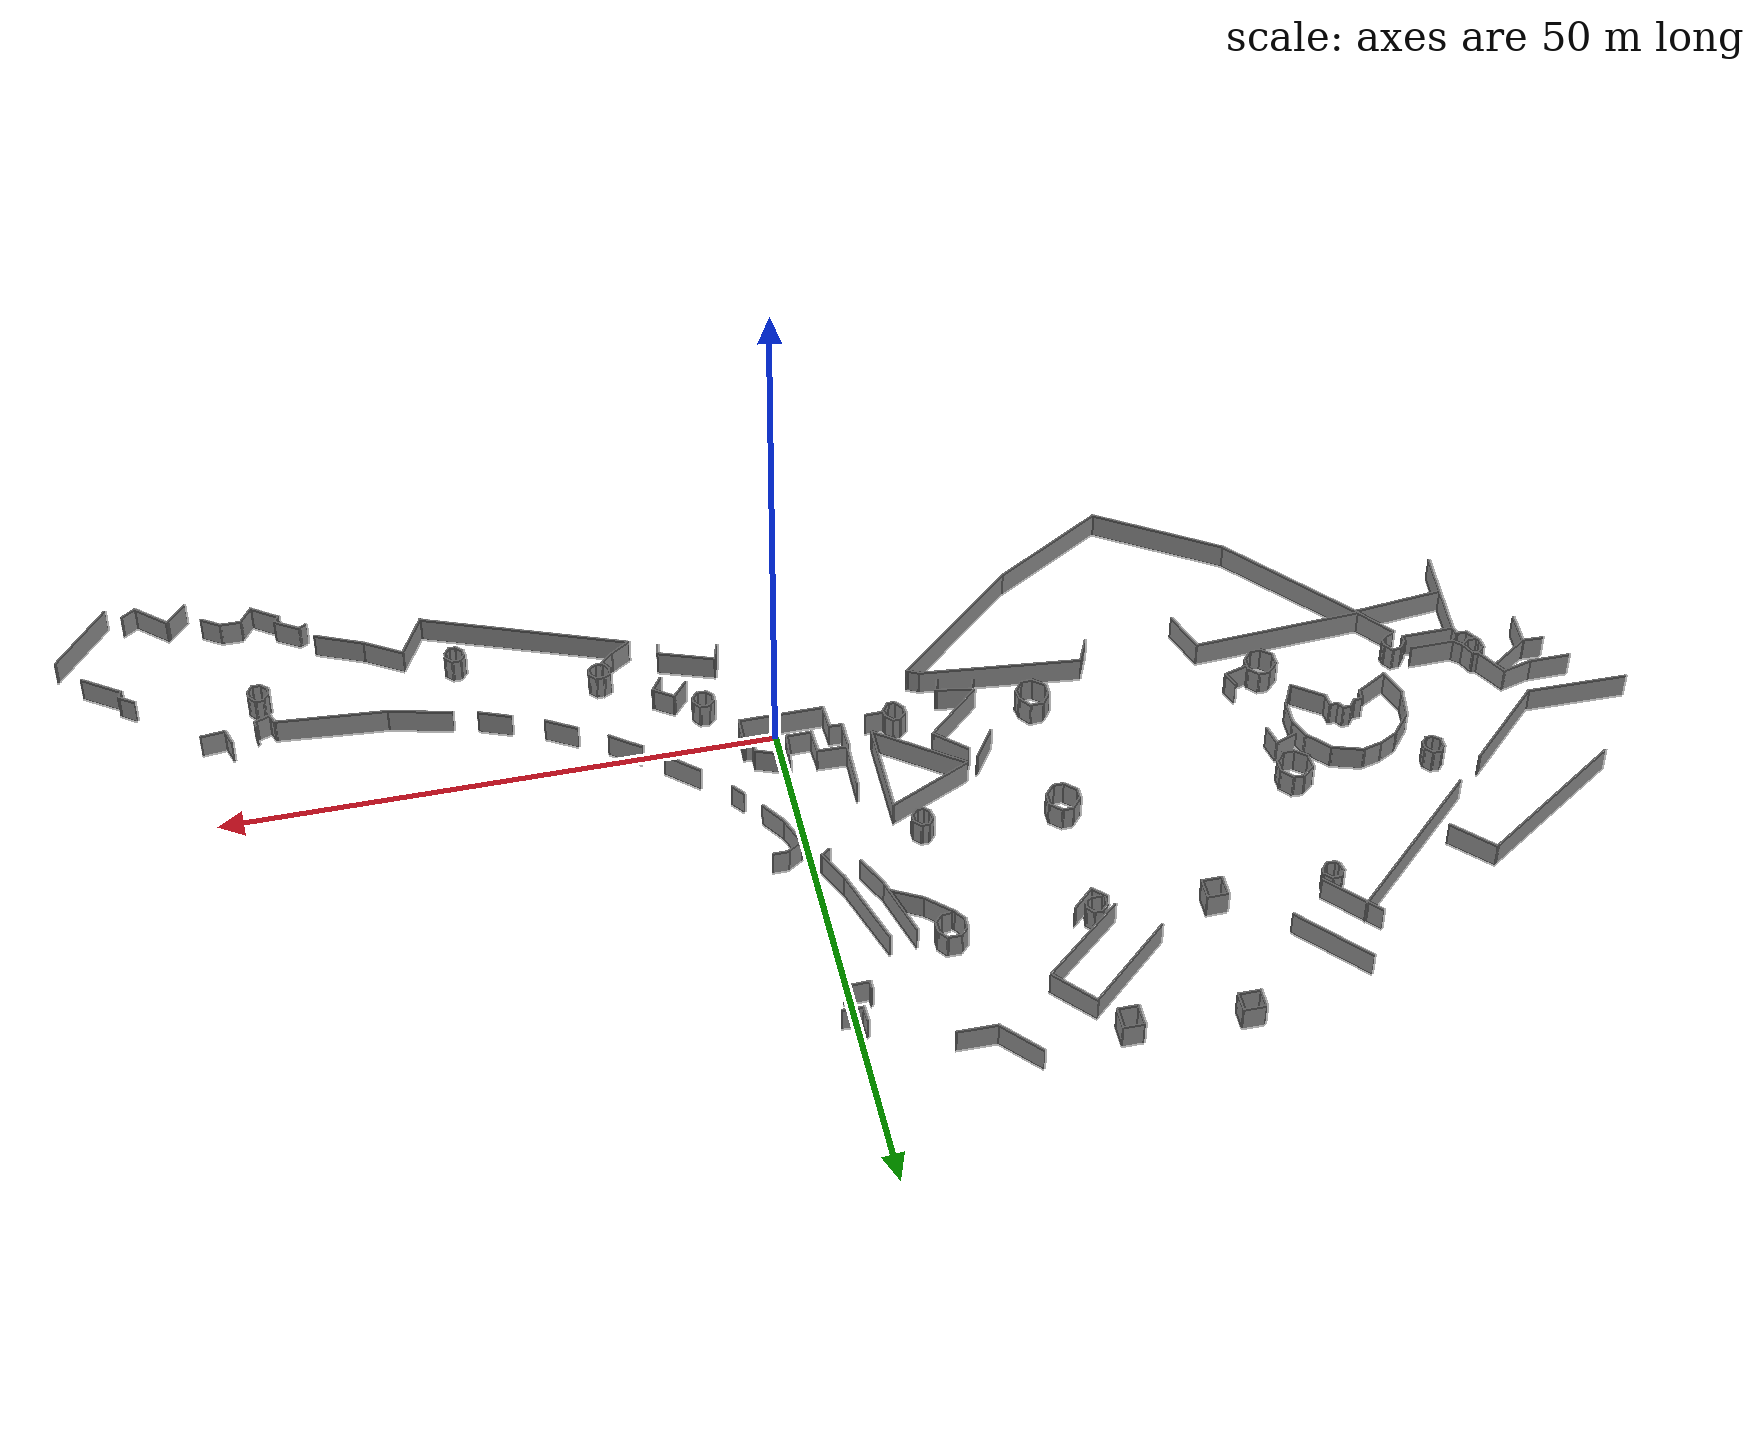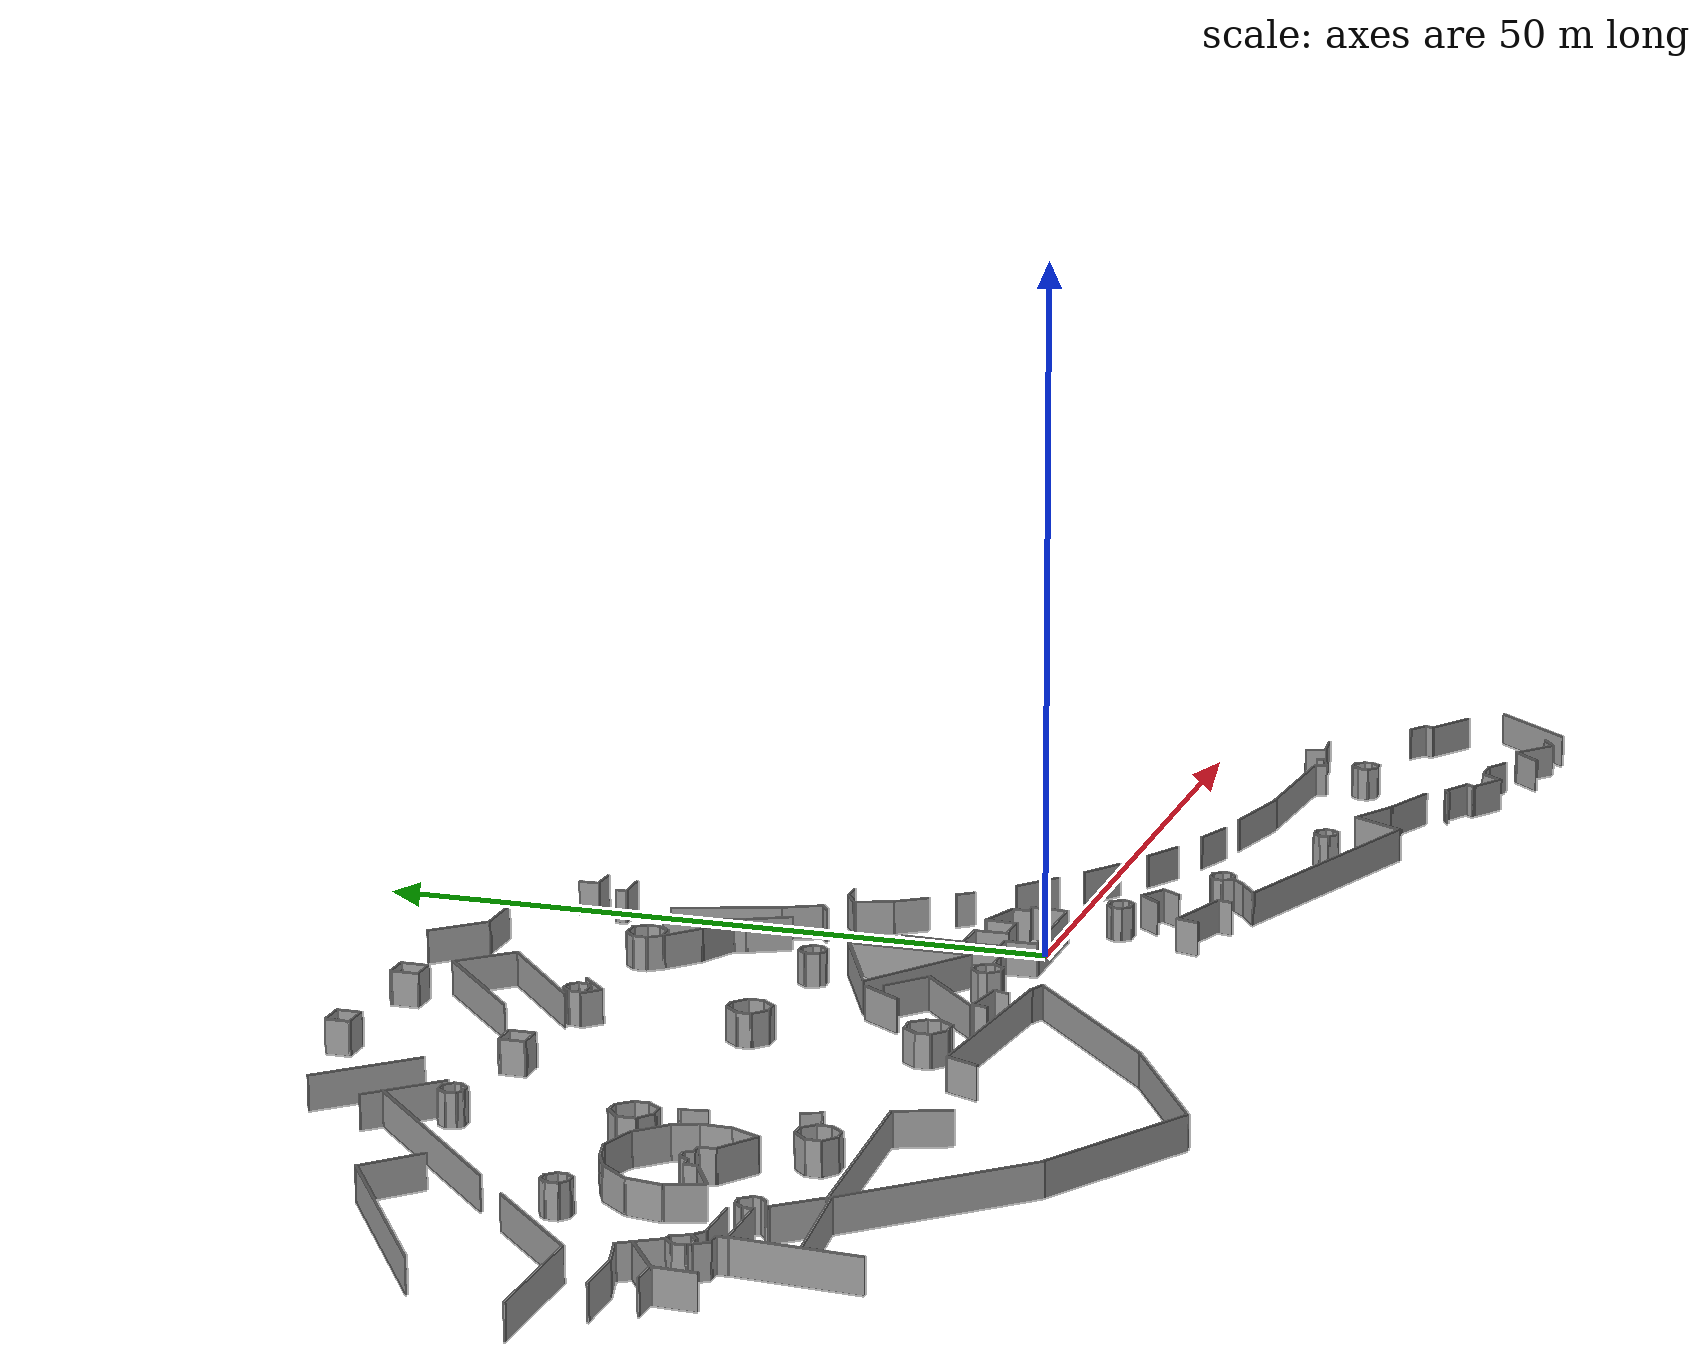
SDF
<?xml version='1.0'?>
<sdf version='1.6'>
  <model name='mall_new_reduce_size'>
    <pose frame=''>-6.80917 7.5529 0 0 -0 0</pose>
    <link name='Wall_0'>
      <collision name='Wall_0_Collision'>
        <geometry>
          <box>
            <size>9.25048 0.15 2.5</size>
          </box>
        </geometry>
        <pose frame=''>0 0 1.25 0 -0 0</pose>
      </collision>
      <visual name='Wall_0_Visual'>
        <pose frame=''>0 0 1.25 0 -0 0</pose>
        <geometry>
          <box>
            <size>9.25048 0.15 2.5</size>
          </box>
        </geometry>
        <material>
          <script>
            <uri>file://media/materials/scripts/gazebo.material</uri>
            <name>Gazebo/Grey</name>
          </script>
          <ambient>1 1 1 1</ambient>
        </material>
        <meta>
          <layer>0</layer>
        </meta>
      </visual>
      <pose frame=''>-64.3372 3.2996 0 0 -0 -0.010225</pose>
    </link>
    <link name='Wall_10'>
      <collision name='Wall_10_Collision'>
        <geometry>
          <box>
            <size>15.64 0.15 2.5</size>
          </box>
        </geometry>
        <pose frame=''>0 0 1.25 0 -0 0</pose>
      </collision>
      <visual name='Wall_10_Visual'>
        <pose frame=''>0 0 1.25 0 -0 0</pose>
        <geometry>
          <box>
            <size>15.64 0.15 2.5</size>
          </box>
        </geometry>
        <material>
          <script>
            <uri>file://media/materials/scripts/gazebo.material</uri>
            <name>Gazebo/Grey</name>
          </script>
          <ambient>1 1 1 1</ambient>
        </material>
        <meta>
          <layer>0</layer>
        </meta>
      </visual>
      <pose frame=''>-57.6357 15.9234 0 0 -0 0.595213</pose>
    </link>
    <link name='Wall_102'>
      <collision name='Wall_102_Collision'>
        <geometry>
          <box>
            <size>0.911014 0.15 2.5</size>
          </box>
        </geometry>
        <pose frame=''>0 0 1.25 0 -0 0</pose>
      </collision>
      <visual name='Wall_102_Visual'>
        <pose frame=''>0 0 1.25 0 -0 0</pose>
        <geometry>
          <box>
            <size>0.911014 0.15 2.5</size>
          </box>
        </geometry>
        <material>
          <script>
            <uri>file://media/materials/scripts/gazebo.material</uri>
            <name>Gazebo/Grey</name>
          </script>
          <ambient>1 1 1 1</ambient>
        </material>
        <meta>
          <layer>0</layer>
        </meta>
      </visual>
      <pose frame=''>5.13908 23.8484 0 0 -0 -1.5708</pose>
    </link>
    <link name='Wall_103'>
      <collision name='Wall_103_Collision'>
        <geometry>
          <box>
            <size>2.3915 0.15 2.5</size>
          </box>
        </geometry>
        <pose frame=''>0 0 1.25 0 -0 0</pose>
      </collision>
      <visual name='Wall_103_Visual'>
        <pose frame=''>0 0 1.25 0 -0 0</pose>
        <geometry>
          <box>
            <size>2.3915 0.15 2.5</size>
          </box>
        </geometry>
        <material>
          <script>
            <uri>file://media/materials/scripts/gazebo.material</uri>
            <name>Gazebo/Grey</name>
          </script>
          <ambient>1 1 1 1</ambient>
        </material>
        <meta>
          <layer>0</layer>
        </meta>
      </visual>
      <pose frame=''>6.25953 23.4864 0 0 -0 0.02316</pose>
    </link>
    <link name='Wall_106'>
      <collision name='Wall_106_Collision'>
        <geometry>
          <box>
            <size>0.88293 0.15 2.5</size>
          </box>
        </geometry>
        <pose frame=''>0 0 1.25 0 -0 0</pose>
      </collision>
      <visual name='Wall_106_Visual'>
        <pose frame=''>0 0 1.25 0 -0 0</pose>
        <geometry>
          <box>
            <size>0.88293 0.15 2.5</size>
          </box>
        </geometry>
        <material>
          <script>
            <uri>file://media/materials/scripts/gazebo.material</uri>
            <name>Gazebo/Grey</name>
          </script>
          <ambient>1 1 1 1</ambient>
        </material>
        <meta>
          <layer>0</layer>
        </meta>
      </visual>
      <pose frame=''>-37.2247 20.3731 0 0 -0 1.00343</pose>
    </link>
    <link name='Wall_107'>
      <collision name='Wall_107_Collision'>
        <geometry>
          <box>
            <size>0.940533 0.15 2.5</size>
          </box>
        </geometry>
        <pose frame=''>0 0 1.25 0 -0 0</pose>
      </collision>
      <visual name='Wall_107_Visual'>
        <pose frame=''>0 0 1.25 0 -0 0</pose>
        <geometry>
          <box>
            <size>0.940533 0.15 2.5</size>
          </box>
        </geometry>
        <material>
          <script>
            <uri>file://media/materials/scripts/gazebo.material</uri>
            <name>Gazebo/Grey</name>
          </script>
          <ambient>1 1 1 1</ambient>
        </material>
        <meta>
          <layer>0</layer>
        </meta>
      </visual>
      <pose frame=''>-36.633 20.7072 0 0 -0 0.04939</pose>
    </link>
    <link name='Wall_108'>
      <collision name='Wall_108_Collision'>
        <geometry>
          <box>
            <size>1.04338 0.15 2.5</size>
          </box>
        </geometry>
        <pose frame=''>0 0 1.25 0 -0 0</pose>
      </collision>
      <visual name='Wall_108_Visual'>
        <pose frame=''>0 0 1.25 0 -0 0</pose>
        <geometry>
          <box>
            <size>1.04338 0.15 2.5</size>
          </box>
        </geometry>
        <material>
          <script>
            <uri>file://media/materials/scripts/gazebo.material</uri>
            <name>Gazebo/Grey</name>
          </script>
          <ambient>1 1 1 1</ambient>
        </material>
        <meta>
          <layer>0</layer>
        </meta>
      </visual>
      <pose frame=''>-35.9265 20.4122 0 0 -0 -0.780985</pose>
    </link>
    <link name='Wall_109'>
      <collision name='Wall_109_Collision'>
        <geometry>
          <box>
            <size>0.676427 0.15 2.5</size>
          </box>
        </geometry>
        <pose frame=''>0 0 1.25 0 -0 0</pose>
      </collision>
      <visual name='Wall_109_Visual'>
        <pose frame=''>0 0 1.25 0 -0 0</pose>
        <geometry>
          <box>
            <size>0.676427 0.15 2.5</size>
          </box>
        </geometry>
        <material>
          <script>
            <uri>file://media/materials/scripts/gazebo.material</uri>
            <name>Gazebo/Grey</name>
          </script>
          <ambient>1 1 1 1</ambient>
        </material>
        <meta>
          <layer>0</layer>
        </meta>
      </visual>
      <pose frame=''>-35.6455 19.8364 0 0 -0 -1.68757</pose>
    </link>
    <link name='Wall_11'>
      <collision name='Wall_11_Collision'>
        <geometry>
          <box>
            <size>4.74566 0.15 2.5</size>
          </box>
        </geometry>
        <pose frame=''>0 0 1.25 0 -0 0</pose>
      </collision>
      <visual name='Wall_11_Visual'>
        <pose frame=''>0 0 1.25 0 -0 0</pose>
        <geometry>
          <box>
            <size>4.74566 0.15 2.5</size>
          </box>
        </geometry>
        <material>
          <script>
            <uri>file://media/materials/scripts/gazebo.material</uri>
            <name>Gazebo/Grey</name>
          </script>
          <ambient>1 1 1 1</ambient>
        </material>
        <meta>
          <layer>0</layer>
        </meta>
      </visual>
      <pose frame=''>-49.5878 18.6511 0 0 -0 -0.779209</pose>
    </link>
    <link name='Wall_110'>
      <collision name='Wall_110_Collision'>
        <geometry>
          <box>
            <size>0.945582 0.15 2.5</size>
          </box>
        </geometry>
        <pose frame=''>0 0 1.25 0 -0 0</pose>
      </collision>
      <visual name='Wall_110_Visual'>
        <pose frame=''>0 0 1.25 0 -0 0</pose>
        <geometry>
          <box>
            <size>0.945582 0.15 2.5</size>
          </box>
        </geometry>
        <material>
          <script>
            <uri>file://media/materials/scripts/gazebo.material</uri>
            <name>Gazebo/Grey</name>
          </script>
          <ambient>1 1 1 1</ambient>
        </material>
        <meta>
          <layer>0</layer>
        </meta>
      </visual>
      <pose frame=''>-35.9305 19.2738 0 0 -0 -2.28278</pose>
    </link>
    <link name='Wall_111'>
      <collision name='Wall_111_Collision'>
        <geometry>
          <box>
            <size>0.906136 0.15 2.5</size>
          </box>
        </geometry>
        <pose frame=''>0 0 1.25 0 -0 0</pose>
      </collision>
      <visual name='Wall_111_Visual'>
        <pose frame=''>0 0 1.25 0 -0 0</pose>
        <geometry>
          <box>
            <size>0.906136 0.15 2.5</size>
          </box>
        </geometry>
        <material>
          <script>
            <uri>file://media/materials/scripts/gazebo.material</uri>
            <name>Gazebo/Grey</name>
          </script>
          <ambient>1 1 1 1</ambient>
        </material>
        <meta>
          <layer>0</layer>
        </meta>
      </visual>
      <pose frame=''>-36.5684 18.981 0 0 -0 3.13422</pose>
    </link>
    <link name='Wall_112'>
      <collision name='Wall_112_Collision'>
        <geometry>
          <box>
            <size>0.599997 0.15 2.5</size>
          </box>
        </geometry>
        <pose frame=''>0 0 1.25 0 -0 0</pose>
      </collision>
      <visual name='Wall_112_Visual'>
        <pose frame=''>0 0 1.25 0 -0 0</pose>
        <geometry>
          <box>
            <size>0.599997 0.15 2.5</size>
          </box>
        </geometry>
        <material>
          <script>
            <uri>file://media/materials/scripts/gazebo.material</uri>
            <name>Gazebo/Grey</name>
          </script>
          <ambient>1 1 1 1</ambient>
        </material>
        <meta>
          <layer>0</layer>
        </meta>
      </visual>
      <pose frame=''>-37.1032 19.1505 0 0 -0 2.30701</pose>
    </link>
    <link name='Wall_116'>
      <collision name='Wall_116_Collision'>
        <geometry>
          <box>
            <size>0.795039 0.15 2.5</size>
          </box>
        </geometry>
        <pose frame=''>0 0 1.25 0 -0 0</pose>
      </collision>
      <visual name='Wall_116_Visual'>
        <pose frame=''>0 0 1.25 0 -0 0</pose>
        <geometry>
          <box>
            <size>0.795039 0.15 2.5</size>
          </box>
        </geometry>
        <material>
          <script>
            <uri>file://media/materials/scripts/gazebo.material</uri>
            <name>Gazebo/Grey</name>
          </script>
          <ambient>1 1 1 1</ambient>
        </material>
        <meta>
          <layer>0</layer>
        </meta>
      </visual>
      <pose frame=''>-37.3234 19.6378 0 0 -0 1.78689</pose>
    </link>
    <link name='Wall_120'>
      <collision name='Wall_120_Collision'>
        <geometry>
          <box>
            <size>2 0.15 2.5</size>
          </box>
        </geometry>
        <pose frame=''>0 0 1.25 0 -0 0</pose>
      </collision>
      <visual name='Wall_120_Visual'>
        <pose frame=''>0 0 1.25 0 -0 0</pose>
        <geometry>
          <box>
            <size>2 0.15 2.5</size>
          </box>
        </geometry>
        <material>
          <script>
            <uri>file://media/materials/scripts/gazebo.material</uri>
            <name>Gazebo/Grey</name>
          </script>
          <ambient>1 1 1 1</ambient>
        </material>
        <meta>
          <layer>0</layer>
        </meta>
      </visual>
      <pose frame=''>-26.9558 19.541 0 0 -0 -1.5708</pose>
    </link>
    <link name='Wall_121'>
      <collision name='Wall_121_Collision'>
        <geometry>
          <box>
            <size>1.9668 0.15 2.5</size>
          </box>
        </geometry>
        <pose frame=''>0 0 1.25 0 -0 0</pose>
      </collision>
      <visual name='Wall_121_Visual'>
        <pose frame=''>0 0 1.25 0 -0 0</pose>
        <geometry>
          <box>
            <size>1.9668 0.15 2.5</size>
          </box>
        </geometry>
        <material>
          <script>
            <uri>file://media/materials/scripts/gazebo.material</uri>
            <name>Gazebo/Grey</name>
          </script>
          <ambient>1 1 1 1</ambient>
        </material>
        <meta>
          <layer>0</layer>
        </meta>
      </visual>
      <pose frame=''>-26.0474 18.619 0 0 -0 0.003382</pose>
    </link>
    <link name='Wall_122'>
      <collision name='Wall_122_Collision'>
        <geometry>
          <box>
            <size>2.02653 0.15 2.5</size>
          </box>
        </geometry>
        <pose frame=''>0 0 1.25 0 -0 0</pose>
      </collision>
      <visual name='Wall_122_Visual'>
        <pose frame=''>0 0 1.25 0 -0 0</pose>
        <geometry>
          <box>
            <size>2.02653 0.15 2.5</size>
          </box>
        </geometry>
        <material>
          <script>
            <uri>file://media/materials/scripts/gazebo.material</uri>
            <name>Gazebo/Grey</name>
          </script>
          <ambient>1 1 1 1</ambient>
        </material>
        <meta>
          <layer>0</layer>
        </meta>
      </visual>
      <pose frame=''>-25.1383 19.554 0 0 -0 1.57003</pose>
    </link>
    <link name='Wall_123'>
      <collision name='Wall_123_Collision'>
        <geometry>
          <box>
            <size>1.99983 0.15 2.5</size>
          </box>
        </geometry>
        <pose frame=''>0 0 1.25 0 -0 0</pose>
      </collision>
      <visual name='Wall_123_Visual'>
        <pose frame=''>0 0 1.25 0 -0 0</pose>
        <geometry>
          <box>
            <size>1.99983 0.15 2.5</size>
          </box>
        </geometry>
        <material>
          <script>
            <uri>file://media/materials/scripts/gazebo.material</uri>
            <name>Gazebo/Grey</name>
          </script>
          <ambient>1 1 1 1</ambient>
        </material>
        <meta>
          <layer>0</layer>
        </meta>
      </visual>
      <pose frame=''>-26.056 20.4954 0 0 -0 -3.12426</pose>
    </link>
    <link name='Wall_126'>
      <collision name='Wall_126_Collision'>
        <geometry>
          <box>
            <size>1.5 0.15 2.5</size>
          </box>
        </geometry>
        <pose frame=''>0 0 1.25 0 -0 0</pose>
      </collision>
      <visual name='Wall_126_Visual'>
        <pose frame=''>0 0 1.25 0 -0 0</pose>
        <geometry>
          <box>
            <size>1.5 0.15 2.5</size>
          </box>
        </geometry>
        <material>
          <script>
            <uri>file://media/materials/scripts/gazebo.material</uri>
            <name>Gazebo/Grey</name>
          </script>
          <ambient>1 1 1 1</ambient>
        </material>
        <meta>
          <layer>0</layer>
        </meta>
      </visual>
      <pose frame=''>9.56035 7.86068 0 0 -0 3.14159</pose>
    </link>
    <link name='Wall_127'>
      <collision name='Wall_127_Collision'>
        <geometry>
          <box>
            <size>1.79669 0.15 2.5</size>
          </box>
        </geometry>
        <pose frame=''>0 0 1.25 0 -0 0</pose>
      </collision>
      <visual name='Wall_127_Visual'>
        <pose frame=''>0 0 1.25 0 -0 0</pose>
        <geometry>
          <box>
            <size>1.79669 0.15 2.5</size>
          </box>
        </geometry>
        <material>
          <script>
            <uri>file://media/materials/scripts/gazebo.material</uri>
            <name>Gazebo/Grey</name>
          </script>
          <ambient>1 1 1 1</ambient>
        </material>
        <meta>
          <layer>0</layer>
        </meta>
      </visual>
      <pose frame=''>8.19253 7.41582 0 0 -0 -2.57079</pose>
    </link>
    <link name='Wall_128'>
      <collision name='Wall_128_Collision'>
        <geometry>
          <box>
            <size>3.04987 0.15 2.5</size>
          </box>
        </geometry>
        <pose frame=''>0 0 1.25 0 -0 0</pose>
      </collision>
      <visual name='Wall_128_Visual'>
        <pose frame=''>0 0 1.25 0 -0 0</pose>
        <geometry>
          <box>
            <size>3.04987 0.15 2.5</size>
          </box>
        </geometry>
        <material>
          <script>
            <uri>file://media/materials/scripts/gazebo.material</uri>
            <name>Gazebo/Grey</name>
          </script>
          <ambient>1 1 1 1</ambient>
        </material>
        <meta>
          <layer>0</layer>
        </meta>
      </visual>
      <pose frame=''>8.01735 5.63901 0 0 -0 -1.20574</pose>
    </link>
    <link name='Wall_129'>
      <collision name='Wall_129_Collision'>
        <geometry>
          <box>
            <size>2.67124 0.15 2.5</size>
          </box>
        </geometry>
        <pose frame=''>0 0 1.25 0 -0 0</pose>
      </collision>
      <visual name='Wall_129_Visual'>
        <pose frame=''>0 0 1.25 0 -0 0</pose>
        <geometry>
          <box>
            <size>2.67124 0.15 2.5</size>
          </box>
        </geometry>
        <material>
          <script>
            <uri>file://media/materials/scripts/gazebo.material</uri>
            <name>Gazebo/Grey</name>
          </script>
          <ambient>1 1 1 1</ambient>
        </material>
        <meta>
          <layer>0</layer>
        </meta>
      </visual>
      <pose frame=''>9.25128 3.23607 0 0 -0 -0.966457</pose>
    </link>
    <link name='Wall_134'>
      <collision name='Wall_134_Collision'>
        <geometry>
          <box>
            <size>1.4429 0.15 2.5</size>
          </box>
        </geometry>
        <pose frame=''>0 0 1.25 0 -0 0</pose>
      </collision>
      <visual name='Wall_134_Visual'>
        <pose frame=''>0 0 1.25 0 -0 0</pose>
        <geometry>
          <box>
            <size>1.4429 0.15 2.5</size>
          </box>
        </geometry>
        <material>
          <script>
            <uri>file://media/materials/scripts/gazebo.material</uri>
            <name>Gazebo/Grey</name>
          </script>
          <ambient>1 1 1 1</ambient>
        </material>
        <meta>
          <layer>0</layer>
        </meta>
      </visual>
      <pose frame=''>11.7178 -0.065856 0 0 -0 -0.919284</pose>
    </link>
    <link name='Wall_137'>
      <collision name='Wall_137_Collision'>
        <geometry>
          <box>
            <size>3.68143 0.15 2.5</size>
          </box>
        </geometry>
        <pose frame=''>0 0 1.25 0 -0 0</pose>
      </collision>
      <visual name='Wall_137_Visual'>
        <pose frame=''>0 0 1.25 0 -0 0</pose>
        <geometry>
          <box>
            <size>3.68143 0.15 2.5</size>
          </box>
        </geometry>
        <material>
          <script>
            <uri>file://media/materials/scripts/gazebo.material</uri>
            <name>Gazebo/Grey</name>
          </script>
          <ambient>1 1 1 1</ambient>
        </material>
        <meta>
          <layer>0</layer>
        </meta>
      </visual>
      <pose frame=''>15.8732 -4.24673 0 0 -0 -0.713439</pose>
    </link>
    <link name='Wall_140'>
      <collision name='Wall_140_Collision'>
        <geometry>
          <box>
            <size>3.35827 0.15 2.5</size>
          </box>
        </geometry>
        <pose frame=''>0 0 1.25 0 -0 0</pose>
      </collision>
      <visual name='Wall_140_Visual'>
        <pose frame=''>0 0 1.25 0 -0 0</pose>
        <geometry>
          <box>
            <size>3.35827 0.15 2.5</size>
          </box>
        </geometry>
        <material>
          <script>
            <uri>file://media/materials/scripts/gazebo.material</uri>
            <name>Gazebo/Grey</name>
          </script>
          <ambient>1 1 1 1</ambient>
        </material>
        <meta>
          <layer>0</layer>
        </meta>
      </visual>
      <pose frame=''>20.3327 -7.86303 0 0 -0 -0.619292</pose>
    </link>
    <link name='Wall_143'>
      <collision name='Wall_143_Collision'>
        <geometry>
          <box>
            <size>3.17972 0.15 2.5</size>
          </box>
        </geometry>
        <pose frame=''>0 0 1.25 0 -0 0</pose>
      </collision>
      <visual name='Wall_143_Visual'>
        <pose frame=''>0 0 1.25 0 -0 0</pose>
        <geometry>
          <box>
            <size>3.17972 0.15 2.5</size>
          </box>
        </geometry>
        <material>
          <script>
            <uri>file://media/materials/scripts/gazebo.material</uri>
            <name>Gazebo/Grey</name>
          </script>
          <ambient>1 1 1 1</ambient>
        </material>
        <meta>
          <layer>0</layer>
        </meta>
      </visual>
      <pose frame=''>25.5439 -11.078 0 0 -0 -0.516247</pose>
    </link>
    <link name='Wall_146'>
      <collision name='Wall_146_Collision'>
        <geometry>
          <box>
            <size>3.13185 0.15 2.5</size>
          </box>
        </geometry>
        <pose frame=''>0 0 1.25 0 -0 0</pose>
      </collision>
      <visual name='Wall_146_Visual'>
        <pose frame=''>0 0 1.25 0 -0 0</pose>
        <geometry>
          <box>
            <size>3.13185 0.15 2.5</size>
          </box>
        </geometry>
        <material>
          <script>
            <uri>file://media/materials/scripts/gazebo.material</uri>
            <name>Gazebo/Grey</name>
          </script>
          <ambient>1 1 1 1</ambient>
        </material>
        <meta>
          <layer>0</layer>
        </meta>
      </visual>
      <pose frame=''>31.1319 -13.5209 0 0 -0 -0.367866</pose>
    </link>
    <link name='Wall_149'>
      <collision name='Wall_149_Collision'>
        <geometry>
          <box>
            <size>6.0228 0.15 2.5</size>
          </box>
        </geometry>
        <pose frame=''>0 0 1.25 0 -0 0</pose>
      </collision>
      <visual name='Wall_149_Visual'>
        <pose frame=''>0 0 1.25 0 -0 0</pose>
        <geometry>
          <box>
            <size>6.0228 0.15 2.5</size>
          </box>
        </geometry>
        <material>
          <script>
            <uri>file://media/materials/scripts/gazebo.material</uri>
            <name>Gazebo/Grey</name>
          </script>
          <ambient>1 1 1 1</ambient>
        </material>
        <meta>
          <layer>0</layer>
        </meta>
      </visual>
      <pose frame=''>37.6627 -15.2721 0 0 -0 -0.24371</pose>
    </link>
    <link name='Wall_15'>
      <collision name='Wall_15_Collision'>
        <geometry>
          <box>
            <size>17.0313 0.15 2.5</size>
          </box>
        </geometry>
        <pose frame=''>0 0 1.25 0 -0 0</pose>
      </collision>
      <visual name='Wall_15_Visual'>
        <pose frame=''>0 0 1.25 0 -0 0</pose>
        <geometry>
          <box>
            <size>17.0313 0.15 2.5</size>
          </box>
        </geometry>
        <material>
          <script>
            <uri>file://media/materials/scripts/gazebo.material</uri>
            <name>Gazebo/Grey</name>
          </script>
          <ambient>1 1 1 1</ambient>
        </material>
        <meta>
          <layer>0</layer>
        </meta>
      </visual>
      <pose frame=''>-44.3443 18.1837 0 0 -0 0.766862</pose>
    </link>
    <link name='Wall_150'>
      <collision name='Wall_150_Collision'>
        <geometry>
          <box>
            <size>10.0902 0.15 2.5</size>
          </box>
        </geometry>
        <pose frame=''>0 0 1.25 0 -0 0</pose>
      </collision>
      <visual name='Wall_150_Visual'>
        <pose frame=''>0 0 1.25 0 -0 0</pose>
        <geometry>
          <box>
            <size>10.0902 0.15 2.5</size>
          </box>
        </geometry>
        <material>
          <script>
            <uri>file://media/materials/scripts/gazebo.material</uri>
            <name>Gazebo/Grey</name>
          </script>
          <ambient>1 1 1 1</ambient>
        </material>
        <meta>
          <layer>0</layer>
        </meta>
      </visual>
      <pose frame=''>45.4742 -16.3538 0 0 -0 -0.081987</pose>
    </link>
    <link name='Wall_151'>
      <collision name='Wall_151_Collision'>
        <geometry>
          <box>
            <size>1.07037 0.15 2.5</size>
          </box>
        </geometry>
        <pose frame=''>0 0 1.25 0 -0 0</pose>
      </collision>
      <visual name='Wall_151_Visual'>
        <pose frame=''>0 0 1.25 0 -0 0</pose>
        <geometry>
          <box>
            <size>1.07037 0.15 2.5</size>
          </box>
        </geometry>
        <material>
          <script>
            <uri>file://media/materials/scripts/gazebo.material</uri>
            <name>Gazebo/Grey</name>
          </script>
          <ambient>1 1 1 1</ambient>
        </material>
        <meta>
          <layer>0</layer>
        </meta>
      </visual>
      <pose frame=''>50.5839 -17.1905 0 0 -0 -1.20463</pose>
    </link>
    <link name='Wall_152'>
      <collision name='Wall_152_Collision'>
        <geometry>
          <box>
            <size>1.64204 0.15 2.5</size>
          </box>
        </geometry>
        <pose frame=''>0 0 1.25 0 -0 0</pose>
      </collision>
      <visual name='Wall_152_Visual'>
        <pose frame=''>0 0 1.25 0 -0 0</pose>
        <geometry>
          <box>
            <size>1.64204 0.15 2.5</size>
          </box>
        </geometry>
        <material>
          <script>
            <uri>file://media/materials/scripts/gazebo.material</uri>
            <name>Gazebo/Grey</name>
          </script>
          <ambient>1 1 1 1</ambient>
        </material>
        <meta>
          <layer>0</layer>
        </meta>
      </visual>
      <pose frame=''>51.4454 -17.3621 0 0 -0 0.365329</pose>
    </link>
    <link name='Wall_153'>
      <collision name='Wall_153_Collision'>
        <geometry>
          <box>
            <size>0.719382 0.15 2.5</size>
          </box>
        </geometry>
        <pose frame=''>0 0 1.25 0 -0 0</pose>
      </collision>
      <visual name='Wall_153_Visual'>
        <pose frame=''>0 0 1.25 0 -0 0</pose>
        <geometry>
          <box>
            <size>0.719382 0.15 2.5</size>
          </box>
        </geometry>
        <material>
          <script>
            <uri>file://media/materials/scripts/gazebo.material</uri>
            <name>Gazebo/Grey</name>
          </script>
          <ambient>1 1 1 1</ambient>
        </material>
        <meta>
          <layer>0</layer>
        </meta>
      </visual>
      <pose frame=''>52.104 -16.8147 0 0 -0 1.73536</pose>
    </link>
    <link name='Wall_156'>
      <collision name='Wall_156_Collision'>
        <geometry>
          <box>
            <size>1.66975 0.15 2.5</size>
          </box>
        </geometry>
        <pose frame=''>0 0 1.25 0 -0 0</pose>
      </collision>
      <visual name='Wall_156_Visual'>
        <pose frame=''>0 0 1.25 0 -0 0</pose>
        <geometry>
          <box>
            <size>1.66975 0.15 2.5</size>
          </box>
        </geometry>
        <material>
          <script>
            <uri>file://media/materials/scripts/gazebo.material</uri>
            <name>Gazebo/Grey</name>
          </script>
          <ambient>1 1 1 1</ambient>
        </material>
        <meta>
          <layer>0</layer>
        </meta>
      </visual>
      <pose frame=''>54.6252 -15.8323 0 0 -0 -1.27154</pose>
    </link>
    <link name='Wall_157'>
      <collision name='Wall_157_Collision'>
        <geometry>
          <box>
            <size>2.34099 0.15 2.5</size>
          </box>
        </geometry>
        <pose frame=''>0 0 1.25 0 -0 0</pose>
      </collision>
      <visual name='Wall_157_Visual'>
        <pose frame=''>0 0 1.25 0 -0 0</pose>
        <geometry>
          <box>
            <size>2.34099 0.15 2.5</size>
          </box>
        </geometry>
        <material>
          <script>
            <uri>file://media/materials/scripts/gazebo.material</uri>
            <name>Gazebo/Grey</name>
          </script>
          <ambient>1 1 1 1</ambient>
        </material>
        <meta>
          <layer>0</layer>
        </meta>
      </visual>
      <pose frame=''>55.9396 -16.4609 0 0 -0 0.096908</pose>
    </link>
    <link name='Wall_160'>
      <collision name='Wall_160_Collision'>
        <geometry>
          <box>
            <size>0.922115 0.15 2.5</size>
          </box>
        </geometry>
        <pose frame=''>0 0 1.25 0 -0 0</pose>
      </collision>
      <visual name='Wall_160_Visual'>
        <pose frame=''>0 0 1.25 0 -0 0</pose>
        <geometry>
          <box>
            <size>0.922115 0.15 2.5</size>
          </box>
        </geometry>
        <material>
          <script>
            <uri>file://media/materials/scripts/gazebo.material</uri>
            <name>Gazebo/Grey</name>
          </script>
          <ambient>1 1 1 1</ambient>
        </material>
        <meta>
          <layer>0</layer>
        </meta>
      </visual>
      <pose frame=''>50.8361 -19.9069 0 0 -0 0.843659</pose>
    </link>
    <link name='Wall_161'>
      <collision name='Wall_161_Collision'>
        <geometry>
          <box>
            <size>0.855974 0.15 2.5</size>
          </box>
        </geometry>
        <pose frame=''>0 0 1.25 0 -0 0</pose>
      </collision>
      <visual name='Wall_161_Visual'>
        <pose frame=''>0 0 1.25 0 -0 0</pose>
        <geometry>
          <box>
            <size>0.855974 0.15 2.5</size>
          </box>
        </geometry>
        <material>
          <script>
            <uri>file://media/materials/scripts/gazebo.material</uri>
            <name>Gazebo/Grey</name>
          </script>
          <ambient>1 1 1 1</ambient>
        </material>
        <meta>
          <layer>0</layer>
        </meta>
      </visual>
      <pose frame=''>51.4457 -19.6069 0 0 -0 0.008949</pose>
    </link>
    <link name='Wall_162'>
      <collision name='Wall_162_Collision'>
        <geometry>
          <box>
            <size>1.02706 0.15 2.5</size>
          </box>
        </geometry>
        <pose frame=''>0 0 1.25 0 -0 0</pose>
      </collision>
      <visual name='Wall_162_Visual'>
        <pose frame=''>0 0 1.25 0 -0 0</pose>
        <geometry>
          <box>
            <size>1.02706 0.15 2.5</size>
          </box>
        </geometry>
        <material>
          <script>
            <uri>file://media/materials/scripts/gazebo.material</uri>
            <name>Gazebo/Grey</name>
          </script>
          <ambient>1 1 1 1</ambient>
        </material>
        <meta>
          <layer>0</layer>
        </meta>
      </visual>
      <pose frame=''>52.0627 -19.9472 0 0 -0 -0.900073</pose>
    </link>
    <link name='Wall_163'>
      <collision name='Wall_163_Collision'>
        <geometry>
          <box>
            <size>0.756321 0.15 2.5</size>
          </box>
        </geometry>
        <pose frame=''>0 0 1.25 0 -0 0</pose>
      </collision>
      <visual name='Wall_163_Visual'>
        <pose frame=''>0 0 1.25 0 -0 0</pose>
        <geometry>
          <box>
            <size>0.756321 0.15 2.5</size>
          </box>
        </geometry>
        <material>
          <script>
            <uri>file://media/materials/scripts/gazebo.material</uri>
            <name>Gazebo/Grey</name>
          </script>
          <ambient>1 1 1 1</ambient>
        </material>
        <meta>
          <layer>0</layer>
        </meta>
      </visual>
      <pose frame=''>52.3278 -20.5939 0 0 -0 -1.56745</pose>
    </link>
    <link name='Wall_164'>
      <collision name='Wall_164_Collision'>
        <geometry>
          <box>
            <size>0.854712 0.15 2.5</size>
          </box>
        </geometry>
        <pose frame=''>0 0 1.25 0 -0 0</pose>
      </collision>
      <visual name='Wall_164_Visual'>
        <pose frame=''>0 0 1.25 0 -0 0</pose>
        <geometry>
          <box>
            <size>0.854712 0.15 2.5</size>
          </box>
        </geometry>
        <material>
          <script>
            <uri>file://media/materials/scripts/gazebo.material</uri>
            <name>Gazebo/Grey</name>
          </script>
          <ambient>1 1 1 1</ambient>
        </material>
        <meta>
          <layer>0</layer>
        </meta>
      </visual>
      <pose frame=''>52.1195 -21.1866 0 0 -0 -2.17742</pose>
    </link>
    <link name='Wall_165'>
      <collision name='Wall_165_Collision'>
        <geometry>
          <box>
            <size>0.950864 0.15 2.5</size>
          </box>
        </geometry>
        <pose frame=''>0 0 1.25 0 -0 0</pose>
      </collision>
      <visual name='Wall_165_Visual'>
        <pose frame=''>0 0 1.25 0 -0 0</pose>
        <geometry>
          <box>
            <size>0.950864 0.15 2.5</size>
          </box>
        </geometry>
        <material>
          <script>
            <uri>file://media/materials/scripts/gazebo.material</uri>
            <name>Gazebo/Grey</name>
          </script>
          <ambient>1 1 1 1</ambient>
        </material>
        <meta>
          <layer>0</layer>
        </meta>
      </visual>
      <pose frame=''>51.5271 -21.4943 0 0 -0 -3.09591</pose>
    </link>
    <link name='Wall_166'>
      <collision name='Wall_166_Collision'>
        <geometry>
          <box>
            <size>0.977095 0.15 2.5</size>
          </box>
        </geometry>
        <pose frame=''>0 0 1.25 0 -0 0</pose>
      </collision>
      <visual name='Wall_166_Visual'>
        <pose frame=''>0 0 1.25 0 -0 0</pose>
        <geometry>
          <box>
            <size>0.977095 0.15 2.5</size>
          </box>
        </geometry>
        <material>
          <script>
            <uri>file://media/materials/scripts/gazebo.material</uri>
            <name>Gazebo/Grey</name>
          </script>
          <ambient>1 1 1 1</ambient>
        </material>
        <meta>
          <layer>0</layer>
        </meta>
      </visual>
      <pose frame=''>50.8226 -21.2238 0 0 -0 2.36845</pose>
    </link>
    <link name='Wall_167'>
      <collision name='Wall_167_Collision'>
        <geometry>
          <box>
            <size>0.862803 0.15 2.5</size>
          </box>
        </geometry>
        <pose frame=''>0 0 1.25 0 -0 0</pose>
      </collision>
      <visual name='Wall_167_Visual'>
        <pose frame=''>0 0 1.25 0 -0 0</pose>
        <geometry>
          <box>
            <size>0.862803 0.15 2.5</size>
          </box>
        </geometry>
        <material>
          <script>
            <uri>file://media/materials/scripts/gazebo.material</uri>
            <name>Gazebo/Grey</name>
          </script>
          <ambient>1 1 1 1</ambient>
        </material>
        <meta>
          <layer>0</layer>
        </meta>
      </visual>
      <pose frame=''>50.5217 -20.5788 0 0 -0 1.60849</pose>
    </link>
    <link name='Wall_17'>
      <collision name='Wall_17_Collision'>
        <geometry>
          <box>
            <size>6.11812 0.15 2.5</size>
          </box>
        </geometry>
        <pose frame=''>0 0 1.25 0 -0 0</pose>
      </collision>
      <visual name='Wall_17_Visual'>
        <pose frame=''>0 0 1.25 0 -0 0</pose>
        <geometry>
          <box>
            <size>6.11812 0.15 2.5</size>
          </box>
        </geometry>
        <material>
          <script>
            <uri>file://media/materials/scripts/gazebo.material</uri>
            <name>Gazebo/Grey</name>
          </script>
          <ambient>1 1 1 1</ambient>
        </material>
        <meta>
          <layer>0</layer>
        </meta>
      </visual>
      <pose frame=''>-37.3721 22.8899 0 0 -0 -0.823537</pose>
    </link>
    <link name='Wall_170'>
      <collision name='Wall_170_Collision'>
        <geometry>
          <box>
            <size>1.71198 0.15 2.5</size>
          </box>
        </geometry>
        <pose frame=''>0 0 1.25 0 -0 0</pose>
      </collision>
      <visual name='Wall_170_Visual'>
        <pose frame=''>0 0 1.25 0 -0 0</pose>
        <geometry>
          <box>
            <size>1.71198 0.15 2.5</size>
          </box>
        </geometry>
        <material>
          <script>
            <uri>file://media/materials/scripts/gazebo.material</uri>
            <name>Gazebo/Grey</name>
          </script>
          <ambient>1 1 1 1</ambient>
        </material>
        <meta>
          <layer>0</layer>
        </meta>
      </visual>
      <pose frame=''>63.0306 -22.2425 0 0 -0 -0.612119</pose>
    </link>
    <link name='Wall_171'>
      <collision name='Wall_171_Collision'>
        <geometry>
          <box>
            <size>0.839183 0.15 2.5</size>
          </box>
        </geometry>
        <pose frame=''>0 0 1.25 0 -0 0</pose>
      </collision>
      <visual name='Wall_171_Visual'>
        <pose frame=''>0 0 1.25 0 -0 0</pose>
        <geometry>
          <box>
            <size>0.839183 0.15 2.5</size>
          </box>
        </geometry>
        <material>
          <script>
            <uri>file://media/materials/scripts/gazebo.material</uri>
            <name>Gazebo/Grey</name>
          </script>
          <ambient>1 1 1 1</ambient>
        </material>
        <meta>
          <layer>0</layer>
        </meta>
      </visual>
      <pose frame=''>63.5354 -23.0042 0 0 -0 -2.00233</pose>
    </link>
    <link name='Wall_172'>
      <collision name='Wall_172_Collision'>
        <geometry>
          <box>
            <size>4.15243 0.15 2.5</size>
          </box>
        </geometry>
        <pose frame=''>0 0 1.25 0 -0 0</pose>
      </collision>
      <visual name='Wall_172_Visual'>
        <pose frame=''>0 0 1.25 0 -0 0</pose>
        <geometry>
          <box>
            <size>4.15243 0.15 2.5</size>
          </box>
        </geometry>
        <material>
          <script>
            <uri>file://media/materials/scripts/gazebo.material</uri>
            <name>Gazebo/Grey</name>
          </script>
          <ambient>1 1 1 1</ambient>
        </material>
        <meta>
          <layer>0</layer>
        </meta>
      </visual>
      <pose frame=''>65.0743 -24.4298 0 0 -0 -0.589468</pose>
    </link>
    <link name='Wall_175'>
      <collision name='Wall_175_Collision'>
        <geometry>
          <box>
            <size>7.63134 0.15 2.5</size>
          </box>
        </geometry>
        <pose frame=''>0 0 1.25 0 -0 0</pose>
      </collision>
      <visual name='Wall_175_Visual'>
        <pose frame=''>0 0 1.25 0 -0 0</pose>
        <geometry>
          <box>
            <size>7.63134 0.15 2.5</size>
          </box>
        </geometry>
        <material>
          <script>
            <uri>file://media/materials/scripts/gazebo.material</uri>
            <name>Gazebo/Grey</name>
          </script>
          <ambient>1 1 1 1</ambient>
        </material>
        <meta>
          <layer>0</layer>
        </meta>
      </visual>
      <pose frame=''>66.4001 -30.8567 0 0 -0 -2.28745</pose>
    </link>
    <link name='Wall_178'>
      <collision name='Wall_178_Collision'>
        <geometry>
          <box>
            <size>2.71113 0.15 2.5</size>
          </box>
        </geometry>
        <pose frame=''>0 0 1.25 0 -0 0</pose>
      </collision>
      <visual name='Wall_178_Visual'>
        <pose frame=''>0 0 1.25 0 -0 0</pose>
        <geometry>
          <box>
            <size>2.71113 0.15 2.5</size>
          </box>
        </geometry>
        <material>
          <script>
            <uri>file://media/materials/scripts/gazebo.material</uri>
            <name>Gazebo/Grey</name>
          </script>
          <ambient>1 1 1 1</ambient>
        </material>
        <meta>
          <layer>0</layer>
        </meta>
      </visual>
      <pose frame=''>57.6342 -32.0142 0 0 -0 0.814065</pose>
    </link>
    <link name='Wall_179'>
      <collision name='Wall_179_Collision'>
        <geometry>
          <box>
            <size>3.68959 0.15 2.5</size>
          </box>
        </geometry>
        <pose frame=''>0 0 1.25 0 -0 0</pose>
      </collision>
      <visual name='Wall_179_Visual'>
        <pose frame=''>0 0 1.25 0 -0 0</pose>
        <geometry>
          <box>
            <size>3.68959 0.15 2.5</size>
          </box>
        </geometry>
        <material>
          <script>
            <uri>file://media/materials/scripts/gazebo.material</uri>
            <name>Gazebo/Grey</name>
          </script>
          <ambient>1 1 1 1</ambient>
        </material>
        <meta>
          <layer>0</layer>
        </meta>
      </visual>
      <pose frame=''>59.8368 -32.2413 0 0 -0 -0.713396</pose>
    </link>
    <link name='Wall_180'>
      <collision name='Wall_180_Collision'>
        <geometry>
          <box>
            <size>1.63637 0.15 2.5</size>
          </box>
        </geometry>
        <pose frame=''>0 0 1.25 0 -0 0</pose>
      </collision>
      <visual name='Wall_180_Visual'>
        <pose frame=''>0 0 1.25 0 -0 0</pose>
        <geometry>
          <box>
            <size>1.63637 0.15 2.5</size>
          </box>
        </geometry>
        <material>
          <script>
            <uri>file://media/materials/scripts/gazebo.material</uri>
            <name>Gazebo/Grey</name>
          </script>
          <ambient>1 1 1 1</ambient>
        </material>
        <meta>
          <layer>0</layer>
        </meta>
      </visual>
      <pose frame=''>61.8128 -33.009 0 0 -0 0.576763</pose>
    </link>
    <link name='Wall_183'>
      <collision name='Wall_183_Collision'>
        <geometry>
          <box>
            <size>0.858507 0.15 2.5</size>
          </box>
        </geometry>
        <pose frame=''>0 0 1.25 0 -0 0</pose>
      </collision>
      <visual name='Wall_183_Visual'>
        <pose frame=''>0 0 1.25 0 -0 0</pose>
        <geometry>
          <box>
            <size>0.858507 0.15 2.5</size>
          </box>
        </geometry>
        <material>
          <script>
            <uri>file://media/materials/scripts/gazebo.material</uri>
            <name>Gazebo/Grey</name>
          </script>
          <ambient>1 1 1 1</ambient>
        </material>
        <meta>
          <layer>0</layer>
        </meta>
      </visual>
      <pose frame=''>46.5261 -28.0243 0 0 -0 0.469325</pose>
    </link>
    <link name='Wall_184'>
      <collision name='Wall_184_Collision'>
        <geometry>
          <box>
            <size>2.54291 0.15 2.5</size>
          </box>
        </geometry>
        <pose frame=''>0 0 1.25 0 -0 0</pose>
      </collision>
      <visual name='Wall_184_Visual'>
        <pose frame=''>0 0 1.25 0 -0 0</pose>
        <geometry>
          <box>
            <size>2.54291 0.15 2.5</size>
          </box>
        </geometry>
        <material>
          <script>
            <uri>file://media/materials/scripts/gazebo.material</uri>
            <name>Gazebo/Grey</name>
          </script>
          <ambient>1 1 1 1</ambient>
        </material>
        <meta>
          <layer>0</layer>
        </meta>
      </visual>
      <pose frame=''>47.867 -28.4664 0 0 -0 -0.541971</pose>
    </link>
    <link name='Wall_185'>
      <collision name='Wall_185_Collision'>
        <geometry>
          <box>
            <size>0.862335 0.15 2.5</size>
          </box>
        </geometry>
        <pose frame=''>0 0 1.25 0 -0 0</pose>
      </collision>
      <visual name='Wall_185_Visual'>
        <pose frame=''>0 0 1.25 0 -0 0</pose>
        <geometry>
          <box>
            <size>0.862335 0.15 2.5</size>
          </box>
        </geometry>
        <material>
          <script>
            <uri>file://media/materials/scripts/gazebo.material</uri>
            <name>Gazebo/Grey</name>
          </script>
          <ambient>1 1 1 1</ambient>
        </material>
        <meta>
          <layer>0</layer>
        </meta>
      </visual>
      <pose frame=''>48.6957 -29.3956 0 0 -0 -2.15451</pose>
    </link>
    <link name='Wall_186'>
      <collision name='Wall_186_Collision'>
        <geometry>
          <box>
            <size>2.98998 0.15 2.5</size>
          </box>
        </geometry>
        <pose frame=''>0 0 1.25 0 -0 0</pose>
      </collision>
      <visual name='Wall_186_Visual'>
        <pose frame=''>0 0 1.25 0 -0 0</pose>
        <geometry>
          <box>
            <size>2.98998 0.15 2.5</size>
          </box>
        </geometry>
        <material>
          <script>
            <uri>file://media/materials/scripts/gazebo.material</uri>
            <name>Gazebo/Grey</name>
          </script>
          <ambient>1 1 1 1</ambient>
        </material>
        <meta>
          <layer>0</layer>
        </meta>
      </visual>
      <pose frame=''>49.6816 -30.4646 0 0 -0 -0.587145</pose>
    </link>
    <link name='Wall_187'>
      <collision name='Wall_187_Collision'>
        <geometry>
          <box>
            <size>1.97307 0.15 2.5</size>
          </box>
        </geometry>
        <pose frame=''>0 0 1.25 0 -0 0</pose>
      </collision>
      <visual name='Wall_187_Visual'>
        <pose frame=''>0 0 1.25 0 -0 0</pose>
        <geometry>
          <box>
            <size>1.97307 0.15 2.5</size>
          </box>
        </geometry>
        <material>
          <script>
            <uri>file://media/materials/scripts/gazebo.material</uri>
            <name>Gazebo/Grey</name>
          </script>
          <ambient>1 1 1 1</ambient>
        </material>
        <meta>
          <layer>0</layer>
        </meta>
      </visual>
      <pose frame=''>51.4004 -30.4996 0 0 -0 0.941346</pose>
    </link>
    <link name='Wall_188'>
      <collision name='Wall_188_Collision'>
        <geometry>
          <box>
            <size>2.01359 0.15 2.5</size>
          </box>
        </geometry>
        <pose frame=''>0 0 1.25 0 -0 0</pose>
      </collision>
      <visual name='Wall_188_Visual'>
        <pose frame=''>0 0 1.25 0 -0 0</pose>
        <geometry>
          <box>
            <size>2.01359 0.15 2.5</size>
          </box>
        </geometry>
        <material>
          <script>
            <uri>file://media/materials/scripts/gazebo.material</uri>
            <name>Gazebo/Grey</name>
          </script>
          <ambient>1 1 1 1</ambient>
        </material>
        <meta>
          <layer>0</layer>
        </meta>
      </visual>
      <pose frame=''>52.8836 -29.7761 0 0 -0 -0.014355</pose>
    </link>
    <link name='Wall_189'>
      <collision name='Wall_189_Collision'>
        <geometry>
          <box>
            <size>2.02693 0.15 2.5</size>
          </box>
        </geometry>
        <pose frame=''>0 0 1.25 0 -0 0</pose>
      </collision>
      <visual name='Wall_189_Visual'>
        <pose frame=''>0 0 1.25 0 -0 0</pose>
        <geometry>
          <box>
            <size>2.02693 0.15 2.5</size>
          </box>
        </geometry>
        <material>
          <script>
            <uri>file://media/materials/scripts/gazebo.material</uri>
            <name>Gazebo/Grey</name>
          </script>
          <ambient>1 1 1 1</ambient>
        </material>
        <meta>
          <layer>0</layer>
        </meta>
      </visual>
      <pose frame=''>54.6104 -30.3028 0 0 -0 -0.560016</pose>
    </link>
    <link name='Wall_192'>
      <collision name='Wall_192_Collision'>
        <geometry>
          <box>
            <size>0.832832 0.15 2.5</size>
          </box>
        </geometry>
        <pose frame=''>0 0 1.25 0 -0 0</pose>
      </collision>
      <visual name='Wall_192_Visual'>
        <pose frame=''>0 0 1.25 0 -0 0</pose>
        <geometry>
          <box>
            <size>0.832832 0.15 2.5</size>
          </box>
        </geometry>
        <material>
          <script>
            <uri>file://media/materials/scripts/gazebo.material</uri>
            <name>Gazebo/Grey</name>
          </script>
          <ambient>1 1 1 1</ambient>
        </material>
        <meta>
          <layer>0</layer>
        </meta>
      </visual>
      <pose frame=''>33.5298 -20.7354 0 0 -0 0.01145</pose>
    </link>
    <link name='Wall_193'>
      <collision name='Wall_193_Collision'>
        <geometry>
          <box>
            <size>0.969314 0.15 2.5</size>
          </box>
        </geometry>
        <pose frame=''>0 0 1.25 0 -0 0</pose>
      </collision>
      <visual name='Wall_193_Visual'>
        <pose frame=''>0 0 1.25 0 -0 0</pose>
        <geometry>
          <box>
            <size>0.969314 0.15 2.5</size>
          </box>
        </geometry>
        <material>
          <script>
            <uri>file://media/materials/scripts/gazebo.material</uri>
            <name>Gazebo/Grey</name>
          </script>
          <ambient>1 1 1 1</ambient>
        </material>
        <meta>
          <layer>0</layer>
        </meta>
      </visual>
      <pose frame=''>34.1496 -21.0246 0 0 -0 -0.82359</pose>
    </link>
    <link name='Wall_194'>
      <collision name='Wall_194_Collision'>
        <geometry>
          <box>
            <size>0.727807 0.15 2.5</size>
          </box>
        </geometry>
        <pose frame=''>0 0 1.25 0 -0 0</pose>
      </collision>
      <visual name='Wall_194_Visual'>
        <pose frame=''>0 0 1.25 0 -0 0</pose>
        <geometry>
          <box>
            <size>0.727807 0.15 2.5</size>
          </box>
        </geometry>
        <material>
          <script>
            <uri>file://media/materials/scripts/gazebo.material</uri>
            <name>Gazebo/Grey</name>
          </script>
          <ambient>1 1 1 1</ambient>
        </material>
        <meta>
          <layer>0</layer>
        </meta>
      </visual>
      <pose frame=''>34.3875 -21.61 0 0 -0 -1.73747</pose>
    </link>
    <link name='Wall_195'>
      <collision name='Wall_195_Collision'>
        <geometry>
          <box>
            <size>0.794161 0.15 2.5</size>
          </box>
        </geometry>
        <pose frame=''>0 0 1.25 0 -0 0</pose>
      </collision>
      <visual name='Wall_195_Visual'>
        <pose frame=''>0 0 1.25 0 -0 0</pose>
        <geometry>
          <box>
            <size>0.794161 0.15 2.5</size>
          </box>
        </geometry>
        <material>
          <script>
            <uri>file://media/materials/scripts/gazebo.material</uri>
            <name>Gazebo/Grey</name>
          </script>
          <ambient>1 1 1 1</ambient>
        </material>
        <meta>
          <layer>0</layer>
        </meta>
      </visual>
      <pose frame=''>34.1495 -22.1476 0 0 -0 -2.20179</pose>
    </link>
    <link name='Wall_196'>
      <collision name='Wall_196_Collision'>
        <geometry>
          <box>
            <size>0.759563 0.15 2.5</size>
          </box>
        </geometry>
        <pose frame=''>0 0 1.25 0 -0 0</pose>
      </collision>
      <visual name='Wall_196_Visual'>
        <pose frame=''>0 0 1.25 0 -0 0</pose>
        <geometry>
          <box>
            <size>0.759563 0.15 2.5</size>
          </box>
        </geometry>
        <material>
          <script>
            <uri>file://media/materials/scripts/gazebo.material</uri>
            <name>Gazebo/Grey</name>
          </script>
          <ambient>1 1 1 1</ambient>
        </material>
        <meta>
          <layer>0</layer>
        </meta>
      </visual>
      <pose frame=''>33.6632 -22.4335 0 0 -0 -3.05681</pose>
    </link>
    <link name='Wall_197'>
      <collision name='Wall_197_Collision'>
        <geometry>
          <box>
            <size>0.959364 0.15 2.5</size>
          </box>
        </geometry>
        <pose frame=''>0 0 1.25 0 -0 0</pose>
      </collision>
      <visual name='Wall_197_Visual'>
        <pose frame=''>0 0 1.25 0 -0 0</pose>
        <geometry>
          <box>
            <size>0.959364 0.15 2.5</size>
          </box>
        </geometry>
        <material>
          <script>
            <uri>file://media/materials/scripts/gazebo.material</uri>
            <name>Gazebo/Grey</name>
          </script>
          <ambient>1 1 1 1</ambient>
        </material>
        <meta>
          <layer>0</layer>
        </meta>
      </visual>
      <pose frame=''>33.0516 -22.1883 0 0 -0 2.40775</pose>
    </link>
    <link name='Wall_198'>
      <collision name='Wall_198_Collision'>
        <geometry>
          <box>
            <size>0.773848 0.15 2.5</size>
          </box>
        </geometry>
        <pose frame=''>0 0 1.25 0 -0 0</pose>
      </collision>
      <visual name='Wall_198_Visual'>
        <pose frame=''>0 0 1.25 0 -0 0</pose>
        <geometry>
          <box>
            <size>0.773848 0.15 2.5</size>
          </box>
        </geometry>
        <material>
          <script>
            <uri>file://media/materials/scripts/gazebo.material</uri>
            <name>Gazebo/Grey</name>
          </script>
          <ambient>1 1 1 1</ambient>
        </material>
        <meta>
          <layer>0</layer>
        </meta>
      </visual>
      <pose frame=''>32.7095 -21.6007 0 0 -0 1.70458</pose>
    </link>
    <link name='Wall_199'>
      <collision name='Wall_199_Collision'>
        <geometry>
          <box>
            <size>0.798164 0.15 2.5</size>
          </box>
        </geometry>
        <pose frame=''>0 0 1.25 0 -0 0</pose>
      </collision>
      <visual name='Wall_199_Visual'>
        <pose frame=''>0 0 1.25 0 -0 0</pose>
        <geometry>
          <box>
            <size>0.798164 0.15 2.5</size>
          </box>
        </geometry>
        <material>
          <script>
            <uri>file://media/materials/scripts/gazebo.material</uri>
            <name>Gazebo/Grey</name>
          </script>
          <ambient>1 1 1 1</ambient>
        </material>
        <meta>
          <layer>0</layer>
        </meta>
      </visual>
      <pose frame=''>32.8802 -21.032 0 0 -0 0.856375</pose>
    </link>
    <link name='Wall_2'>
      <collision name='Wall_2_Collision'>
        <geometry>
          <box>
            <size>9.63799 0.15 2.5</size>
          </box>
        </geometry>
        <pose frame=''>0 0 1.25 0 -0 0</pose>
      </collision>
      <visual name='Wall_2_Visual'>
        <pose frame=''>0 0 1.25 0 -0 0</pose>
        <geometry>
          <box>
            <size>9.63799 0.15 2.5</size>
          </box>
        </geometry>
        <material>
          <script>
            <uri>file://media/materials/scripts/gazebo.material</uri>
            <name>Gazebo/Grey</name>
          </script>
          <ambient>1 1 1 1</ambient>
        </material>
        <meta>
          <layer>0</layer>
        </meta>
      </visual>
      <pose frame=''>-56.4049 6.57954 0 0 -0 -2.36452</pose>
    </link>
    <link name='Wall_202'>
      <collision name='Wall_202_Collision'>
        <geometry>
          <box>
            <size>4.76377 0.15 2.5</size>
          </box>
        </geometry>
        <pose frame=''>0 0 1.25 0 -0 0</pose>
      </collision>
      <visual name='Wall_202_Visual'>
        <pose frame=''>0 0 1.25 0 -0 0</pose>
        <geometry>
          <box>
            <size>4.76377 0.15 2.5</size>
          </box>
        </geometry>
        <material>
          <script>
            <uri>file://media/materials/scripts/gazebo.material</uri>
            <name>Gazebo/Grey</name>
          </script>
          <ambient>1 1 1 1</ambient>
        </material>
        <meta>
          <layer>0</layer>
        </meta>
      </visual>
      <pose frame=''>43.4434 -25.6711 0 0 -0 2.74033</pose>
    </link>
    <link name='Wall_203'>
      <collision name='Wall_203_Collision'>
        <geometry>
          <box>
            <size>3.92628 0.15 2.5</size>
          </box>
        </geometry>
        <pose frame=''>0 0 1.25 0 -0 0</pose>
      </collision>
      <visual name='Wall_203_Visual'>
        <pose frame=''>0 0 1.25 0 -0 0</pose>
        <geometry>
          <box>
            <size>3.92628 0.15 2.5</size>
          </box>
        </geometry>
        <material>
          <script>
            <uri>file://media/materials/scripts/gazebo.material</uri>
            <name>Gazebo/Grey</name>
          </script>
          <ambient>1 1 1 1</ambient>
        </material>
        <meta>
          <layer>0</layer>
        </meta>
      </visual>
      <pose frame=''>39.7148 -23.7993 0 0 -0 2.6016</pose>
    </link>
    <link name='Wall_204'>
      <collision name='Wall_204_Collision'>
        <geometry>
          <box>
            <size>4.53256 0.15 2.5</size>
          </box>
        </geometry>
        <pose frame=''>0 0 1.25 0 -0 0</pose>
      </collision>
      <visual name='Wall_204_Visual'>
        <pose frame=''>0 0 1.25 0 -0 0</pose>
        <geometry>
          <box>
            <size>4.53256 0.15 2.5</size>
          </box>
        </geometry>
        <material>
          <script>
            <uri>file://media/materials/scripts/gazebo.material</uri>
            <name>Gazebo/Grey</name>
          </script>
          <ambient>1 1 1 1</ambient>
        </material>
        <meta>
          <layer>0</layer>
        </meta>
      </visual>
      <pose frame=''>37.0041 -24.7371 0 0 -0 -2.08443</pose>
    </link>
    <link name='Wall_205'>
      <collision name='Wall_205_Collision'>
        <geometry>
          <box>
            <size>19.4256 0.15 2.5</size>
          </box>
        </geometry>
        <pose frame=''>0 0 1.25 0 -0 0</pose>
      </collision>
      <visual name='Wall_205_Visual'>
        <pose frame=''>0 0 1.25 0 -0 0</pose>
        <geometry>
          <box>
            <size>19.4256 0.15 2.5</size>
          </box>
        </geometry>
        <material>
          <script>
            <uri>file://media/materials/scripts/gazebo.material</uri>
            <name>Gazebo/Grey</name>
          </script>
          <ambient>1 1 1 1</ambient>
        </material>
        <meta>
          <layer>0</layer>
        </meta>
      </visual>
      <pose frame=''>26.9482 -23.2 0 0 -0 2.78246</pose>
    </link>
    <link name='Wall_207'>
      <collision name='Wall_207_Collision'>
        <geometry>
          <box>
            <size>2.2822 0.15 2.5</size>
          </box>
        </geometry>
        <pose frame=''>0 0 1.25 0 -0 0</pose>
      </collision>
      <visual name='Wall_207_Visual'>
        <pose frame=''>0 0 1.25 0 -0 0</pose>
        <geometry>
          <box>
            <size>2.2822 0.15 2.5</size>
          </box>
        </geometry>
        <material>
          <script>
            <uri>file://media/materials/scripts/gazebo.material</uri>
            <name>Gazebo/Grey</name>
          </script>
          <ambient>1 1 1 1</ambient>
        </material>
        <meta>
          <layer>0</layer>
        </meta>
      </visual>
      <pose frame=''>18.8386 -19.2246 0 0 -0 0.567895</pose>
    </link>
    <link name='Wall_208'>
      <collision name='Wall_208_Collision'>
        <geometry>
          <box>
            <size>1.61268 0.15 2.5</size>
          </box>
        </geometry>
        <pose frame=''>0 0 1.25 0 -0 0</pose>
      </collision>
      <visual name='Wall_208_Visual'>
        <pose frame=''>0 0 1.25 0 -0 0</pose>
        <geometry>
          <box>
            <size>1.61268 0.15 2.5</size>
          </box>
        </geometry>
        <material>
          <script>
            <uri>file://media/materials/scripts/gazebo.material</uri>
            <name>Gazebo/Grey</name>
          </script>
          <ambient>1 1 1 1</ambient>
        </material>
        <meta>
          <layer>0</layer>
        </meta>
      </visual>
      <pose frame=''>20.2619 -18.127 0 0 -0 0.770921</pose>
    </link>
    <link name='Wall_211'>
      <collision name='Wall_211_Collision'>
        <geometry>
          <box>
            <size>0.75 0.15 2.5</size>
          </box>
        </geometry>
        <pose frame=''>0 0 1.25 0 -0 0</pose>
      </collision>
      <visual name='Wall_211_Visual'>
        <pose frame=''>0 0 1.25 0 -0 0</pose>
        <geometry>
          <box>
            <size>0.75 0.15 2.5</size>
          </box>
        </geometry>
        <material>
          <script>
            <uri>file://media/materials/scripts/gazebo.material</uri>
            <name>Gazebo/Grey</name>
          </script>
          <ambient>1 1 1 1</ambient>
        </material>
        <meta>
          <layer>0</layer>
        </meta>
      </visual>
      <pose frame=''>21.0865 -17.6175 0 0 -0 0</pose>
    </link>
    <link name='Wall_212'>
      <collision name='Wall_212_Collision'>
        <geometry>
          <box>
            <size>0.928514 0.15 2.5</size>
          </box>
        </geometry>
        <pose frame=''>0 0 1.25 0 -0 0</pose>
      </collision>
      <visual name='Wall_212_Visual'>
        <pose frame=''>0 0 1.25 0 -0 0</pose>
        <geometry>
          <box>
            <size>0.928514 0.15 2.5</size>
          </box>
        </geometry>
        <material>
          <script>
            <uri>file://media/materials/scripts/gazebo.material</uri>
            <name>Gazebo/Grey</name>
          </script>
          <ambient>1 1 1 1</ambient>
        </material>
        <meta>
          <layer>0</layer>
        </meta>
      </visual>
      <pose frame=''>21.6967 -17.3823 0 0 -0 0.648482</pose>
    </link>
    <link name='Wall_213'>
      <collision name='Wall_213_Collision'>
        <geometry>
          <box>
            <size>0.794621 0.15 2.5</size>
          </box>
        </geometry>
        <pose frame=''>0 0 1.25 0 -0 0</pose>
      </collision>
      <visual name='Wall_213_Visual'>
        <pose frame=''>0 0 1.25 0 -0 0</pose>
        <geometry>
          <box>
            <size>0.794621 0.15 2.5</size>
          </box>
        </geometry>
        <material>
          <script>
            <uri>file://media/materials/scripts/gazebo.material</uri>
            <name>Gazebo/Grey</name>
          </script>
          <ambient>1 1 1 1</ambient>
        </material>
        <meta>
          <layer>0</layer>
        </meta>
      </visual>
      <pose frame=''>22.0259 -16.8252 0 0 -0 1.53167</pose>
    </link>
    <link name='Wall_214'>
      <collision name='Wall_214_Collision'>
        <geometry>
          <box>
            <size>0.927153 0.15 2.5</size>
          </box>
        </geometry>
        <pose frame=''>0 0 1.25 0 -0 0</pose>
      </collision>
      <visual name='Wall_214_Visual'>
        <pose frame=''>0 0 1.25 0 -0 0</pose>
        <geometry>
          <box>
            <size>0.927153 0.15 2.5</size>
          </box>
        </geometry>
        <material>
          <script>
            <uri>file://media/materials/scripts/gazebo.material</uri>
            <name>Gazebo/Grey</name>
          </script>
          <ambient>1 1 1 1</ambient>
        </material>
        <meta>
          <layer>0</layer>
        </meta>
      </visual>
      <pose frame=''>21.7755 -16.2107 0 0 -0 2.314</pose>
    </link>
    <link name='Wall_215'>
      <collision name='Wall_215_Collision'>
        <geometry>
          <box>
            <size>0.819343 0.15 2.5</size>
          </box>
        </geometry>
        <pose frame=''>0 0 1.25 0 -0 0</pose>
      </collision>
      <visual name='Wall_215_Visual'>
        <pose frame=''>0 0 1.25 0 -0 0</pose>
        <geometry>
          <box>
            <size>0.819343 0.15 2.5</size>
          </box>
        </geometry>
        <material>
          <script>
            <uri>file://media/materials/scripts/gazebo.material</uri>
            <name>Gazebo/Grey</name>
          </script>
          <ambient>1 1 1 1</ambient>
        </material>
        <meta>
          <layer>0</layer>
        </meta>
      </visual>
      <pose frame=''>21.1716 -15.9246 0 0 -0 3.14159</pose>
    </link>
    <link name='Wall_216'>
      <collision name='Wall_216_Collision'>
        <geometry>
          <box>
            <size>0.843381 0.15 2.5</size>
          </box>
        </geometry>
        <pose frame=''>0 0 1.25 0 -0 0</pose>
      </collision>
      <visual name='Wall_216_Visual'>
        <pose frame=''>0 0 1.25 0 -0 0</pose>
        <geometry>
          <box>
            <size>0.843381 0.15 2.5</size>
          </box>
        </geometry>
        <material>
          <script>
            <uri>file://media/materials/scripts/gazebo.material</uri>
            <name>Gazebo/Grey</name>
          </script>
          <ambient>1 1 1 1</ambient>
        </material>
        <meta>
          <layer>0</layer>
        </meta>
      </visual>
      <pose frame=''>20.5177 -16.0737 0 0 -0 -2.69705</pose>
    </link>
    <link name='Wall_217'>
      <collision name='Wall_217_Collision'>
        <geometry>
          <box>
            <size>0.856005 0.15 2.5</size>
          </box>
        </geometry>
        <pose frame=''>0 0 1.25 0 -0 0</pose>
      </collision>
      <visual name='Wall_217_Visual'>
        <pose frame=''>0 0 1.25 0 -0 0</pose>
        <geometry>
          <box>
            <size>0.856005 0.15 2.5</size>
          </box>
        </geometry>
        <material>
          <script>
            <uri>file://media/materials/scripts/gazebo.material</uri>
            <name>Gazebo/Grey</name>
          </script>
          <ambient>1 1 1 1</ambient>
        </material>
        <meta>
          <layer>0</layer>
        </meta>
      </visual>
      <pose frame=''>20.1932 -16.5819 0 0 -0 -1.60325</pose>
    </link>
    <link name='Wall_218'>
      <collision name='Wall_218_Collision'>
        <geometry>
          <box>
            <size>1.06985 0.15 2.5</size>
          </box>
        </geometry>
        <pose frame=''>0 0 1.25 0 -0 0</pose>
      </collision>
      <visual name='Wall_218_Visual'>
        <pose frame=''>0 0 1.25 0 -0 0</pose>
        <geometry>
          <box>
            <size>1.06985 0.15 2.5</size>
          </box>
        </geometry>
        <material>
          <script>
            <uri>file://media/materials/scripts/gazebo.material</uri>
            <name>Gazebo/Grey</name>
          </script>
          <ambient>1 1 1 1</ambient>
        </material>
        <meta>
          <layer>0</layer>
        </meta>
      </visual>
      <pose frame=''>20.4263 -17.318 0 0 -0 -1.01029</pose>
    </link>
    <link name='Wall_221'>
      <collision name='Wall_221_Collision'>
        <geometry>
          <box>
            <size>1.80269 0.15 2.5</size>
          </box>
        </geometry>
        <pose frame=''>0 0 1.25 0 -0 0</pose>
      </collision>
      <visual name='Wall_221_Visual'>
        <pose frame=''>0 0 1.25 0 -0 0</pose>
        <geometry>
          <box>
            <size>1.80269 0.15 2.5</size>
          </box>
        </geometry>
        <material>
          <script>
            <uri>file://media/materials/scripts/gazebo.material</uri>
            <name>Gazebo/Grey</name>
          </script>
          <ambient>1 1 1 1</ambient>
        </material>
        <meta>
          <layer>0</layer>
        </meta>
      </visual>
      <pose frame=''>10.4346 -16.8787 0 0 -0 1.2841</pose>
    </link>
    <link name='Wall_222'>
      <collision name='Wall_222_Collision'>
        <geometry>
          <box>
            <size>5.33695 0.15 2.5</size>
          </box>
        </geometry>
        <pose frame=''>0 0 1.25 0 -0 0</pose>
      </collision>
      <visual name='Wall_222_Visual'>
        <pose frame=''>0 0 1.25 0 -0 0</pose>
        <geometry>
          <box>
            <size>5.33695 0.15 2.5</size>
          </box>
        </geometry>
        <material>
          <script>
            <uri>file://media/materials/scripts/gazebo.material</uri>
            <name>Gazebo/Grey</name>
          </script>
          <ambient>1 1 1 1</ambient>
        </material>
        <meta>
          <layer>0</layer>
        </meta>
      </visual>
      <pose frame=''>13.1136 -16.9614 0 0 -0 -0.339721</pose>
    </link>
    <link name='Wall_223'>
      <collision name='Wall_223_Collision'>
        <geometry>
          <box>
            <size>1.17859 0.15 2.5</size>
          </box>
        </geometry>
        <pose frame=''>0 0 1.25 0 -0 0</pose>
      </collision>
      <visual name='Wall_223_Visual'>
        <pose frame=''>0 0 1.25 0 -0 0</pose>
        <geometry>
          <box>
            <size>1.17859 0.15 2.5</size>
          </box>
        </geometry>
        <material>
          <script>
            <uri>file://media/materials/scripts/gazebo.material</uri>
            <name>Gazebo/Grey</name>
          </script>
          <ambient>1 1 1 1</ambient>
        </material>
        <meta>
          <layer>0</layer>
        </meta>
      </visual>
      <pose frame=''>15.4636 -18.342 0 0 -0 -1.7571</pose>
    </link>
    <link name='Wall_226'>
      <collision name='Wall_226_Collision'>
        <geometry>
          <box>
            <size>2.09323 0.15 2.5</size>
          </box>
        </geometry>
        <pose frame=''>0 0 1.25 0 -0 0</pose>
      </collision>
      <visual name='Wall_226_Visual'>
        <pose frame=''>0 0 1.25 0 -0 0</pose>
        <geometry>
          <box>
            <size>2.09323 0.15 2.5</size>
          </box>
        </geometry>
        <material>
          <script>
            <uri>file://media/materials/scripts/gazebo.material</uri>
            <name>Gazebo/Grey</name>
          </script>
          <ambient>1 1 1 1</ambient>
        </material>
        <meta>
          <layer>0</layer>
        </meta>
      </visual>
      <pose frame=''>14.4531 -13.0477 0 0 -0 0.87023</pose>
    </link>
    <link name='Wall_227'>
      <collision name='Wall_227_Collision'>
        <geometry>
          <box>
            <size>2.25142 0.15 2.5</size>
          </box>
        </geometry>
        <pose frame=''>0 0 1.25 0 -0 0</pose>
      </collision>
      <visual name='Wall_227_Visual'>
        <pose frame=''>0 0 1.25 0 -0 0</pose>
        <geometry>
          <box>
            <size>2.25142 0.15 2.5</size>
          </box>
        </geometry>
        <material>
          <script>
            <uri>file://media/materials/scripts/gazebo.material</uri>
            <name>Gazebo/Grey</name>
          </script>
          <ambient>1 1 1 1</ambient>
        </material>
        <meta>
          <layer>0</layer>
        </meta>
      </visual>
      <pose frame=''>15.9526 -12.9004 0 0 -0 -0.589881</pose>
    </link>
    <link name='Wall_228'>
      <collision name='Wall_228_Collision'>
        <geometry>
          <box>
            <size>1.74942 0.15 2.5</size>
          </box>
        </geometry>
        <pose frame=''>0 0 1.25 0 -0 0</pose>
      </collision>
      <visual name='Wall_228_Visual'>
        <pose frame=''>0 0 1.25 0 -0 0</pose>
        <geometry>
          <box>
            <size>1.74942 0.15 2.5</size>
          </box>
        </geometry>
        <material>
          <script>
            <uri>file://media/materials/scripts/gazebo.material</uri>
            <name>Gazebo/Grey</name>
          </script>
          <ambient>1 1 1 1</ambient>
        </material>
        <meta>
          <layer>0</layer>
        </meta>
      </visual>
      <pose frame=''>16.3774 -14.136 0 0 -0 -2.166</pose>
    </link>
    <link name='Wall_23'>
      <collision name='Wall_23_Collision'>
        <geometry>
          <box>
            <size>8.04183 0.15 2.5</size>
          </box>
        </geometry>
        <pose frame=''>0 0 1.25 0 -0 0</pose>
      </collision>
      <visual name='Wall_23_Visual'>
        <pose frame=''>0 0 1.25 0 -0 0</pose>
        <geometry>
          <box>
            <size>8.04183 0.15 2.5</size>
          </box>
        </geometry>
        <material>
          <script>
            <uri>file://media/materials/scripts/gazebo.material</uri>
            <name>Gazebo/Grey</name>
          </script>
          <ambient>1 1 1 1</ambient>
        </material>
        <meta>
          <layer>0</layer>
        </meta>
      </visual>
      <pose frame=''>-34.4403 26.7968 0 0 -0 -0.828664</pose>
    </link>
    <link name='Wall_232'>
      <collision name='Wall_232_Collision'>
        <geometry>
          <box>
            <size>0.75 0.15 2.5</size>
          </box>
        </geometry>
        <pose frame=''>0 0 1.25 0 -0 0</pose>
      </collision>
      <visual name='Wall_232_Visual'>
        <pose frame=''>0 0 1.25 0 -0 0</pose>
        <geometry>
          <box>
            <size>0.75 0.15 2.5</size>
          </box>
        </geometry>
        <material>
          <script>
            <uri>file://media/materials/scripts/gazebo.material</uri>
            <name>Gazebo/Grey</name>
          </script>
          <ambient>1 1 1 1</ambient>
        </material>
        <meta>
          <layer>0</layer>
        </meta>
      </visual>
      <pose frame=''>11.7121 -11.3214 0 0 -0 1.5708</pose>
    </link>
    <link name='Wall_233'>
      <collision name='Wall_233_Collision'>
        <geometry>
          <box>
            <size>0.875106 0.15 2.5</size>
          </box>
        </geometry>
        <pose frame=''>0 0 1.25 0 -0 0</pose>
      </collision>
      <visual name='Wall_233_Visual'>
        <pose frame=''>0 0 1.25 0 -0 0</pose>
        <geometry>
          <box>
            <size>0.875106 0.15 2.5</size>
          </box>
        </geometry>
        <material>
          <script>
            <uri>file://media/materials/scripts/gazebo.material</uri>
            <name>Gazebo/Grey</name>
          </script>
          <ambient>1 1 1 1</ambient>
        </material>
        <meta>
          <layer>0</layer>
        </meta>
      </visual>
      <pose frame=''>11.9788 -10.7757 0 0 -0 0.744506</pose>
    </link>
    <link name='Wall_234'>
      <collision name='Wall_234_Collision'>
        <geometry>
          <box>
            <size>0.968033 0.15 2.5</size>
          </box>
        </geometry>
        <pose frame=''>0 0 1.25 0 -0 0</pose>
      </collision>
      <visual name='Wall_234_Visual'>
        <pose frame=''>0 0 1.25 0 -0 0</pose>
        <geometry>
          <box>
            <size>0.968033 0.15 2.5</size>
          </box>
        </geometry>
        <material>
          <script>
            <uri>file://media/materials/scripts/gazebo.material</uri>
            <name>Gazebo/Grey</name>
          </script>
          <ambient>1 1 1 1</ambient>
        </material>
        <meta>
          <layer>0</layer>
        </meta>
      </visual>
      <pose frame=''>12.6628 -10.5342 0 0 -0 -0.010249</pose>
    </link>
    <link name='Wall_235'>
      <collision name='Wall_235_Collision'>
        <geometry>
          <box>
            <size>0.995867 0.15 2.5</size>
          </box>
        </geometry>
        <pose frame=''>0 0 1.25 0 -0 0</pose>
      </collision>
      <visual name='Wall_235_Visual'>
        <pose frame=''>0 0 1.25 0 -0 0</pose>
        <geometry>
          <box>
            <size>0.995867 0.15 2.5</size>
          </box>
        </geometry>
        <material>
          <script>
            <uri>file://media/materials/scripts/gazebo.material</uri>
            <name>Gazebo/Grey</name>
          </script>
          <ambient>1 1 1 1</ambient>
        </material>
        <meta>
          <layer>0</layer>
        </meta>
      </visual>
      <pose frame=''>13.3057 -10.8851 0 0 -0 -0.96076</pose>
    </link>
    <link name='Wall_236'>
      <collision name='Wall_236_Collision'>
        <geometry>
          <box>
            <size>0.675613 0.15 2.5</size>
          </box>
        </geometry>
        <pose frame=''>0 0 1.25 0 -0 0</pose>
      </collision>
      <visual name='Wall_236_Visual'>
        <pose frame=''>0 0 1.25 0 -0 0</pose>
        <geometry>
          <box>
            <size>0.675613 0.15 2.5</size>
          </box>
        </geometry>
        <material>
          <script>
            <uri>file://media/materials/scripts/gazebo.material</uri>
            <name>Gazebo/Grey</name>
          </script>
          <ambient>1 1 1 1</ambient>
        </material>
        <meta>
          <layer>0</layer>
        </meta>
      </visual>
      <pose frame=''>13.5396 -11.494 0 0 -0 -1.63464</pose>
    </link>
    <link name='Wall_237'>
      <collision name='Wall_237_Collision'>
        <geometry>
          <box>
            <size>0.890267 0.15 2.5</size>
          </box>
        </geometry>
        <pose frame=''>0 0 1.25 0 -0 0</pose>
      </collision>
      <visual name='Wall_237_Visual'>
        <pose frame=''>0 0 1.25 0 -0 0</pose>
        <geometry>
          <box>
            <size>0.890267 0.15 2.5</size>
          </box>
        </geometry>
        <material>
          <script>
            <uri>file://media/materials/scripts/gazebo.material</uri>
            <name>Gazebo/Grey</name>
          </script>
          <ambient>1 1 1 1</ambient>
        </material>
        <meta>
          <layer>0</layer>
        </meta>
      </visual>
      <pose frame=''>13.2722 -12.0203 0 0 -0 -2.31459</pose>
    </link>
    <link name='Wall_238'>
      <collision name='Wall_238_Collision'>
        <geometry>
          <box>
            <size>0.954271 0.15 2.5</size>
          </box>
        </geometry>
        <pose frame=''>0 0 1.25 0 -0 0</pose>
      </collision>
      <visual name='Wall_238_Visual'>
        <pose frame=''>0 0 1.25 0 -0 0</pose>
        <geometry>
          <box>
            <size>0.954271 0.15 2.5</size>
          </box>
        </geometry>
        <material>
          <script>
            <uri>file://media/materials/scripts/gazebo.material</uri>
            <name>Gazebo/Grey</name>
          </script>
          <ambient>1 1 1 1</ambient>
        </material>
        <meta>
          <layer>0</layer>
        </meta>
      </visual>
      <pose frame=''>12.6446 -12.2601 0 0 -0 -3.1391</pose>
    </link>
    <link name='Wall_242'>
      <collision name='Wall_242_Collision'>
        <geometry>
          <box>
            <size>0.863418 0.15 2.5</size>
          </box>
        </geometry>
        <pose frame=''>0 0 1.25 0 -0 0</pose>
      </collision>
      <visual name='Wall_242_Visual'>
        <pose frame=''>0 0 1.25 0 -0 0</pose>
        <geometry>
          <box>
            <size>0.863418 0.15 2.5</size>
          </box>
        </geometry>
        <material>
          <script>
            <uri>file://media/materials/scripts/gazebo.material</uri>
            <name>Gazebo/Grey</name>
          </script>
          <ambient>1 1 1 1</ambient>
        </material>
        <meta>
          <layer>0</layer>
        </meta>
      </visual>
      <pose frame=''>11.9984 -12.001 0 0 -0 2.32428</pose>
    </link>
    <link name='Wall_245'>
      <collision name='Wall_245_Collision'>
        <geometry>
          <box>
            <size>4.70437 0.15 2.5</size>
          </box>
        </geometry>
        <pose frame=''>0 0 1.25 0 -0 0</pose>
      </collision>
      <visual name='Wall_245_Visual'>
        <pose frame=''>0 0 1.25 0 -0 0</pose>
        <geometry>
          <box>
            <size>4.70437 0.15 2.5</size>
          </box>
        </geometry>
        <material>
          <script>
            <uri>file://media/materials/scripts/gazebo.material</uri>
            <name>Gazebo/Grey</name>
          </script>
          <ambient>1 1 1 1</ambient>
        </material>
        <meta>
          <layer>0</layer>
        </meta>
      </visual>
      <pose frame=''>1.30808 -0.867008 0 0 -0 -1.58931</pose>
    </link>
    <link name='Wall_246'>
      <collision name='Wall_246_Collision'>
        <geometry>
          <box>
            <size>0.40844 0.15 2.5</size>
          </box>
        </geometry>
        <pose frame=''>0 0 1.25 0 -0 0</pose>
      </collision>
      <visual name='Wall_246_Visual'>
        <pose frame=''>0 0 1.25 0 -0 0</pose>
        <geometry>
          <box>
            <size>0.40844 0.15 2.5</size>
          </box>
        </geometry>
        <material>
          <script>
            <uri>file://media/materials/scripts/gazebo.material</uri>
            <name>Gazebo/Grey</name>
          </script>
          <ambient>1 1 1 1</ambient>
        </material>
        <meta>
          <layer>0</layer>
        </meta>
      </visual>
      <pose frame=''>1.19003 -3.26525 0 0 -0 -2.19847</pose>
    </link>
    <link name='Wall_247'>
      <collision name='Wall_247_Collision'>
        <geometry>
          <box>
            <size>2.53 0.15 2.5</size>
          </box>
        </geometry>
        <pose frame=''>0 0 1.25 0 -0 0</pose>
      </collision>
      <visual name='Wall_247_Visual'>
        <pose frame=''>0 0 1.25 0 -0 0</pose>
        <geometry>
          <box>
            <size>2.53 0.15 2.5</size>
          </box>
        </geometry>
        <material>
          <script>
            <uri>file://media/materials/scripts/gazebo.material</uri>
            <name>Gazebo/Grey</name>
          </script>
          <ambient>1 1 1 1</ambient>
        </material>
        <meta>
          <layer>0</layer>
        </meta>
      </visual>
      <pose frame=''>1.14793 -4.55973 0 0 -0 -1.55658</pose>
    </link>
    <link name='Wall_248'>
      <collision name='Wall_248_Collision'>
        <geometry>
          <box>
            <size>1.286 0.15 2.5</size>
          </box>
        </geometry>
        <pose frame=''>0 0 1.25 0 -0 0</pose>
      </collision>
      <visual name='Wall_248_Visual'>
        <pose frame=''>0 0 1.25 0 -0 0</pose>
        <geometry>
          <box>
            <size>1.286 0.15 2.5</size>
          </box>
        </geometry>
        <material>
          <script>
            <uri>file://media/materials/scripts/gazebo.material</uri>
            <name>Gazebo/Grey</name>
          </script>
          <ambient>1 1 1 1</ambient>
        </material>
        <meta>
          <layer>0</layer>
        </meta>
      </visual>
      <pose frame=''>1.73245 -5.78757 0 0 -0 -0.037153</pose>
    </link>
    <link name='Wall_249'>
      <collision name='Wall_249_Collision'>
        <geometry>
          <box>
            <size>2.45157 0.15 2.5</size>
          </box>
        </geometry>
        <pose frame=''>0 0 1.25 0 -0 0</pose>
      </collision>
      <visual name='Wall_249_Visual'>
        <pose frame=''>0 0 1.25 0 -0 0</pose>
        <geometry>
          <box>
            <size>2.45157 0.15 2.5</size>
          </box>
        </geometry>
        <material>
          <script>
            <uri>file://media/materials/scripts/gazebo.material</uri>
            <name>Gazebo/Grey</name>
          </script>
          <ambient>1 1 1 1</ambient>
        </material>
        <meta>
          <layer>0</layer>
        </meta>
      </visual>
      <pose frame=''>2.35085 -6.98766 0 0 -0 -1.52665</pose>
    </link>
    <link name='Wall_250'>
      <collision name='Wall_250_Collision'>
        <geometry>
          <box>
            <size>7.76065 0.15 2.5</size>
          </box>
        </geometry>
        <pose frame=''>0 0 1.25 0 -0 0</pose>
      </collision>
      <visual name='Wall_250_Visual'>
        <pose frame=''>0 0 1.25 0 -0 0</pose>
        <geometry>
          <box>
            <size>7.76065 0.15 2.5</size>
          </box>
        </geometry>
        <material>
          <script>
            <uri>file://media/materials/scripts/gazebo.material</uri>
            <name>Gazebo/Grey</name>
          </script>
          <ambient>1 1 1 1</ambient>
        </material>
        <meta>
          <layer>0</layer>
        </meta>
      </visual>
      <pose frame=''>6.20696 -8.14975 0 0 -0 0.000586</pose>
    </link>
    <link name='Wall_251'>
      <collision name='Wall_251_Collision'>
        <geometry>
          <box>
            <size>2.80823 0.15 2.5</size>
          </box>
        </geometry>
        <pose frame=''>0 0 1.25 0 -0 0</pose>
      </collision>
      <visual name='Wall_251_Visual'>
        <pose frame=''>0 0 1.25 0 -0 0</pose>
        <geometry>
          <box>
            <size>2.80823 0.15 2.5</size>
          </box>
        </geometry>
        <material>
          <script>
            <uri>file://media/materials/scripts/gazebo.material</uri>
            <name>Gazebo/Grey</name>
          </script>
          <ambient>1 1 1 1</ambient>
        </material>
        <meta>
          <layer>0</layer>
        </meta>
      </visual>
      <pose frame=''>10.0559 -6.84845 0 0 -0 1.53799</pose>
    </link>
    <link name='Wall_252'>
      <collision name='Wall_252_Collision'>
        <geometry>
          <box>
            <size>0.933606 0.15 2.5</size>
          </box>
        </geometry>
        <pose frame=''>0 0 1.25 0 -0 0</pose>
      </collision>
      <visual name='Wall_252_Visual'>
        <pose frame=''>0 0 1.25 0 -0 0</pose>
        <geometry>
          <box>
            <size>0.933606 0.15 2.5</size>
          </box>
        </geometry>
        <material>
          <script>
            <uri>file://media/materials/scripts/gazebo.material</uri>
            <name>Gazebo/Grey</name>
          </script>
          <ambient>1 1 1 1</ambient>
        </material>
        <meta>
          <layer>0</layer>
        </meta>
      </visual>
      <pose frame=''>9.70783 -5.54603 0 0 -0 -3.11272</pose>
    </link>
    <link name='Wall_253'>
      <collision name='Wall_253_Collision'>
        <geometry>
          <box>
            <size>1.38548 0.15 2.5</size>
          </box>
        </geometry>
        <pose frame=''>0 0 1.25 0 -0 0</pose>
      </collision>
      <visual name='Wall_253_Visual'>
        <pose frame=''>0 0 1.25 0 -0 0</pose>
        <geometry>
          <box>
            <size>1.38548 0.15 2.5</size>
          </box>
        </geometry>
        <material>
          <script>
            <uri>file://media/materials/scripts/gazebo.material</uri>
            <name>Gazebo/Grey</name>
          </script>
          <ambient>1 1 1 1</ambient>
        </material>
        <meta>
          <layer>0</layer>
        </meta>
      </visual>
      <pose frame=''>9.31734 -4.9398 0 0 -0 1.54519</pose>
    </link>
    <link name='Wall_254'>
      <collision name='Wall_254_Collision'>
        <geometry>
          <box>
            <size>3.27138 0.15 2.5</size>
          </box>
        </geometry>
        <pose frame=''>0 0 1.25 0 -0 0</pose>
      </collision>
      <visual name='Wall_254_Visual'>
        <pose frame=''>0 0 1.25 0 -0 0</pose>
        <geometry>
          <box>
            <size>3.27138 0.15 2.5</size>
          </box>
        </geometry>
        <material>
          <script>
            <uri>file://media/materials/scripts/gazebo.material</uri>
            <name>Gazebo/Grey</name>
          </script>
          <ambient>1 1 1 1</ambient>
        </material>
        <meta>
          <layer>0</layer>
        </meta>
      </visual>
      <pose frame=''>7.88874 -3.75366 0 0 -0 2.77875</pose>
    </link>
    <link name='Wall_255'>
      <collision name='Wall_255_Collision'>
        <geometry>
          <box>
            <size>2.43165 0.15 2.5</size>
          </box>
        </geometry>
        <pose frame=''>0 0 1.25 0 -0 0</pose>
      </collision>
      <visual name='Wall_255_Visual'>
        <pose frame=''>0 0 1.25 0 -0 0</pose>
        <geometry>
          <box>
            <size>2.43165 0.15 2.5</size>
          </box>
        </geometry>
        <material>
          <script>
            <uri>file://media/materials/scripts/gazebo.material</uri>
            <name>Gazebo/Grey</name>
          </script>
          <ambient>1 1 1 1</ambient>
        </material>
        <meta>
          <layer>0</layer>
        </meta>
      </visual>
      <pose frame=''>6.35442 -4.32233 0 0 -0 -1.64969</pose>
    </link>
    <link name='Wall_256'>
      <collision name='Wall_256_Collision'>
        <geometry>
          <box>
            <size>2.39373 0.15 2.5</size>
          </box>
        </geometry>
        <pose frame=''>0 0 1.25 0 -0 0</pose>
      </collision>
      <visual name='Wall_256_Visual'>
        <pose frame=''>0 0 1.25 0 -0 0</pose>
        <geometry>
          <box>
            <size>2.39373 0.15 2.5</size>
          </box>
        </geometry>
        <material>
          <script>
            <uri>file://media/materials/scripts/gazebo.material</uri>
            <name>Gazebo/Grey</name>
          </script>
          <ambient>1 1 1 1</ambient>
        </material>
        <meta>
          <layer>0</layer>
        </meta>
      </visual>
      <pose frame=''>5.14271 -5.45702 0 0 -0 -3.13083</pose>
    </link>
    <link name='Wall_257'>
      <collision name='Wall_257_Collision'>
        <geometry>
          <box>
            <size>2.48743 0.15 2.5</size>
          </box>
        </geometry>
        <pose frame=''>0 0 1.25 0 -0 0</pose>
      </collision>
      <visual name='Wall_257_Visual'>
        <pose frame=''>0 0 1.25 0 -0 0</pose>
        <geometry>
          <box>
            <size>2.48743 0.15 2.5</size>
          </box>
        </geometry>
        <material>
          <script>
            <uri>file://media/materials/scripts/gazebo.material</uri>
            <name>Gazebo/Grey</name>
          </script>
          <ambient>1 1 1 1</ambient>
        </material>
        <meta>
          <layer>0</layer>
        </meta>
      </visual>
      <pose frame=''>3.98296 -4.31566 0 0 -0 1.60328</pose>
    </link>
    <link name='Wall_258'>
      <collision name='Wall_258_Collision'>
        <geometry>
          <box>
            <size>2.86843 0.15 2.5</size>
          </box>
        </geometry>
        <pose frame=''>0 0 1.25 0 -0 0</pose>
      </collision>
      <visual name='Wall_258_Visual'>
        <pose frame=''>0 0 1.25 0 -0 0</pose>
        <geometry>
          <box>
            <size>2.86843 0.15 2.5</size>
          </box>
        </geometry>
        <material>
          <script>
            <uri>file://media/materials/scripts/gazebo.material</uri>
            <name>Gazebo/Grey</name>
          </script>
          <ambient>1 1 1 1</ambient>
        </material>
        <meta>
          <layer>0</layer>
        </meta>
      </visual>
      <pose frame=''>2.58612 -3.10264 0 0 -0 3.11933</pose>
    </link>
    <link name='Wall_262'>
      <collision name='Wall_262_Collision'>
        <geometry>
          <box>
            <size>8.27755 0.15 2.5</size>
          </box>
        </geometry>
        <pose frame=''>0 0 1.25 0 -0 0</pose>
      </collision>
      <visual name='Wall_262_Visual'>
        <pose frame=''>0 0 1.25 0 -0 0</pose>
        <geometry>
          <box>
            <size>8.27755 0.15 2.5</size>
          </box>
        </geometry>
        <material>
          <script>
            <uri>file://media/materials/scripts/gazebo.material</uri>
            <name>Gazebo/Grey</name>
          </script>
          <ambient>1 1 1 1</ambient>
        </material>
        <meta>
          <layer>0</layer>
        </meta>
      </visual>
      <pose frame=''>-4.89745 2.80266 0 0 -0 0.439294</pose>
    </link>
    <link name='Wall_263'>
      <collision name='Wall_263_Collision'>
        <geometry>
          <box>
            <size>9.01306 0.15 2.5</size>
          </box>
        </geometry>
        <pose frame=''>0 0 1.25 0 -0 0</pose>
      </collision>
      <visual name='Wall_263_Visual'>
        <pose frame=''>0 0 1.25 0 -0 0</pose>
        <geometry>
          <box>
            <size>9.01306 0.15 2.5</size>
          </box>
        </geometry>
        <material>
          <script>
            <uri>file://media/materials/scripts/gazebo.material</uri>
            <name>Gazebo/Grey</name>
          </script>
          <ambient>1 1 1 1</ambient>
        </material>
        <meta>
          <layer>0</layer>
        </meta>
      </visual>
      <pose frame=''>-1.21952 0.09951 0 0 -0 -1.57583</pose>
    </link>
    <link name='Wall_264'>
      <collision name='Wall_264_Collision'>
        <geometry>
          <box>
            <size>9.26002 0.15 2.5</size>
          </box>
        </geometry>
        <pose frame=''>0 0 1.25 0 -0 0</pose>
      </collision>
      <visual name='Wall_264_Visual'>
        <pose frame=''>0 0 1.25 0 -0 0</pose>
        <geometry>
          <box>
            <size>9.26002 0.15 2.5</size>
          </box>
        </geometry>
        <material>
          <script>
            <uri>file://media/materials/scripts/gazebo.material</uri>
            <name>Gazebo/Grey</name>
          </script>
          <ambient>1 1 1 1</ambient>
        </material>
        <meta>
          <layer>0</layer>
        </meta>
      </visual>
      <pose frame=''>-4.95834 -1.66721 0 0 -0 2.51669</pose>
    </link>
    <link name='Wall_267'>
      <collision name='Wall_267_Collision'>
        <geometry>
          <box>
            <size>0.820925 0.15 2.5</size>
          </box>
        </geometry>
        <pose frame=''>0 0 1.25 0 -0 0</pose>
      </collision>
      <visual name='Wall_267_Visual'>
        <pose frame=''>0 0 1.25 0 -0 0</pose>
        <geometry>
          <box>
            <size>0.820925 0.15 2.5</size>
          </box>
        </geometry>
        <material>
          <script>
            <uri>file://media/materials/scripts/gazebo.material</uri>
            <name>Gazebo/Grey</name>
          </script>
          <ambient>1 1 1 1</ambient>
        </material>
        <meta>
          <layer>0</layer>
        </meta>
      </visual>
      <pose frame=''>-4.64546 -6.23474 0 0 -0 1.67128</pose>
    </link>
    <link name='Wall_268'>
      <collision name='Wall_268_Collision'>
        <geometry>
          <box>
            <size>1.02099 0.15 2.5</size>
          </box>
        </geometry>
        <pose frame=''>0 0 1.25 0 -0 0</pose>
      </collision>
      <visual name='Wall_268_Visual'>
        <pose frame=''>0 0 1.25 0 -0 0</pose>
        <geometry>
          <box>
            <size>1.02099 0.15 2.5</size>
          </box>
        </geometry>
        <material>
          <script>
            <uri>file://media/materials/scripts/gazebo.material</uri>
            <name>Gazebo/Grey</name>
          </script>
          <ambient>1 1 1 1</ambient>
        </material>
        <meta>
          <layer>0</layer>
        </meta>
      </visual>
      <pose frame=''>-4.34926 -5.61512 0 0 -0 0.761586</pose>
    </link>
    <link name='Wall_269'>
      <collision name='Wall_269_Collision'>
        <geometry>
          <box>
            <size>0.764839 0.15 2.5</size>
          </box>
        </geometry>
        <pose frame=''>0 0 1.25 0 -0 0</pose>
      </collision>
      <visual name='Wall_269_Visual'>
        <pose frame=''>0 0 1.25 0 -0 0</pose>
        <geometry>
          <box>
            <size>0.764839 0.15 2.5</size>
          </box>
        </geometry>
        <material>
          <script>
            <uri>file://media/materials/scripts/gazebo.material</uri>
            <name>Gazebo/Grey</name>
          </script>
          <ambient>1 1 1 1</ambient>
        </material>
        <meta>
          <layer>0</layer>
        </meta>
      </visual>
      <pose frame=''>-3.71208 -5.32193 0 0 -0 0.023853</pose>
    </link>
    <link name='Wall_270'>
      <collision name='Wall_270_Collision'>
        <geometry>
          <box>
            <size>0.937561 0.15 2.5</size>
          </box>
        </geometry>
        <pose frame=''>0 0 1.25 0 -0 0</pose>
      </collision>
      <visual name='Wall_270_Visual'>
        <pose frame=''>0 0 1.25 0 -0 0</pose>
        <geometry>
          <box>
            <size>0.937561 0.15 2.5</size>
          </box>
        </geometry>
        <material>
          <script>
            <uri>file://media/materials/scripts/gazebo.material</uri>
            <name>Gazebo/Grey</name>
          </script>
          <ambient>1 1 1 1</ambient>
        </material>
        <meta>
          <layer>0</layer>
        </meta>
      </visual>
      <pose frame=''>-3.13761 -5.61857 0 0 -0 -0.825217</pose>
    </link>
    <link name='Wall_271'>
      <collision name='Wall_271_Collision'>
        <geometry>
          <box>
            <size>0.841723 0.15 2.5</size>
          </box>
        </geometry>
        <pose frame=''>0 0 1.25 0 -0 0</pose>
      </collision>
      <visual name='Wall_271_Visual'>
        <pose frame=''>0 0 1.25 0 -0 0</pose>
        <geometry>
          <box>
            <size>0.841723 0.15 2.5</size>
          </box>
        </geometry>
        <material>
          <script>
            <uri>file://media/materials/scripts/gazebo.material</uri>
            <name>Gazebo/Grey</name>
          </script>
          <ambient>1 1 1 1</ambient>
        </material>
        <meta>
          <layer>0</layer>
        </meta>
      </visual>
      <pose frame=''>-2.79889 -6.26091 0 0 -0 -1.36232</pose>
    </link>
    <link name='Wall_272'>
      <collision name='Wall_272_Collision'>
        <geometry>
          <box>
            <size>1.2184 0.15 2.5</size>
          </box>
        </geometry>
        <pose frame=''>0 0 1.25 0 -0 0</pose>
      </collision>
      <visual name='Wall_272_Visual'>
        <pose frame=''>0 0 1.25 0 -0 0</pose>
        <geometry>
          <box>
            <size>1.2184 0.15 2.5</size>
          </box>
        </geometry>
        <material>
          <script>
            <uri>file://media/materials/scripts/gazebo.material</uri>
            <name>Gazebo/Grey</name>
          </script>
          <ambient>1 1 1 1</ambient>
        </material>
        <meta>
          <layer>0</layer>
        </meta>
      </visual>
      <pose frame=''>-3.04961 -7.02531 0 0 -0 -2.21847</pose>
    </link>
    <link name='Wall_273'>
      <collision name='Wall_273_Collision'>
        <geometry>
          <box>
            <size>0.777136 0.15 2.5</size>
          </box>
        </geometry>
        <pose frame=''>0 0 1.25 0 -0 0</pose>
      </collision>
      <visual name='Wall_273_Visual'>
        <pose frame=''>0 0 1.25 0 -0 0</pose>
        <geometry>
          <box>
            <size>0.777136 0.15 2.5</size>
          </box>
        </geometry>
        <material>
          <script>
            <uri>file://media/materials/scripts/gazebo.material</uri>
            <name>Gazebo/Grey</name>
          </script>
          <ambient>1 1 1 1</ambient>
        </material>
        <meta>
          <layer>0</layer>
        </meta>
      </visual>
      <pose frame=''>-3.68436 -7.41023 0 0 -0 3.05721</pose>
    </link>
    <link name='Wall_274'>
      <collision name='Wall_274_Collision'>
        <geometry>
          <box>
            <size>1.15435 0.15 2.5</size>
          </box>
        </geometry>
        <pose frame=''>0 0 1.25 0 -0 0</pose>
      </collision>
      <visual name='Wall_274_Visual'>
        <pose frame=''>0 0 1.25 0 -0 0</pose>
        <geometry>
          <box>
            <size>1.15435 0.15 2.5</size>
          </box>
        </geometry>
        <material>
          <script>
            <uri>file://media/materials/scripts/gazebo.material</uri>
            <name>Gazebo/Grey</name>
          </script>
          <ambient>1 1 1 1</ambient>
        </material>
        <meta>
          <layer>0</layer>
        </meta>
      </visual>
      <pose frame=''>-4.31455 -7.00602 0 0 -0 2.25587</pose>
    </link>
    <link name='Wall_280'>
      <collision name='Wall_280_Collision'>
        <geometry>
          <box>
            <size>1.75812 0.15 2.5</size>
          </box>
        </geometry>
        <pose frame=''>0 0 1.25 0 -0 0</pose>
      </collision>
      <visual name='Wall_280_Visual'>
        <pose frame=''>0 0 1.25 0 -0 0</pose>
        <geometry>
          <box>
            <size>1.75812 0.15 2.5</size>
          </box>
        </geometry>
        <material>
          <script>
            <uri>file://media/materials/scripts/gazebo.material</uri>
            <name>Gazebo/Grey</name>
          </script>
          <ambient>1 1 1 1</ambient>
        </material>
        <meta>
          <layer>0</layer>
        </meta>
      </visual>
      <pose frame=''>-1.93612 -6.45549 0 0 -0 0.013364</pose>
    </link>
    <link name='Wall_284'>
      <collision name='Wall_284_Collision'>
        <geometry>
          <box>
            <size>1.3189 0.15 2.5</size>
          </box>
        </geometry>
        <pose frame=''>0 0 1.25 0 -0 0</pose>
      </collision>
      <visual name='Wall_284_Visual'>
        <pose frame=''>0 0 1.25 0 -0 0</pose>
        <geometry>
          <box>
            <size>1.3189 0.15 2.5</size>
          </box>
        </geometry>
        <material>
          <script>
            <uri>file://media/materials/scripts/gazebo.material</uri>
            <name>Gazebo/Grey</name>
          </script>
          <ambient>1 1 1 1</ambient>
        </material>
        <meta>
          <layer>0</layer>
        </meta>
      </visual>
      <pose frame=''>-8.11493 -8.61894 0 0 -0 1.26497</pose>
    </link>
    <link name='Wall_285'>
      <collision name='Wall_285_Collision'>
        <geometry>
          <box>
            <size>3.37777 0.15 2.5</size>
          </box>
        </geometry>
        <pose frame=''>0 0 1.25 0 -0 0</pose>
      </collision>
      <visual name='Wall_285_Visual'>
        <pose frame=''>0 0 1.25 0 -0 0</pose>
        <geometry>
          <box>
            <size>3.37777 0.15 2.5</size>
          </box>
        </geometry>
        <material>
          <script>
            <uri>file://media/materials/scripts/gazebo.material</uri>
            <name>Gazebo/Grey</name>
          </script>
          <ambient>1 1 1 1</ambient>
        </material>
        <meta>
          <layer>0</layer>
        </meta>
      </visual>
      <pose frame=''>-9.56079 -7.81441 0 0 -0 2.97862</pose>
    </link>
    <link name='Wall_286'>
      <collision name='Wall_286_Collision'>
        <geometry>
          <box>
            <size>1.21161 0.15 2.5</size>
          </box>
        </geometry>
        <pose frame=''>0 0 1.25 0 -0 0</pose>
      </collision>
      <visual name='Wall_286_Visual'>
        <pose frame=''>0 0 1.25 0 -0 0</pose>
        <geometry>
          <box>
            <size>1.21161 0.15 2.5</size>
          </box>
        </geometry>
        <material>
          <script>
            <uri>file://media/materials/scripts/gazebo.material</uri>
            <name>Gazebo/Grey</name>
          </script>
          <ambient>1 1 1 1</ambient>
        </material>
        <meta>
          <layer>0</layer>
        </meta>
      </visual>
      <pose frame=''>-11.2883 -8.06181 0 0 -0 -1.85667</pose>
    </link>
    <link name='Wall_289'>
      <collision name='Wall_289_Collision'>
        <geometry>
          <box>
            <size>3.74389 0.15 2.5</size>
          </box>
        </geometry>
        <pose frame=''>0 0 1.25 0 -0 0</pose>
      </collision>
      <visual name='Wall_289_Visual'>
        <pose frame=''>0 0 1.25 0 -0 0</pose>
        <geometry>
          <box>
            <size>3.74389 0.15 2.5</size>
          </box>
        </geometry>
        <material>
          <script>
            <uri>file://media/materials/scripts/gazebo.material</uri>
            <name>Gazebo/Grey</name>
          </script>
          <ambient>1 1 1 1</ambient>
        </material>
        <meta>
          <layer>0</layer>
        </meta>
      </visual>
      <pose frame=''>-7.8177 -1.7822 0 0 -0 -0.730552</pose>
    </link>
    <link name='Wall_293'>
      <collision name='Wall_293_Collision'>
        <geometry>
          <box>
            <size>6.69055 0.15 2.5</size>
          </box>
        </geometry>
        <pose frame=''>0 0 1.25 0 -0 0</pose>
      </collision>
      <visual name='Wall_293_Visual'>
        <pose frame=''>0 0 1.25 0 -0 0</pose>
        <geometry>
          <box>
            <size>6.69055 0.15 2.5</size>
          </box>
        </geometry>
        <material>
          <script>
            <uri>file://media/materials/scripts/gazebo.material</uri>
            <name>Gazebo/Grey</name>
          </script>
          <ambient>1 1 1 1</ambient>
        </material>
        <meta>
          <layer>0</layer>
        </meta>
      </visual>
      <pose frame=''>-8.88827 -5.19299 0 0 -0 -2.39885</pose>
    </link>
    <link name='Wall_296'>
      <collision name='Wall_296_Collision'>
        <geometry>
          <box>
            <size>3.4822 0.15 2.5</size>
          </box>
        </geometry>
        <pose frame=''>0 0 1.25 0 -0 0</pose>
      </collision>
      <visual name='Wall_296_Visual'>
        <pose frame=''>0 0 1.25 0 -0 0</pose>
        <geometry>
          <box>
            <size>3.4822 0.15 2.5</size>
          </box>
        </geometry>
        <material>
          <script>
            <uri>file://media/materials/scripts/gazebo.material</uri>
            <name>Gazebo/Grey</name>
          </script>
          <ambient>1 1 1 1</ambient>
        </material>
        <meta>
          <layer>0</layer>
        </meta>
      </visual>
      <pose frame=''>-10.6311 -0.878716 0 0 -0 -2.16478</pose>
    </link>
    <link name='Wall_299'>
      <collision name='Wall_299_Collision'>
        <geometry>
          <box>
            <size>1.25244 0.15 2.5</size>
          </box>
        </geometry>
        <pose frame=''>0 0 1.25 0 -0 0</pose>
      </collision>
      <visual name='Wall_299_Visual'>
        <pose frame=''>0 0 1.25 0 -0 0</pose>
        <geometry>
          <box>
            <size>1.25244 0.15 2.5</size>
          </box>
        </geometry>
        <material>
          <script>
            <uri>file://media/materials/scripts/gazebo.material</uri>
            <name>Gazebo/Grey</name>
          </script>
          <ambient>1 1 1 1</ambient>
        </material>
        <meta>
          <layer>0</layer>
        </meta>
      </visual>
      <pose frame=''>-16.3634 -4.50577 0 0 -0 0.066556</pose>
    </link>
    <link name='Wall_300'>
      <collision name='Wall_300_Collision'>
        <geometry>
          <box>
            <size>1.44179 0.15 2.5</size>
          </box>
        </geometry>
        <pose frame=''>0 0 1.25 0 -0 0</pose>
      </collision>
      <visual name='Wall_300_Visual'>
        <pose frame=''>0 0 1.25 0 -0 0</pose>
        <geometry>
          <box>
            <size>1.44179 0.15 2.5</size>
          </box>
        </geometry>
        <material>
          <script>
            <uri>file://media/materials/scripts/gazebo.material</uri>
            <name>Gazebo/Grey</name>
          </script>
          <ambient>1 1 1 1</ambient>
        </material>
        <meta>
          <layer>0</layer>
        </meta>
      </visual>
      <pose frame=''>-15.4086 -4.98387 0 0 -0 -0.922283</pose>
    </link>
    <link name='Wall_301'>
      <collision name='Wall_301_Collision'>
        <geometry>
          <box>
            <size>1.09033 0.15 2.5</size>
          </box>
        </geometry>
        <pose frame=''>0 0 1.25 0 -0 0</pose>
      </collision>
      <visual name='Wall_301_Visual'>
        <pose frame=''>0 0 1.25 0 -0 0</pose>
        <geometry>
          <box>
            <size>1.09033 0.15 2.5</size>
          </box>
        </geometry>
        <material>
          <script>
            <uri>file://media/materials/scripts/gazebo.material</uri>
            <name>Gazebo/Grey</name>
          </script>
          <ambient>1 1 1 1</ambient>
        </material>
        <meta>
          <layer>0</layer>
        </meta>
      </visual>
      <pose frame=''>-14.9682 -5.95144 0 0 -0 -1.4636</pose>
    </link>
    <link name='Wall_302'>
      <collision name='Wall_302_Collision'>
        <geometry>
          <box>
            <size>1.37103 0.15 2.5</size>
          </box>
        </geometry>
        <pose frame=''>0 0 1.25 0 -0 0</pose>
      </collision>
      <visual name='Wall_302_Visual'>
        <pose frame=''>0 0 1.25 0 -0 0</pose>
        <geometry>
          <box>
            <size>1.37103 0.15 2.5</size>
          </box>
        </geometry>
        <material>
          <script>
            <uri>file://media/materials/scripts/gazebo.material</uri>
            <name>Gazebo/Grey</name>
          </script>
          <ambient>1 1 1 1</ambient>
        </material>
        <meta>
          <layer>0</layer>
        </meta>
      </visual>
      <pose frame=''>-15.2636 -6.93047 0 0 -0 -2.17283</pose>
    </link>
    <link name='Wall_303'>
      <collision name='Wall_303_Collision'>
        <geometry>
          <box>
            <size>1.23632 0.15 2.5</size>
          </box>
        </geometry>
        <pose frame=''>0 0 1.25 0 -0 0</pose>
      </collision>
      <visual name='Wall_303_Visual'>
        <pose frame=''>0 0 1.25 0 -0 0</pose>
        <geometry>
          <box>
            <size>1.23632 0.15 2.5</size>
          </box>
        </geometry>
        <material>
          <script>
            <uri>file://media/materials/scripts/gazebo.material</uri>
            <name>Gazebo/Grey</name>
          </script>
          <ambient>1 1 1 1</ambient>
        </material>
        <meta>
          <layer>0</layer>
        </meta>
      </visual>
      <pose frame=''>-16.1437 -7.44622 0 0 -0 -3.10299</pose>
    </link>
    <link name='Wall_304'>
      <collision name='Wall_304_Collision'>
        <geometry>
          <box>
            <size>1.52701 0.15 2.5</size>
          </box>
        </geometry>
        <pose frame=''>0 0 1.25 0 -0 0</pose>
      </collision>
      <visual name='Wall_304_Visual'>
        <pose frame=''>0 0 1.25 0 -0 0</pose>
        <geometry>
          <box>
            <size>1.52701 0.15 2.5</size>
          </box>
        </geometry>
        <material>
          <script>
            <uri>file://media/materials/scripts/gazebo.material</uri>
            <name>Gazebo/Grey</name>
          </script>
          <ambient>1 1 1 1</ambient>
        </material>
        <meta>
          <layer>0</layer>
        </meta>
      </visual>
      <pose frame=''>-17.2005 -7.03707 0 0 -0 2.45115</pose>
    </link>
    <link name='Wall_305'>
      <collision name='Wall_305_Collision'>
        <geometry>
          <box>
            <size>1.2495 0.15 2.5</size>
          </box>
        </geometry>
        <pose frame=''>0 0 1.25 0 -0 0</pose>
      </collision>
      <visual name='Wall_305_Visual'>
        <pose frame=''>0 0 1.25 0 -0 0</pose>
        <geometry>
          <box>
            <size>1.2495 0.15 2.5</size>
          </box>
        </geometry>
        <material>
          <script>
            <uri>file://media/materials/scripts/gazebo.material</uri>
            <name>Gazebo/Grey</name>
          </script>
          <ambient>1 1 1 1</ambient>
        </material>
        <meta>
          <layer>0</layer>
        </meta>
      </visual>
      <pose frame=''>-17.7276 -6.04885 0 0 -0 1.57925</pose>
    </link>
    <link name='Wall_306'>
      <collision name='Wall_306_Collision'>
        <geometry>
          <box>
            <size>1.3668 0.15 2.5</size>
          </box>
        </geometry>
        <pose frame=''>0 0 1.25 0 -0 0</pose>
      </collision>
      <visual name='Wall_306_Visual'>
        <pose frame=''>0 0 1.25 0 -0 0</pose>
        <geometry>
          <box>
            <size>1.3668 0.15 2.5</size>
          </box>
        </geometry>
        <material>
          <script>
            <uri>file://media/materials/scripts/gazebo.material</uri>
            <name>Gazebo/Grey</name>
          </script>
          <ambient>1 1 1 1</ambient>
        </material>
        <meta>
          <layer>0</layer>
        </meta>
      </visual>
      <pose frame=''>-17.3575 -5.01145 0 0 -0 0.907215</pose>
    </link>
    <link name='Wall_309'>
      <collision name='Wall_309_Collision'>
        <geometry>
          <box>
            <size>2.66375 0.15 2.5</size>
          </box>
        </geometry>
        <pose frame=''>0 0 1.25 0 -0 0</pose>
      </collision>
      <visual name='Wall_309_Visual'>
        <pose frame=''>0 0 1.25 0 -0 0</pose>
        <geometry>
          <box>
            <size>2.66375 0.15 2.5</size>
          </box>
        </geometry>
        <material>
          <script>
            <uri>file://media/materials/scripts/gazebo.material</uri>
            <name>Gazebo/Grey</name>
          </script>
          <ambient>1 1 1 1</ambient>
        </material>
        <meta>
          <layer>0</layer>
        </meta>
      </visual>
      <pose frame=''>-22.0492 -10.0757 0 0 -0 1.15356</pose>
    </link>
    <link name='Wall_310'>
      <collision name='Wall_310_Collision'>
        <geometry>
          <box>
            <size>14.7966 0.15 2.5</size>
          </box>
        </geometry>
        <pose frame=''>0 0 1.25 0 -0 0</pose>
      </collision>
      <visual name='Wall_310_Visual'>
        <pose frame=''>0 0 1.25 0 -0 0</pose>
        <geometry>
          <box>
            <size>14.7966 0.15 2.5</size>
          </box>
        </geometry>
        <material>
          <script>
            <uri>file://media/materials/scripts/gazebo.material</uri>
            <name>Gazebo/Grey</name>
          </script>
          <ambient>1 1 1 1</ambient>
        </material>
        <meta>
          <layer>0</layer>
        </meta>
      </visual>
      <pose frame=''>-14.2431 -9.68361 0 0 -0 -0.103547</pose>
    </link>
    <link name='Wall_311'>
      <collision name='Wall_311_Collision'>
        <geometry>
          <box>
            <size>1.25215 0.15 2.5</size>
          </box>
        </geometry>
        <pose frame=''>0 0 1.25 0 -0 0</pose>
      </collision>
      <visual name='Wall_311_Visual'>
        <pose frame=''>0 0 1.25 0 -0 0</pose>
        <geometry>
          <box>
            <size>1.25215 0.15 2.5</size>
          </box>
        </geometry>
        <material>
          <script>
            <uri>file://media/materials/scripts/gazebo.material</uri>
            <name>Gazebo/Grey</name>
          </script>
          <ambient>1 1 1 1</ambient>
        </material>
        <meta>
          <layer>0</layer>
        </meta>
      </visual>
      <pose frame=''>-6.46 -10.6998 0 0 -0 -0.437998</pose>
    </link>
    <link name='Wall_312'>
      <collision name='Wall_312_Collision'>
        <geometry>
          <box>
            <size>15.0612 0.15 2.5</size>
          </box>
        </geometry>
        <pose frame=''>0 0 1.25 0 -0 0</pose>
      </collision>
      <visual name='Wall_312_Visual'>
        <pose frame=''>0 0 1.25 0 -0 0</pose>
        <geometry>
          <box>
            <size>15.0612 0.15 2.5</size>
          </box>
        </geometry>
        <material>
          <script>
            <uri>file://media/materials/scripts/gazebo.material</uri>
            <name>Gazebo/Grey</name>
          </script>
          <ambient>1 1 1 1</ambient>
        </material>
        <meta>
          <layer>0</layer>
        </meta>
      </visual>
      <pose frame=''>-11.548 -15.883 0 0 -0 -2.41791</pose>
    </link>
    <link name='Wall_313'>
      <collision name='Wall_313_Collision'>
        <geometry>
          <box>
            <size>11.9714 0.15 2.5</size>
          </box>
        </geometry>
        <pose frame=''>0 0 1.25 0 -0 0</pose>
      </collision>
      <visual name='Wall_313_Visual'>
        <pose frame=''>0 0 1.25 0 -0 0</pose>
        <geometry>
          <box>
            <size>11.9714 0.15 2.5</size>
          </box>
        </geometry>
        <material>
          <script>
            <uri>file://media/materials/scripts/gazebo.material</uri>
            <name>Gazebo/Grey</name>
          </script>
          <ambient>1 1 1 1</ambient>
        </material>
        <meta>
          <layer>0</layer>
        </meta>
      </visual>
      <pose frame=''>-22.2421 -23.7733 0 0 -0 -2.61833</pose>
    </link>
    <link name='Wall_314'>
      <collision name='Wall_314_Collision'>
        <geometry>
          <box>
            <size>12.6291 0.15 2.5</size>
          </box>
        </geometry>
        <pose frame=''>0 0 1.25 0 -0 0</pose>
      </collision>
      <visual name='Wall_314_Visual'>
        <pose frame=''>0 0 1.25 0 -0 0</pose>
        <geometry>
          <box>
            <size>12.6291 0.15 2.5</size>
          </box>
        </geometry>
        <material>
          <script>
            <uri>file://media/materials/scripts/gazebo.material</uri>
            <name>Gazebo/Grey</name>
          </script>
          <ambient>1 1 1 1</ambient>
        </material>
        <meta>
          <layer>0</layer>
        </meta>
      </visual>
      <pose frame=''>-32.6669 -23.463 0 0 -0 2.5911</pose>
    </link>
    <link name='Wall_315'>
      <collision name='Wall_315_Collision'>
        <geometry>
          <box>
            <size>14.7593 0.15 2.5</size>
          </box>
        </geometry>
        <pose frame=''>0 0 1.25 0 -0 0</pose>
      </collision>
      <visual name='Wall_315_Visual'>
        <pose frame=''>0 0 1.25 0 -0 0</pose>
        <geometry>
          <box>
            <size>14.7593 0.15 2.5</size>
          </box>
        </geometry>
        <material>
          <script>
            <uri>file://media/materials/scripts/gazebo.material</uri>
            <name>Gazebo/Grey</name>
          </script>
          <ambient>1 1 1 1</ambient>
        </material>
        <meta>
          <layer>0</layer>
        </meta>
      </visual>
      <pose frame=''>-42.8797 -14.8029 0 0 -0 2.30518</pose>
    </link>
    <link name='Wall_316'>
      <collision name='Wall_316_Collision'>
        <geometry>
          <box>
            <size>15.666 0.15 2.5</size>
          </box>
        </geometry>
        <pose frame=''>0 0 1.25 0 -0 0</pose>
      </collision>
      <visual name='Wall_316_Visual'>
        <pose frame=''>0 0 1.25 0 -0 0</pose>
        <geometry>
          <box>
            <size>15.666 0.15 2.5</size>
          </box>
        </geometry>
        <material>
          <script>
            <uri>file://media/materials/scripts/gazebo.material</uri>
            <name>Gazebo/Grey</name>
          </script>
          <ambient>1 1 1 1</ambient>
        </material>
        <meta>
          <layer>0</layer>
        </meta>
      </visual>
      <pose frame=''>-40.0804 -8.94499 0 0 -0 0.056231</pose>
    </link>
    <link name='Wall_317'>
      <collision name='Wall_317_Collision'>
        <geometry>
          <box>
            <size>4.0797 0.15 2.5</size>
          </box>
        </geometry>
        <pose frame=''>0 0 1.25 0 -0 0</pose>
      </collision>
      <visual name='Wall_317_Visual'>
        <pose frame=''>0 0 1.25 0 -0 0</pose>
        <geometry>
          <box>
            <size>4.0797 0.15 2.5</size>
          </box>
        </geometry>
        <material>
          <script>
            <uri>file://media/materials/scripts/gazebo.material</uri>
            <name>Gazebo/Grey</name>
          </script>
          <ambient>1 1 1 1</ambient>
        </material>
        <meta>
          <layer>0</layer>
        </meta>
      </visual>
      <pose frame=''>-31.6512 -10.3768 0 0 -0 -1.21551</pose>
    </link>
    <link name='Wall_320'>
      <collision name='Wall_320_Collision'>
        <geometry>
          <box>
            <size>0.75 0.15 2.5</size>
          </box>
        </geometry>
        <pose frame=''>0 0 1.25 0 -0 0</pose>
      </collision>
      <visual name='Wall_320_Visual'>
        <pose frame=''>0 0 1.25 0 -0 0</pose>
        <geometry>
          <box>
            <size>0.75 0.15 2.5</size>
          </box>
        </geometry>
        <material>
          <script>
            <uri>file://media/materials/scripts/gazebo.material</uri>
            <name>Gazebo/Grey</name>
          </script>
          <ambient>1 1 1 1</ambient>
        </material>
        <meta>
          <layer>0</layer>
        </meta>
      </visual>
      <pose frame=''>-3.3723 7.36494 0 0 -0 0</pose>
    </link>
    <link name='Wall_321'>
      <collision name='Wall_321_Collision'>
        <geometry>
          <box>
            <size>0.996431 0.15 2.5</size>
          </box>
        </geometry>
        <pose frame=''>0 0 1.25 0 -0 0</pose>
      </collision>
      <visual name='Wall_321_Visual'>
        <pose frame=''>0 0 1.25 0 -0 0</pose>
        <geometry>
          <box>
            <size>0.996431 0.15 2.5</size>
          </box>
        </geometry>
        <material>
          <script>
            <uri>file://media/materials/scripts/gazebo.material</uri>
            <name>Gazebo/Grey</name>
          </script>
          <ambient>1 1 1 1</ambient>
        </material>
        <meta>
          <layer>0</layer>
        </meta>
      </visual>
      <pose frame=''>-2.78786 7.05157 0 0 -0 -0.833746</pose>
    </link>
    <link name='Wall_322'>
      <collision name='Wall_322_Collision'>
        <geometry>
          <box>
            <size>0.808487 0.15 2.5</size>
          </box>
        </geometry>
        <pose frame=''>0 0 1.25 0 -0 0</pose>
      </collision>
      <visual name='Wall_322_Visual'>
        <pose frame=''>0 0 1.25 0 -0 0</pose>
        <geometry>
          <box>
            <size>0.808487 0.15 2.5</size>
          </box>
        </geometry>
        <material>
          <script>
            <uri>file://media/materials/scripts/gazebo.material</uri>
            <name>Gazebo/Grey</name>
          </script>
          <ambient>1 1 1 1</ambient>
        </material>
        <meta>
          <layer>0</layer>
        </meta>
      </visual>
      <pose frame=''>-2.51788 6.42855 0 0 -0 -1.52686</pose>
    </link>
    <link name='Wall_323'>
      <collision name='Wall_323_Collision'>
        <geometry>
          <box>
            <size>0.955507 0.15 2.5</size>
          </box>
        </geometry>
        <pose frame=''>0 0 1.25 0 -0 0</pose>
      </collision>
      <visual name='Wall_323_Visual'>
        <pose frame=''>0 0 1.25 0 -0 0</pose>
        <geometry>
          <box>
            <size>0.955507 0.15 2.5</size>
          </box>
        </geometry>
        <material>
          <script>
            <uri>file://media/materials/scripts/gazebo.material</uri>
            <name>Gazebo/Grey</name>
          </script>
          <ambient>1 1 1 1</ambient>
        </material>
        <meta>
          <layer>0</layer>
        </meta>
      </visual>
      <pose frame=''>-2.77393 5.81089 0 0 -0 -2.30728</pose>
    </link>
    <link name='Wall_324'>
      <collision name='Wall_324_Collision'>
        <geometry>
          <box>
            <size>0.751238 0.15 2.5</size>
          </box>
        </geometry>
        <pose frame=''>0 0 1.25 0 -0 0</pose>
      </collision>
      <visual name='Wall_324_Visual'>
        <pose frame=''>0 0 1.25 0 -0 0</pose>
        <geometry>
          <box>
            <size>0.751238 0.15 2.5</size>
          </box>
        </geometry>
        <material>
          <script>
            <uri>file://media/materials/scripts/gazebo.material</uri>
            <name>Gazebo/Grey</name>
          </script>
          <ambient>1 1 1 1</ambient>
        </material>
        <meta>
          <layer>0</layer>
        </meta>
      </visual>
      <pose frame=''>-3.34446 5.48841 0 0 -0 -3.09342</pose>
    </link>
    <link name='Wall_325'>
      <collision name='Wall_325_Collision'>
        <geometry>
          <box>
            <size>0.725352 0.15 2.5</size>
          </box>
        </geometry>
        <pose frame=''>0 0 1.25 0 -0 0</pose>
      </collision>
      <visual name='Wall_325_Visual'>
        <pose frame=''>0 0 1.25 0 -0 0</pose>
        <geometry>
          <box>
            <size>0.725352 0.15 2.5</size>
          </box>
        </geometry>
        <material>
          <script>
            <uri>file://media/materials/scripts/gazebo.material</uri>
            <name>Gazebo/Grey</name>
          </script>
          <ambient>1 1 1 1</ambient>
        </material>
        <meta>
          <layer>0</layer>
        </meta>
      </visual>
      <pose frame=''>-3.85498 5.66037 0 0 -0 2.39175</pose>
    </link>
    <link name='Wall_326'>
      <collision name='Wall_326_Collision'>
        <geometry>
          <box>
            <size>1.06843 0.15 2.5</size>
          </box>
        </geometry>
        <pose frame=''>0 0 1.25 0 -0 0</pose>
      </collision>
      <visual name='Wall_326_Visual'>
        <pose frame=''>0 0 1.25 0 -0 0</pose>
        <geometry>
          <box>
            <size>1.06843 0.15 2.5</size>
          </box>
        </geometry>
        <material>
          <script>
            <uri>file://media/materials/scripts/gazebo.material</uri>
            <name>Gazebo/Grey</name>
          </script>
          <ambient>1 1 1 1</ambient>
        </material>
        <meta>
          <layer>0</layer>
        </meta>
      </visual>
      <pose frame=''>-4.18171 6.28601 0 0 -0 1.78347</pose>
    </link>
    <link name='Wall_327'>
      <collision name='Wall_327_Collision'>
        <geometry>
          <box>
            <size>0.999026 0.15 2.5</size>
          </box>
        </geometry>
        <pose frame=''>0 0 1.25 0 -0 0</pose>
      </collision>
      <visual name='Wall_327_Visual'>
        <pose frame=''>0 0 1.25 0 -0 0</pose>
        <geometry>
          <box>
            <size>0.999026 0.15 2.5</size>
          </box>
        </geometry>
        <material>
          <script>
            <uri>file://media/materials/scripts/gazebo.material</uri>
            <name>Gazebo/Grey</name>
          </script>
          <ambient>1 1 1 1</ambient>
        </material>
        <meta>
          <layer>0</layer>
        </meta>
      </visual>
      <pose frame=''>-4.0137 7.04728 0 0 -0 0.8968</pose>
    </link>
    <link name='Wall_330'>
      <collision name='Wall_330_Collision'>
        <geometry>
          <box>
            <size>1.01977 0.15 2.5</size>
          </box>
        </geometry>
        <pose frame=''>0 0 1.25 0 -0 0</pose>
      </collision>
      <visual name='Wall_330_Visual'>
        <pose frame=''>0 0 1.25 0 -0 0</pose>
        <geometry>
          <box>
            <size>1.01977 0.15 2.5</size>
          </box>
        </geometry>
        <material>
          <script>
            <uri>file://media/materials/scripts/gazebo.material</uri>
            <name>Gazebo/Grey</name>
          </script>
          <ambient>1 1 1 1</ambient>
        </material>
        <meta>
          <layer>0</layer>
        </meta>
      </visual>
      <pose frame=''>-15.936 8.2086 0 0 -0 -0.033263</pose>
    </link>
    <link name='Wall_331'>
      <collision name='Wall_331_Collision'>
        <geometry>
          <box>
            <size>1.45443 0.15 2.5</size>
          </box>
        </geometry>
        <pose frame=''>0 0 1.25 0 -0 0</pose>
      </collision>
      <visual name='Wall_331_Visual'>
        <pose frame=''>0 0 1.25 0 -0 0</pose>
        <geometry>
          <box>
            <size>1.45443 0.15 2.5</size>
          </box>
        </geometry>
        <material>
          <script>
            <uri>file://media/materials/scripts/gazebo.material</uri>
            <name>Gazebo/Grey</name>
          </script>
          <ambient>1 1 1 1</ambient>
        </material>
        <meta>
          <layer>0</layer>
        </meta>
      </visual>
      <pose frame=''>-15.0144 7.76987 0 0 -0 -0.727873</pose>
    </link>
    <link name='Wall_332'>
      <collision name='Wall_332_Collision'>
        <geometry>
          <box>
            <size>1.29894 0.15 2.5</size>
          </box>
        </geometry>
        <pose frame=''>0 0 1.25 0 -0 0</pose>
      </collision>
      <visual name='Wall_332_Visual'>
        <pose frame=''>0 0 1.25 0 -0 0</pose>
        <geometry>
          <box>
            <size>1.29894 0.15 2.5</size>
          </box>
        </geometry>
        <material>
          <script>
            <uri>file://media/materials/scripts/gazebo.material</uri>
            <name>Gazebo/Grey</name>
          </script>
          <ambient>1 1 1 1</ambient>
        </material>
        <meta>
          <layer>0</layer>
        </meta>
      </visual>
      <pose frame=''>-14.5323 6.75187 0 0 -0 -1.57919</pose>
    </link>
    <link name='Wall_333'>
      <collision name='Wall_333_Collision'>
        <geometry>
          <box>
            <size>1.40407 0.15 2.5</size>
          </box>
        </geometry>
        <pose frame=''>0 0 1.25 0 -0 0</pose>
      </collision>
      <visual name='Wall_333_Visual'>
        <pose frame=''>0 0 1.25 0 -0 0</pose>
        <geometry>
          <box>
            <size>1.40407 0.15 2.5</size>
          </box>
        </geometry>
        <material>
          <script>
            <uri>file://media/materials/scripts/gazebo.material</uri>
            <name>Gazebo/Grey</name>
          </script>
          <ambient>1 1 1 1</ambient>
        </material>
        <meta>
          <layer>0</layer>
        </meta>
      </visual>
      <pose frame=''>-14.9612 5.70636 0 0 -0 -2.29237</pose>
    </link>
    <link name='Wall_334'>
      <collision name='Wall_334_Collision'>
        <geometry>
          <box>
            <size>1.10611 0.15 2.5</size>
          </box>
        </geometry>
        <pose frame=''>0 0 1.25 0 -0 0</pose>
      </collision>
      <visual name='Wall_334_Visual'>
        <pose frame=''>0 0 1.25 0 -0 0</pose>
        <geometry>
          <box>
            <size>1.10611 0.15 2.5</size>
          </box>
        </geometry>
        <material>
          <script>
            <uri>file://media/materials/scripts/gazebo.material</uri>
            <name>Gazebo/Grey</name>
          </script>
          <ambient>1 1 1 1</ambient>
        </material>
        <meta>
          <layer>0</layer>
        </meta>
      </visual>
      <pose frame=''>-15.8537 5.24013 0 0 -0 -3.13151</pose>
    </link>
    <link name='Wall_335'>
      <collision name='Wall_335_Collision'>
        <geometry>
          <box>
            <size>1.56516 0.15 2.5</size>
          </box>
        </geometry>
        <pose frame=''>0 0 1.25 0 -0 0</pose>
      </collision>
      <visual name='Wall_335_Visual'>
        <pose frame=''>0 0 1.25 0 -0 0</pose>
        <geometry>
          <box>
            <size>1.56516 0.15 2.5</size>
          </box>
        </geometry>
        <material>
          <script>
            <uri>file://media/materials/scripts/gazebo.material</uri>
            <name>Gazebo/Grey</name>
          </script>
          <ambient>1 1 1 1</ambient>
        </material>
        <meta>
          <layer>0</layer>
        </meta>
      </visual>
      <pose frame=''>-16.8295 5.70779 0 0 -0 2.41041</pose>
    </link>
    <link name='Wall_336'>
      <collision name='Wall_336_Collision'>
        <geometry>
          <box>
            <size>1.15225 0.15 2.5</size>
          </box>
        </geometry>
        <pose frame=''>0 0 1.25 0 -0 0</pose>
      </collision>
      <visual name='Wall_336_Visual'>
        <pose frame=''>0 0 1.25 0 -0 0</pose>
        <geometry>
          <box>
            <size>1.15225 0.15 2.5</size>
          </box>
        </geometry>
        <material>
          <script>
            <uri>file://media/materials/scripts/gazebo.material</uri>
            <name>Gazebo/Grey</name>
          </script>
          <ambient>1 1 1 1</ambient>
        </material>
        <meta>
          <layer>0</layer>
        </meta>
      </visual>
      <pose frame=''>-17.3514 6.67174 0 0 -0 1.56118</pose>
    </link>
    <link name='Wall_337'>
      <collision name='Wall_337_Collision'>
        <geometry>
          <box>
            <size>1.51537 0.15 2.5</size>
          </box>
        </geometry>
        <pose frame=''>0 0 1.25 0 -0 0</pose>
      </collision>
      <visual name='Wall_337_Visual'>
        <pose frame=''>0 0 1.25 0 -0 0</pose>
        <geometry>
          <box>
            <size>1.51537 0.15 2.5</size>
          </box>
        </geometry>
        <material>
          <script>
            <uri>file://media/materials/scripts/gazebo.material</uri>
            <name>Gazebo/Grey</name>
          </script>
          <ambient>1 1 1 1</ambient>
        </material>
        <meta>
          <layer>0</layer>
        </meta>
      </visual>
      <pose frame=''>-16.9005 7.68 0 0 -0 0.858721</pose>
    </link>
    <link name='Wall_340'>
      <collision name='Wall_340_Collision'>
        <geometry>
          <box>
            <size>1.61603 0.15 2.5</size>
          </box>
        </geometry>
        <pose frame=''>0 0 1.25 0 -0 0</pose>
      </collision>
      <visual name='Wall_340_Visual'>
        <pose frame=''>0 0 1.25 0 -0 0</pose>
        <geometry>
          <box>
            <size>1.61603 0.15 2.5</size>
          </box>
        </geometry>
        <material>
          <script>
            <uri>file://media/materials/scripts/gazebo.material</uri>
            <name>Gazebo/Grey</name>
          </script>
          <ambient>1 1 1 1</ambient>
        </material>
        <meta>
          <layer>0</layer>
        </meta>
      </visual>
      <pose frame=''>-34.1129 -3.77256 0 0 -0 -1.20963</pose>
    </link>
    <link name='Wall_341'>
      <collision name='Wall_341_Collision'>
        <geometry>
          <box>
            <size>2.32014 0.15 2.5</size>
          </box>
        </geometry>
        <pose frame=''>0 0 1.25 0 -0 0</pose>
      </collision>
      <visual name='Wall_341_Visual'>
        <pose frame=''>0 0 1.25 0 -0 0</pose>
        <geometry>
          <box>
            <size>2.32014 0.15 2.5</size>
          </box>
        </geometry>
        <material>
          <script>
            <uri>file://media/materials/scripts/gazebo.material</uri>
            <name>Gazebo/Grey</name>
          </script>
          <ambient>1 1 1 1</ambient>
        </material>
        <meta>
          <layer>0</layer>
        </meta>
      </visual>
      <pose frame=''>-34.8895 -4.75363 0 0 -0 -2.86593</pose>
    </link>
    <link name='Wall_344'>
      <collision name='Wall_344_Collision'>
        <geometry>
          <box>
            <size>1 0.15 2.5</size>
          </box>
        </geometry>
        <pose frame=''>0 0 1.25 0 -0 0</pose>
      </collision>
      <visual name='Wall_344_Visual'>
        <pose frame=''>0 0 1.25 0 -0 0</pose>
        <geometry>
          <box>
            <size>1 0.15 2.5</size>
          </box>
        </geometry>
        <material>
          <script>
            <uri>file://media/materials/scripts/gazebo.material</uri>
            <name>Gazebo/Grey</name>
          </script>
          <ambient>1 1 1 1</ambient>
        </material>
        <meta>
          <layer>0</layer>
        </meta>
      </visual>
      <pose frame=''>-37.269 -3.87943 0 0 -0 0</pose>
    </link>
    <link name='Wall_345'>
      <collision name='Wall_345_Collision'>
        <geometry>
          <box>
            <size>1.30987 0.15 2.5</size>
          </box>
        </geometry>
        <pose frame=''>0 0 1.25 0 -0 0</pose>
      </collision>
      <visual name='Wall_345_Visual'>
        <pose frame=''>0 0 1.25 0 -0 0</pose>
        <geometry>
          <box>
            <size>1.30987 0.15 2.5</size>
          </box>
        </geometry>
        <material>
          <script>
            <uri>file://media/materials/scripts/gazebo.material</uri>
            <name>Gazebo/Grey</name>
          </script>
          <ambient>1 1 1 1</ambient>
        </material>
        <meta>
          <layer>0</layer>
        </meta>
      </visual>
      <pose frame=''>-36.4425 -4.29785 0 0 -0 -0.805961</pose>
    </link>
    <link name='Wall_346'>
      <collision name='Wall_346_Collision'>
        <geometry>
          <box>
            <size>1.24209 0.15 2.5</size>
          </box>
        </geometry>
        <pose frame=''>0 0 1.25 0 -0 0</pose>
      </collision>
      <visual name='Wall_346_Visual'>
        <pose frame=''>0 0 1.25 0 -0 0</pose>
        <geometry>
          <box>
            <size>1.24209 0.15 2.5</size>
          </box>
        </geometry>
        <material>
          <script>
            <uri>file://media/materials/scripts/gazebo.material</uri>
            <name>Gazebo/Grey</name>
          </script>
          <ambient>1 1 1 1</ambient>
        </material>
        <meta>
          <layer>0</layer>
        </meta>
      </visual>
      <pose frame=''>-36.0325 -5.24519 0 0 -0 -1.53991</pose>
    </link>
    <link name='Wall_347'>
      <collision name='Wall_347_Collision'>
        <geometry>
          <box>
            <size>1.31923 0.15 2.5</size>
          </box>
        </geometry>
        <pose frame=''>0 0 1.25 0 -0 0</pose>
      </collision>
      <visual name='Wall_347_Visual'>
        <pose frame=''>0 0 1.25 0 -0 0</pose>
        <geometry>
          <box>
            <size>1.31923 0.15 2.5</size>
          </box>
        </geometry>
        <material>
          <script>
            <uri>file://media/materials/scripts/gazebo.material</uri>
            <name>Gazebo/Grey</name>
          </script>
          <ambient>1 1 1 1</ambient>
        </material>
        <meta>
          <layer>0</layer>
        </meta>
      </visual>
      <pose frame=''>-36.396 -6.24199 0 0 -0 -2.26043</pose>
    </link>
    <link name='Wall_348'>
      <collision name='Wall_348_Collision'>
        <geometry>
          <box>
            <size>1.10725 0.15 2.5</size>
          </box>
        </geometry>
        <pose frame=''>0 0 1.25 0 -0 0</pose>
      </collision>
      <visual name='Wall_348_Visual'>
        <pose frame=''>0 0 1.25 0 -0 0</pose>
        <geometry>
          <box>
            <size>1.10725 0.15 2.5</size>
          </box>
        </geometry>
        <material>
          <script>
            <uri>file://media/materials/scripts/gazebo.material</uri>
            <name>Gazebo/Grey</name>
          </script>
          <ambient>1 1 1 1</ambient>
        </material>
        <meta>
          <layer>0</layer>
        </meta>
      </visual>
      <pose frame=''>-37.2547 -6.70987 0 0 -0 -3.10635</pose>
    </link>
    <link name='Wall_349'>
      <collision name='Wall_349_Collision'>
        <geometry>
          <box>
            <size>1.3639 0.15 2.5</size>
          </box>
        </geometry>
        <pose frame=''>0 0 1.25 0 -0 0</pose>
      </collision>
      <visual name='Wall_349_Visual'>
        <pose frame=''>0 0 1.25 0 -0 0</pose>
        <geometry>
          <box>
            <size>1.3639 0.15 2.5</size>
          </box>
        </geometry>
        <material>
          <script>
            <uri>file://media/materials/scripts/gazebo.material</uri>
            <name>Gazebo/Grey</name>
          </script>
          <ambient>1 1 1 1</ambient>
        </material>
        <meta>
          <layer>0</layer>
        </meta>
      </visual>
      <pose frame=''>-38.2094 -6.34212 0 0 -0 2.47312</pose>
    </link>
    <link name='Wall_350'>
      <collision name='Wall_350_Collision'>
        <geometry>
          <box>
            <size>1.28376 0.15 2.5</size>
          </box>
        </geometry>
        <pose frame=''>0 0 1.25 0 -0 0</pose>
      </collision>
      <visual name='Wall_350_Visual'>
        <pose frame=''>0 0 1.25 0 -0 0</pose>
        <geometry>
          <box>
            <size>1.28376 0.15 2.5</size>
          </box>
        </geometry>
        <material>
          <script>
            <uri>file://media/materials/scripts/gazebo.material</uri>
            <name>Gazebo/Grey</name>
          </script>
          <ambient>1 1 1 1</ambient>
        </material>
        <meta>
          <layer>0</layer>
        </meta>
      </visual>
      <pose frame=''>-38.673 -5.39908 0 0 -0 1.56336</pose>
    </link>
    <link name='Wall_351'>
      <collision name='Wall_351_Collision'>
        <geometry>
          <box>
            <size>1.42952 0.15 2.5</size>
          </box>
        </geometry>
        <pose frame=''>0 0 1.25 0 -0 0</pose>
      </collision>
      <visual name='Wall_351_Visual'>
        <pose frame=''>0 0 1.25 0 -0 0</pose>
        <geometry>
          <box>
            <size>1.42952 0.15 2.5</size>
          </box>
        </geometry>
        <material>
          <script>
            <uri>file://media/materials/scripts/gazebo.material</uri>
            <name>Gazebo/Grey</name>
          </script>
          <ambient>1 1 1 1</ambient>
        </material>
        <meta>
          <layer>0</layer>
        </meta>
      </visual>
      <pose frame=''>-38.2264 -4.36991 0 0 -0 0.78871</pose>
    </link>
    <link name='Wall_354'>
      <collision name='Wall_354_Collision'>
        <geometry>
          <box>
            <size>2.05857 0.15 2.5</size>
          </box>
        </geometry>
        <pose frame=''>0 0 1.25 0 -0 0</pose>
      </collision>
      <visual name='Wall_354_Visual'>
        <pose frame=''>0 0 1.25 0 -0 0</pose>
        <geometry>
          <box>
            <size>2.05857 0.15 2.5</size>
          </box>
        </geometry>
        <material>
          <script>
            <uri>file://media/materials/scripts/gazebo.material</uri>
            <name>Gazebo/Grey</name>
          </script>
          <ambient>1 1 1 1</ambient>
        </material>
        <meta>
          <layer>0</layer>
        </meta>
      </visual>
      <pose frame=''>-36.9144 4.20159 0 0 -0 0.346103</pose>
    </link>
    <link name='Wall_355'>
      <collision name='Wall_355_Collision'>
        <geometry>
          <box>
            <size>1.98834 0.15 2.5</size>
          </box>
        </geometry>
        <pose frame=''>0 0 1.25 0 -0 0</pose>
      </collision>
      <visual name='Wall_355_Visual'>
        <pose frame=''>0 0 1.25 0 -0 0</pose>
        <geometry>
          <box>
            <size>1.98834 0.15 2.5</size>
          </box>
        </geometry>
        <material>
          <script>
            <uri>file://media/materials/scripts/gazebo.material</uri>
            <name>Gazebo/Grey</name>
          </script>
          <ambient>1 1 1 1</ambient>
        </material>
        <meta>
          <layer>0</layer>
        </meta>
      </visual>
      <pose frame=''>-35.8124 3.62071 0 0 -0 -1.34665</pose>
    </link>
    <link name='Wall_358'>
      <collision name='Wall_358_Collision'>
        <geometry>
          <box>
            <size>3.19362 0.15 2.5</size>
          </box>
        </geometry>
        <pose frame=''>0 0 1.25 0 -0 0</pose>
      </collision>
      <visual name='Wall_358_Visual'>
        <pose frame=''>0 0 1.25 0 -0 0</pose>
        <geometry>
          <box>
            <size>3.19362 0.15 2.5</size>
          </box>
        </geometry>
        <material>
          <script>
            <uri>file://media/materials/scripts/gazebo.material</uri>
            <name>Gazebo/Grey</name>
          </script>
          <ambient>1 1 1 1</ambient>
        </material>
        <meta>
          <layer>0</layer>
        </meta>
      </visual>
      <pose frame=''>-46.3456 -0.707961 0 0 -0 0.516499</pose>
    </link>
    <link name='Wall_359'>
      <collision name='Wall_359_Collision'>
        <geometry>
          <box>
            <size>1.04111 0.15 2.5</size>
          </box>
        </geometry>
        <pose frame=''>0 0 1.25 0 -0 0</pose>
      </collision>
      <visual name='Wall_359_Visual'>
        <pose frame=''>0 0 1.25 0 -0 0</pose>
        <geometry>
          <box>
            <size>1.04111 0.15 2.5</size>
          </box>
        </geometry>
        <material>
          <script>
            <uri>file://media/materials/scripts/gazebo.material</uri>
            <name>Gazebo/Grey</name>
          </script>
          <ambient>1 1 1 1</ambient>
        </material>
        <meta>
          <layer>0</layer>
        </meta>
      </visual>
      <pose frame=''>-44.9848 0.498691 0 0 -0 1.4865</pose>
    </link>
    <link name='Wall_360'>
      <collision name='Wall_360_Collision'>
        <geometry>
          <box>
            <size>0.919989 0.15 2.5</size>
          </box>
        </geometry>
        <pose frame=''>0 0 1.25 0 -0 0</pose>
      </collision>
      <visual name='Wall_360_Visual'>
        <pose frame=''>0 0 1.25 0 -0 0</pose>
        <geometry>
          <box>
            <size>0.919989 0.15 2.5</size>
          </box>
        </geometry>
        <material>
          <script>
            <uri>file://media/materials/scripts/gazebo.material</uri>
            <name>Gazebo/Grey</name>
          </script>
          <ambient>1 1 1 1</ambient>
        </material>
        <meta>
          <layer>0</layer>
        </meta>
      </visual>
      <pose frame=''>-44.5529 0.979904 0 0 -0 0.096885</pose>
    </link>
    <link name='Wall_361'>
      <collision name='Wall_361_Collision'>
        <geometry>
          <box>
            <size>0.974663 0.15 2.5</size>
          </box>
        </geometry>
        <pose frame=''>0 0 1.25 0 -0 0</pose>
      </collision>
      <visual name='Wall_361_Visual'>
        <pose frame=''>0 0 1.25 0 -0 0</pose>
        <geometry>
          <box>
            <size>0.974663 0.15 2.5</size>
          </box>
        </geometry>
        <material>
          <script>
            <uri>file://media/materials/scripts/gazebo.material</uri>
            <name>Gazebo/Grey</name>
          </script>
          <ambient>1 1 1 1</ambient>
        </material>
        <meta>
          <layer>0</layer>
        </meta>
      </visual>
      <pose frame=''>-43.9353 1.35039 0 0 -0 0.941096</pose>
    </link>
    <link name='Wall_362'>
      <collision name='Wall_362_Collision'>
        <geometry>
          <box>
            <size>0.806122 0.15 2.5</size>
          </box>
        </geometry>
        <pose frame=''>0 0 1.25 0 -0 0</pose>
      </collision>
      <visual name='Wall_362_Visual'>
        <pose frame=''>0 0 1.25 0 -0 0</pose>
        <geometry>
          <box>
            <size>0.806122 0.15 2.5</size>
          </box>
        </geometry>
        <material>
          <script>
            <uri>file://media/materials/scripts/gazebo.material</uri>
            <name>Gazebo/Grey</name>
          </script>
          <ambient>1 1 1 1</ambient>
        </material>
        <meta>
          <layer>0</layer>
        </meta>
      </visual>
      <pose frame=''>-43.3645 1.68786 0 0 -0 -0.012851</pose>
    </link>
    <link name='Wall_363'>
      <collision name='Wall_363_Collision'>
        <geometry>
          <box>
            <size>0.82835 0.15 2.5</size>
          </box>
        </geometry>
        <pose frame=''>0 0 1.25 0 -0 0</pose>
      </collision>
      <visual name='Wall_363_Visual'>
        <pose frame=''>0 0 1.25 0 -0 0</pose>
        <geometry>
          <box>
            <size>0.82835 0.15 2.5</size>
          </box>
        </geometry>
        <material>
          <script>
            <uri>file://media/materials/scripts/gazebo.material</uri>
            <name>Gazebo/Grey</name>
          </script>
          <ambient>1 1 1 1</ambient>
        </material>
        <meta>
          <layer>0</layer>
        </meta>
      </visual>
      <pose frame=''>-42.8527 1.39011 0 0 -0 -0.998351</pose>
    </link>
    <link name='Wall_364'>
      <collision name='Wall_364_Collision'>
        <geometry>
          <box>
            <size>0.847899 0.15 2.5</size>
          </box>
        </geometry>
        <pose frame=''>0 0 1.25 0 -0 0</pose>
      </collision>
      <visual name='Wall_364_Visual'>
        <pose frame=''>0 0 1.25 0 -0 0</pose>
        <geometry>
          <box>
            <size>0.847899 0.15 2.5</size>
          </box>
        </geometry>
        <material>
          <script>
            <uri>file://media/materials/scripts/gazebo.material</uri>
            <name>Gazebo/Grey</name>
          </script>
          <ambient>1 1 1 1</ambient>
        </material>
        <meta>
          <layer>0</layer>
        </meta>
      </visual>
      <pose frame=''>-42.3118 1.09481 0 0 -0 -0.029209</pose>
    </link>
    <link name='Wall_365'>
      <collision name='Wall_365_Collision'>
        <geometry>
          <box>
            <size>1.27005 0.15 2.5</size>
          </box>
        </geometry>
        <pose frame=''>0 0 1.25 0 -0 0</pose>
      </collision>
      <visual name='Wall_365_Visual'>
        <pose frame=''>0 0 1.25 0 -0 0</pose>
        <geometry>
          <box>
            <size>1.27005 0.15 2.5</size>
          </box>
        </geometry>
        <material>
          <script>
            <uri>file://media/materials/scripts/gazebo.material</uri>
            <name>Gazebo/Grey</name>
          </script>
          <ambient>1 1 1 1</ambient>
        </material>
        <meta>
          <layer>0</layer>
        </meta>
      </visual>
      <pose frame=''>-41.9091 0.528067 0 0 -0 -1.45941</pose>
    </link>
    <link name='Wall_366'>
      <collision name='Wall_366_Collision'>
        <geometry>
          <box>
            <size>3.45516 0.15 2.5</size>
          </box>
        </geometry>
        <pose frame=''>0 0 1.25 0 -0 0</pose>
      </collision>
      <visual name='Wall_366_Visual'>
        <pose frame=''>0 0 1.25 0 -0 0</pose>
        <geometry>
          <box>
            <size>3.45516 0.15 2.5</size>
          </box>
        </geometry>
        <material>
          <script>
            <uri>file://media/materials/scripts/gazebo.material</uri>
            <name>Gazebo/Grey</name>
          </script>
          <ambient>1 1 1 1</ambient>
        </material>
        <meta>
          <layer>0</layer>
        </meta>
      </visual>
      <pose frame=''>-40.4877 -0.988988 0 0 -0 -0.613962</pose>
    </link>
    <link name='Wall_367'>
      <collision name='Wall_367_Collision'>
        <geometry>
          <box>
            <size>2.46444 0.15 2.5</size>
          </box>
        </geometry>
        <pose frame=''>0 0 1.25 0 -0 0</pose>
      </collision>
      <visual name='Wall_367_Visual'>
        <pose frame=''>0 0 1.25 0 -0 0</pose>
        <geometry>
          <box>
            <size>2.46444 0.15 2.5</size>
          </box>
        </geometry>
        <material>
          <script>
            <uri>file://media/materials/scripts/gazebo.material</uri>
            <name>Gazebo/Grey</name>
          </script>
          <ambient>1 1 1 1</ambient>
        </material>
        <meta>
          <layer>0</layer>
        </meta>
      </visual>
      <pose frame=''>-38.6407 -0.899676 0 0 -0 1.11954</pose>
    </link>
    <link name='Wall_368'>
      <collision name='Wall_368_Collision'>
        <geometry>
          <box>
            <size>2.43294 0.15 2.5</size>
          </box>
        </geometry>
        <pose frame=''>0 0 1.25 0 -0 0</pose>
      </collision>
      <visual name='Wall_368_Visual'>
        <pose frame=''>0 0 1.25 0 -0 0</pose>
        <geometry>
          <box>
            <size>2.43294 0.15 2.5</size>
          </box>
        </geometry>
        <material>
          <script>
            <uri>file://media/materials/scripts/gazebo.material</uri>
            <name>Gazebo/Grey</name>
          </script>
          <ambient>1 1 1 1</ambient>
        </material>
        <meta>
          <layer>0</layer>
        </meta>
      </visual>
      <pose frame=''>-38.1023 1.28298 0 0 -0 1.54864</pose>
    </link>
    <link name='Wall_369'>
      <collision name='Wall_369_Collision'>
        <geometry>
          <box>
            <size>1.98148 0.15 2.5</size>
          </box>
        </geometry>
        <pose frame=''>0 0 1.25 0 -0 0</pose>
      </collision>
      <visual name='Wall_369_Visual'>
        <pose frame=''>0 0 1.25 0 -0 0</pose>
        <geometry>
          <box>
            <size>1.98148 0.15 2.5</size>
          </box>
        </geometry>
        <material>
          <script>
            <uri>file://media/materials/scripts/gazebo.material</uri>
            <name>Gazebo/Grey</name>
          </script>
          <ambient>1 1 1 1</ambient>
        </material>
        <meta>
          <layer>0</layer>
        </meta>
      </visual>
      <pose frame=''>-38.4143 3.2789 0 0 -0 1.93811</pose>
    </link>
    <link name='Wall_370'>
      <collision name='Wall_370_Collision'>
        <geometry>
          <box>
            <size>2.80655 0.15 2.5</size>
          </box>
        </geometry>
        <pose frame=''>0 0 1.25 0 -0 0</pose>
      </collision>
      <visual name='Wall_370_Visual'>
        <pose frame=''>0 0 1.25 0 -0 0</pose>
        <geometry>
          <box>
            <size>2.80655 0.15 2.5</size>
          </box>
        </geometry>
        <material>
          <script>
            <uri>file://media/materials/scripts/gazebo.material</uri>
            <name>Gazebo/Grey</name>
          </script>
          <ambient>1 1 1 1</ambient>
        </material>
        <meta>
          <layer>0</layer>
        </meta>
      </visual>
      <pose frame=''>-39.6621 5.10061 0 0 -0 2.32612</pose>
    </link>
    <link name='Wall_372'>
      <collision name='Wall_372_Collision'>
        <geometry>
          <box>
            <size>3.01709 0.15 2.5</size>
          </box>
        </geometry>
        <pose frame=''>0 0 1.25 0 -0 0</pose>
      </collision>
      <visual name='Wall_372_Visual'>
        <pose frame=''>0 0 1.25 0 -0 0</pose>
        <geometry>
          <box>
            <size>3.01709 0.15 2.5</size>
          </box>
        </geometry>
        <material>
          <script>
            <uri>file://media/materials/scripts/gazebo.material</uri>
            <name>Gazebo/Grey</name>
          </script>
          <ambient>1 1 1 1</ambient>
        </material>
        <meta>
          <layer>0</layer>
        </meta>
      </visual>
      <pose frame=''>-41.9417 6.50761 0 0 -0 2.84045</pose>
    </link>
    <link name='Wall_373'>
      <collision name='Wall_373_Collision'>
        <geometry>
          <box>
            <size>1.91289 0.15 2.5</size>
          </box>
        </geometry>
        <pose frame=''>0 0 1.25 0 -0 0</pose>
      </collision>
      <visual name='Wall_373_Visual'>
        <pose frame=''>0 0 1.25 0 -0 0</pose>
        <geometry>
          <box>
            <size>1.91289 0.15 2.5</size>
          </box>
        </geometry>
        <material>
          <script>
            <uri>file://media/materials/scripts/gazebo.material</uri>
            <name>Gazebo/Grey</name>
          </script>
          <ambient>1 1 1 1</ambient>
        </material>
        <meta>
          <layer>0</layer>
        </meta>
      </visual>
      <pose frame=''>-44.1511 6.70423 0 0 -0 -2.89655</pose>
    </link>
    <link name='Wall_374'>
      <collision name='Wall_374_Collision'>
        <geometry>
          <box>
            <size>1.87613 0.15 2.5</size>
          </box>
        </geometry>
        <pose frame=''>0 0 1.25 0 -0 0</pose>
      </collision>
      <visual name='Wall_374_Visual'>
        <pose frame=''>0 0 1.25 0 -0 0</pose>
        <geometry>
          <box>
            <size>1.87613 0.15 2.5</size>
          </box>
        </geometry>
        <material>
          <script>
            <uri>file://media/materials/scripts/gazebo.material</uri>
            <name>Gazebo/Grey</name>
          </script>
          <ambient>1 1 1 1</ambient>
        </material>
        <meta>
          <layer>0</layer>
        </meta>
      </visual>
      <pose frame=''>-45.7738 6.11041 0 0 -0 -2.66657</pose>
    </link>
    <link name='Wall_375'>
      <collision name='Wall_375_Collision'>
        <geometry>
          <box>
            <size>2.86167 0.15 2.5</size>
          </box>
        </geometry>
        <pose frame=''>0 0 1.25 0 -0 0</pose>
      </collision>
      <visual name='Wall_375_Visual'>
        <pose frame=''>0 0 1.25 0 -0 0</pose>
        <geometry>
          <box>
            <size>2.86167 0.15 2.5</size>
          </box>
        </geometry>
        <material>
          <script>
            <uri>file://media/materials/scripts/gazebo.material</uri>
            <name>Gazebo/Grey</name>
          </script>
          <ambient>1 1 1 1</ambient>
        </material>
        <meta>
          <layer>0</layer>
        </meta>
      </visual>
      <pose frame=''>-47.4141 4.66594 0 0 -0 -2.25608</pose>
    </link>
    <link name='Wall_376'>
      <collision name='Wall_376_Collision'>
        <geometry>
          <box>
            <size>2.77757 0.15 2.5</size>
          </box>
        </geometry>
        <pose frame=''>0 0 1.25 0 -0 0</pose>
      </collision>
      <visual name='Wall_376_Visual'>
        <pose frame=''>0 0 1.25 0 -0 0</pose>
        <geometry>
          <box>
            <size>2.77757 0.15 2.5</size>
          </box>
        </geometry>
        <material>
          <script>
            <uri>file://media/materials/scripts/gazebo.material</uri>
            <name>Gazebo/Grey</name>
          </script>
          <ambient>1 1 1 1</ambient>
        </material>
        <meta>
          <layer>0</layer>
        </meta>
      </visual>
      <pose frame=''>-48.4747 2.30335 0 0 -0 -1.72552</pose>
    </link>
    <link name='Wall_377'>
      <collision name='Wall_377_Collision'>
        <geometry>
          <box>
            <size>2.81467 0.15 2.5</size>
          </box>
        </geometry>
        <pose frame=''>0 0 1.25 0 -0 0</pose>
      </collision>
      <visual name='Wall_377_Visual'>
        <pose frame=''>0 0 1.25 0 -0 0</pose>
        <geometry>
          <box>
            <size>2.81467 0.15 2.5</size>
          </box>
        </geometry>
        <material>
          <script>
            <uri>file://media/materials/scripts/gazebo.material</uri>
            <name>Gazebo/Grey</name>
          </script>
          <ambient>1 1 1 1</ambient>
        </material>
        <meta>
          <layer>0</layer>
        </meta>
      </visual>
      <pose frame=''>-48.2323 -0.265382 0 0 -0 -1.23042</pose>
    </link>
    <link name='Wall_38'>
      <collision name='Wall_38_Collision'>
        <geometry>
          <box>
            <size>1.87759 0.15 2.5</size>
          </box>
        </geometry>
        <pose frame=''>0 0 1.25 0 -0 0</pose>
      </collision>
      <visual name='Wall_38_Visual'>
        <pose frame=''>0 0 1.25 0 -0 0</pose>
        <geometry>
          <box>
            <size>1.87759 0.15 2.5</size>
          </box>
        </geometry>
        <material>
          <script>
            <uri>file://media/materials/scripts/gazebo.material</uri>
            <name>Gazebo/Grey</name>
          </script>
          <ambient>1 1 1 1</ambient>
        </material>
        <meta>
          <layer>0</layer>
        </meta>
      </visual>
      <pose frame=''>-26.693 32.1923 0 0 -0 -1.57586</pose>
    </link>
    <link name='Wall_381'>
      <collision name='Wall_381_Collision'>
        <geometry>
          <box>
            <size>1.0607 0.15 2.5</size>
          </box>
        </geometry>
        <pose frame=''>0 0 1.25 0 -0 0</pose>
      </collision>
      <visual name='Wall_381_Visual'>
        <pose frame=''>0 0 1.25 0 -0 0</pose>
        <geometry>
          <box>
            <size>1.0607 0.15 2.5</size>
          </box>
        </geometry>
        <material>
          <script>
            <uri>file://media/materials/scripts/gazebo.material</uri>
            <name>Gazebo/Grey</name>
          </script>
          <ambient>1 1 1 1</ambient>
        </material>
        <meta>
          <layer>0</layer>
        </meta>
      </visual>
      <pose frame=''>-36.7557 8.79735 0 0 -0 -0.048953</pose>
    </link>
    <link name='Wall_382'>
      <collision name='Wall_382_Collision'>
        <geometry>
          <box>
            <size>1.48403 0.15 2.5</size>
          </box>
        </geometry>
        <pose frame=''>0 0 1.25 0 -0 0</pose>
      </collision>
      <visual name='Wall_382_Visual'>
        <pose frame=''>0 0 1.25 0 -0 0</pose>
        <geometry>
          <box>
            <size>1.48403 0.15 2.5</size>
          </box>
        </geometry>
        <material>
          <script>
            <uri>file://media/materials/scripts/gazebo.material</uri>
            <name>Gazebo/Grey</name>
          </script>
          <ambient>1 1 1 1</ambient>
        </material>
        <meta>
          <layer>0</layer>
        </meta>
      </visual>
      <pose frame=''>-35.8638 8.28201 0 0 -0 -0.857017</pose>
    </link>
    <link name='Wall_383'>
      <collision name='Wall_383_Collision'>
        <geometry>
          <box>
            <size>1.20072 0.15 2.5</size>
          </box>
        </geometry>
        <pose frame=''>0 0 1.25 0 -0 0</pose>
      </collision>
      <visual name='Wall_383_Visual'>
        <pose frame=''>0 0 1.25 0 -0 0</pose>
        <geometry>
          <box>
            <size>1.20072 0.15 2.5</size>
          </box>
        </geometry>
        <material>
          <script>
            <uri>file://media/materials/scripts/gazebo.material</uri>
            <name>Gazebo/Grey</name>
          </script>
          <ambient>1 1 1 1</ambient>
        </material>
        <meta>
          <layer>0</layer>
        </meta>
      </visual>
      <pose frame=''>-35.4271 7.25246 0 0 -0 -1.54957</pose>
    </link>
    <link name='Wall_384'>
      <collision name='Wall_384_Collision'>
        <geometry>
          <box>
            <size>1.37998 0.15 2.5</size>
          </box>
        </geometry>
        <pose frame=''>0 0 1.25 0 -0 0</pose>
      </collision>
      <visual name='Wall_384_Visual'>
        <pose frame=''>0 0 1.25 0 -0 0</pose>
        <geometry>
          <box>
            <size>1.37998 0.15 2.5</size>
          </box>
        </geometry>
        <material>
          <script>
            <uri>file://media/materials/scripts/gazebo.material</uri>
            <name>Gazebo/Grey</name>
          </script>
          <ambient>1 1 1 1</ambient>
        </material>
        <meta>
          <layer>0</layer>
        </meta>
      </visual>
      <pose frame=''>-35.8104 6.24615 0 0 -0 -2.24365</pose>
    </link>
    <link name='Wall_385'>
      <collision name='Wall_385_Collision'>
        <geometry>
          <box>
            <size>1.17938 0.15 2.5</size>
          </box>
        </geometry>
        <pose frame=''>0 0 1.25 0 -0 0</pose>
      </collision>
      <visual name='Wall_385_Visual'>
        <pose frame=''>0 0 1.25 0 -0 0</pose>
        <geometry>
          <box>
            <size>1.17938 0.15 2.5</size>
          </box>
        </geometry>
        <material>
          <script>
            <uri>file://media/materials/scripts/gazebo.material</uri>
            <name>Gazebo/Grey</name>
          </script>
          <ambient>1 1 1 1</ambient>
        </material>
        <meta>
          <layer>0</layer>
        </meta>
      </visual>
      <pose frame=''>-36.6967 5.7652 0 0 -0 3.14159</pose>
    </link>
    <link name='Wall_386'>
      <collision name='Wall_386_Collision'>
        <geometry>
          <box>
            <size>1.51794 0.15 2.5</size>
          </box>
        </geometry>
        <pose frame=''>0 0 1.25 0 -0 0</pose>
      </collision>
      <visual name='Wall_386_Visual'>
        <pose frame=''>0 0 1.25 0 -0 0</pose>
        <geometry>
          <box>
            <size>1.51794 0.15 2.5</size>
          </box>
        </geometry>
        <material>
          <script>
            <uri>file://media/materials/scripts/gazebo.material</uri>
            <name>Gazebo/Grey</name>
          </script>
          <ambient>1 1 1 1</ambient>
        </material>
        <meta>
          <layer>0</layer>
        </meta>
      </visual>
      <pose frame=''>-37.7496 6.17559 0 0 -0 2.47754</pose>
    </link>
    <link name='Wall_387'>
      <collision name='Wall_387_Collision'>
        <geometry>
          <box>
            <size>1.49648 0.15 2.5</size>
          </box>
        </geometry>
        <pose frame=''>0 0 1.25 0 -0 0</pose>
      </collision>
      <visual name='Wall_387_Visual'>
        <pose frame=''>0 0 1.25 0 -0 0</pose>
        <geometry>
          <box>
            <size>1.49648 0.15 2.5</size>
          </box>
        </geometry>
        <material>
          <script>
            <uri>file://media/materials/scripts/gazebo.material</uri>
            <name>Gazebo/Grey</name>
          </script>
          <ambient>1 1 1 1</ambient>
        </material>
        <meta>
          <layer>0</layer>
        </meta>
      </visual>
      <pose frame=''>-38.2994 7.2698 0 0 -0 1.60394</pose>
    </link>
    <link name='Wall_388'>
      <collision name='Wall_388_Collision'>
        <geometry>
          <box>
            <size>1.55734 0.15 2.5</size>
          </box>
        </geometry>
        <pose frame=''>0 0 1.25 0 -0 0</pose>
      </collision>
      <visual name='Wall_388_Visual'>
        <pose frame=''>0 0 1.25 0 -0 0</pose>
        <geometry>
          <box>
            <size>1.55734 0.15 2.5</size>
          </box>
        </geometry>
        <material>
          <script>
            <uri>file://media/materials/scripts/gazebo.material</uri>
            <name>Gazebo/Grey</name>
          </script>
          <ambient>1 1 1 1</ambient>
        </material>
        <meta>
          <layer>0</layer>
        </meta>
      </visual>
      <pose frame=''>-37.7894 8.39163 0 0 -0 0.713085</pose>
    </link>
    <link name='Wall_391'>
      <collision name='Wall_391_Collision'>
        <geometry>
          <box>
            <size>0.801054 0.15 2.5</size>
          </box>
        </geometry>
        <pose frame=''>0 0 1.25 0 -0 0</pose>
      </collision>
      <visual name='Wall_391_Visual'>
        <pose frame=''>0 0 1.25 0 -0 0</pose>
        <geometry>
          <box>
            <size>0.801054 0.15 2.5</size>
          </box>
        </geometry>
        <material>
          <script>
            <uri>file://media/materials/scripts/gazebo.material</uri>
            <name>Gazebo/Grey</name>
          </script>
          <ambient>1 1 1 1</ambient>
        </material>
        <meta>
          <layer>0</layer>
        </meta>
      </visual>
      <pose frame=''>-49.5259 8.56782 0 0 -0 -0.059644</pose>
    </link>
    <link name='Wall_392'>
      <collision name='Wall_392_Collision'>
        <geometry>
          <box>
            <size>0.977816 0.15 2.5</size>
          </box>
        </geometry>
        <pose frame=''>0 0 1.25 0 -0 0</pose>
      </collision>
      <visual name='Wall_392_Visual'>
        <pose frame=''>0 0 1.25 0 -0 0</pose>
        <geometry>
          <box>
            <size>0.977816 0.15 2.5</size>
          </box>
        </geometry>
        <material>
          <script>
            <uri>file://media/materials/scripts/gazebo.material</uri>
            <name>Gazebo/Grey</name>
          </script>
          <ambient>1 1 1 1</ambient>
        </material>
        <meta>
          <layer>0</layer>
        </meta>
      </visual>
      <pose frame=''>-48.9309 8.24512 0 0 -0 -0.842257</pose>
    </link>
    <link name='Wall_393'>
      <collision name='Wall_393_Collision'>
        <geometry>
          <box>
            <size>0.800275 0.15 2.5</size>
          </box>
        </geometry>
        <pose frame=''>0 0 1.25 0 -0 0</pose>
      </collision>
      <visual name='Wall_393_Visual'>
        <pose frame=''>0 0 1.25 0 -0 0</pose>
        <geometry>
          <box>
            <size>0.800275 0.15 2.5</size>
          </box>
        </geometry>
        <material>
          <script>
            <uri>file://media/materials/scripts/gazebo.material</uri>
            <name>Gazebo/Grey</name>
          </script>
          <ambient>1 1 1 1</ambient>
        </material>
        <meta>
          <layer>0</layer>
        </meta>
      </visual>
      <pose frame=''>-48.6442 7.60579 0 0 -0 -1.53669</pose>
    </link>
    <link name='Wall_394'>
      <collision name='Wall_394_Collision'>
        <geometry>
          <box>
            <size>0.859742 0.15 2.5</size>
          </box>
        </geometry>
        <pose frame=''>0 0 1.25 0 -0 0</pose>
      </collision>
      <visual name='Wall_394_Visual'>
        <pose frame=''>0 0 1.25 0 -0 0</pose>
        <geometry>
          <box>
            <size>0.859742 0.15 2.5</size>
          </box>
        </geometry>
        <material>
          <script>
            <uri>file://media/materials/scripts/gazebo.material</uri>
            <name>Gazebo/Grey</name>
          </script>
          <ambient>1 1 1 1</ambient>
        </material>
        <meta>
          <layer>0</layer>
        </meta>
      </visual>
      <pose frame=''>-48.8588 7.00804 0 0 -0 -2.23994</pose>
    </link>
    <link name='Wall_395'>
      <collision name='Wall_395_Collision'>
        <geometry>
          <box>
            <size>0.794353 0.15 2.5</size>
          </box>
        </geometry>
        <pose frame=''>0 0 1.25 0 -0 0</pose>
      </collision>
      <visual name='Wall_395_Visual'>
        <pose frame=''>0 0 1.25 0 -0 0</pose>
        <geometry>
          <box>
            <size>0.794353 0.15 2.5</size>
          </box>
        </geometry>
        <material>
          <script>
            <uri>file://media/materials/scripts/gazebo.material</uri>
            <name>Gazebo/Grey</name>
          </script>
          <ambient>1 1 1 1</ambient>
        </material>
        <meta>
          <layer>0</layer>
        </meta>
      </visual>
      <pose frame=''>-49.3956 6.7297 0 0 -0 3.14159</pose>
    </link>
    <link name='Wall_396'>
      <collision name='Wall_396_Collision'>
        <geometry>
          <box>
            <size>0.916096 0.15 2.5</size>
          </box>
        </geometry>
        <pose frame=''>0 0 1.25 0 -0 0</pose>
      </collision>
      <visual name='Wall_396_Visual'>
        <pose frame=''>0 0 1.25 0 -0 0</pose>
        <geometry>
          <box>
            <size>0.916096 0.15 2.5</size>
          </box>
        </geometry>
        <material>
          <script>
            <uri>file://media/materials/scripts/gazebo.material</uri>
            <name>Gazebo/Grey</name>
          </script>
          <ambient>1 1 1 1</ambient>
        </material>
        <meta>
          <layer>0</layer>
        </meta>
      </visual>
      <pose frame=''>-50.0103 6.98341 0 0 -0 2.41764</pose>
    </link>
    <link name='Wall_397'>
      <collision name='Wall_397_Collision'>
        <geometry>
          <box>
            <size>1.03328 0.15 2.5</size>
          </box>
        </geometry>
        <pose frame=''>0 0 1.25 0 -0 0</pose>
      </collision>
      <visual name='Wall_397_Visual'>
        <pose frame=''>0 0 1.25 0 -0 0</pose>
        <geometry>
          <box>
            <size>1.03328 0.15 2.5</size>
          </box>
        </geometry>
        <material>
          <script>
            <uri>file://media/materials/scripts/gazebo.material</uri>
            <name>Gazebo/Grey</name>
          </script>
          <ambient>1 1 1 1</ambient>
        </material>
        <meta>
          <layer>0</layer>
        </meta>
      </visual>
      <pose frame=''>-50.3056 7.67321 0 0 -0 1.56452</pose>
    </link>
    <link name='Wall_398'>
      <collision name='Wall_398_Collision'>
        <geometry>
          <box>
            <size>0.752241 0.15 2.5</size>
          </box>
        </geometry>
        <pose frame=''>0 0 1.25 0 -0 0</pose>
      </collision>
      <visual name='Wall_398_Visual'>
        <pose frame=''>0 0 1.25 0 -0 0</pose>
        <geometry>
          <box>
            <size>0.752241 0.15 2.5</size>
          </box>
        </geometry>
        <material>
          <script>
            <uri>file://media/materials/scripts/gazebo.material</uri>
            <name>Gazebo/Grey</name>
          </script>
          <ambient>1 1 1 1</ambient>
        </material>
        <meta>
          <layer>0</layer>
        </meta>
      </visual>
      <pose frame=''>-50.1044 8.34606 0 0 -0 0.875499</pose>
    </link>
    <link name='Wall_40'>
      <collision name='Wall_40_Collision'>
        <geometry>
          <box>
            <size>2.12677 0.15 2.5</size>
          </box>
        </geometry>
        <pose frame=''>0 0 1.25 0 -0 0</pose>
      </collision>
      <visual name='Wall_40_Visual'>
        <pose frame=''>0 0 1.25 0 -0 0</pose>
        <geometry>
          <box>
            <size>2.12677 0.15 2.5</size>
          </box>
        </geometry>
        <material>
          <script>
            <uri>file://media/materials/scripts/gazebo.material</uri>
            <name>Gazebo/Grey</name>
          </script>
          <ambient>1 1 1 1</ambient>
        </material>
        <meta>
          <layer>0</layer>
        </meta>
      </visual>
      <pose frame=''>-25.709 31.3193 0 0 -0 -0.000501</pose>
    </link>
    <link name='Wall_401'>
      <collision name='Wall_401_Collision'>
        <geometry>
          <box>
            <size>8.88079 0.15 2.5</size>
          </box>
        </geometry>
        <pose frame=''>0 0 1.25 0 -0 0</pose>
      </collision>
      <visual name='Wall_401_Visual'>
        <pose frame=''>0 0 1.25 0 -0 0</pose>
        <geometry>
          <box>
            <size>8.88079 0.15 2.5</size>
          </box>
        </geometry>
        <material>
          <script>
            <uri>file://media/materials/scripts/gazebo.material</uri>
            <name>Gazebo/Grey</name>
          </script>
          <ambient>1 1 1 1</ambient>
        </material>
        <meta>
          <layer>0</layer>
        </meta>
      </visual>
      <pose frame=''>-55.8835 -10.0474 0 0 -0 1.50433</pose>
    </link>
    <link name='Wall_402'>
      <collision name='Wall_402_Collision'>
        <geometry>
          <box>
            <size>0.897348 0.15 2.5</size>
          </box>
        </geometry>
        <pose frame=''>0 0 1.25 0 -0 0</pose>
      </collision>
      <visual name='Wall_402_Visual'>
        <pose frame=''>0 0 1.25 0 -0 0</pose>
        <geometry>
          <box>
            <size>0.897348 0.15 2.5</size>
          </box>
        </geometry>
        <material>
          <script>
            <uri>file://media/materials/scripts/gazebo.material</uri>
            <name>Gazebo/Grey</name>
          </script>
          <ambient>1 1 1 1</ambient>
        </material>
        <meta>
          <layer>0</layer>
        </meta>
      </visual>
      <pose frame=''>-55.6756 -5.31366 0 0 -0 1.76181</pose>
    </link>
    <link name='Wall_403'>
      <collision name='Wall_403_Collision'>
        <geometry>
          <box>
            <size>1.05205 0.15 2.5</size>
          </box>
        </geometry>
        <pose frame=''>0 0 1.25 0 -0 0</pose>
      </collision>
      <visual name='Wall_403_Visual'>
        <pose frame=''>0 0 1.25 0 -0 0</pose>
        <geometry>
          <box>
            <size>1.05205 0.15 2.5</size>
          </box>
        </geometry>
        <material>
          <script>
            <uri>file://media/materials/scripts/gazebo.material</uri>
            <name>Gazebo/Grey</name>
          </script>
          <ambient>1 1 1 1</ambient>
        </material>
        <meta>
          <layer>0</layer>
        </meta>
      </visual>
      <pose frame=''>-56.1975 -4.94175 0 0 -0 3.09776</pose>
    </link>
    <link name='Wall_404'>
      <collision name='Wall_404_Collision'>
        <geometry>
          <box>
            <size>1.6486 0.15 2.5</size>
          </box>
        </geometry>
        <pose frame=''>0 0 1.25 0 -0 0</pose>
      </collision>
      <visual name='Wall_404_Visual'>
        <pose frame=''>0 0 1.25 0 -0 0</pose>
        <geometry>
          <box>
            <size>1.6486 0.15 2.5</size>
          </box>
        </geometry>
        <material>
          <script>
            <uri>file://media/materials/scripts/gazebo.material</uri>
            <name>Gazebo/Grey</name>
          </script>
          <ambient>1 1 1 1</ambient>
        </material>
        <meta>
          <layer>0</layer>
        </meta>
      </visual>
      <pose frame=''>-57.0705 -4.31764 0 0 -0 2.16924</pose>
    </link>
    <link name='Wall_405'>
      <collision name='Wall_405_Collision'>
        <geometry>
          <box>
            <size>1.04728 0.15 2.5</size>
          </box>
        </geometry>
        <pose frame=''>0 0 1.25 0 -0 0</pose>
      </collision>
      <visual name='Wall_405_Visual'>
        <pose frame=''>0 0 1.25 0 -0 0</pose>
        <geometry>
          <box>
            <size>1.04728 0.15 2.5</size>
          </box>
        </geometry>
        <material>
          <script>
            <uri>file://media/materials/scripts/gazebo.material</uri>
            <name>Gazebo/Grey</name>
          </script>
          <ambient>1 1 1 1</ambient>
        </material>
        <meta>
          <layer>0</layer>
        </meta>
      </visual>
      <pose frame=''>-57.5295 -3.26618 0 0 -0 1.65307</pose>
    </link>
    <link name='Wall_406'>
      <collision name='Wall_406_Collision'>
        <geometry>
          <box>
            <size>1.06244 0.15 2.5</size>
          </box>
        </geometry>
        <pose frame=''>0 0 1.25 0 -0 0</pose>
      </collision>
      <visual name='Wall_406_Visual'>
        <pose frame=''>0 0 1.25 0 -0 0</pose>
        <geometry>
          <box>
            <size>1.06244 0.15 2.5</size>
          </box>
        </geometry>
        <material>
          <script>
            <uri>file://media/materials/scripts/gazebo.material</uri>
            <name>Gazebo/Grey</name>
          </script>
          <ambient>1 1 1 1</ambient>
        </material>
        <meta>
          <layer>0</layer>
        </meta>
      </visual>
      <pose frame=''>-57.2204 -2.50531 0 0 -0 0.758329</pose>
    </link>
    <link name='Wall_407'>
      <collision name='Wall_407_Collision'>
        <geometry>
          <box>
            <size>0.639841 0.15 2.5</size>
          </box>
        </geometry>
        <pose frame=''>0 0 1.25 0 -0 0</pose>
      </collision>
      <visual name='Wall_407_Visual'>
        <pose frame=''>0 0 1.25 0 -0 0</pose>
        <geometry>
          <box>
            <size>0.639841 0.15 2.5</size>
          </box>
        </geometry>
        <material>
          <script>
            <uri>file://media/materials/scripts/gazebo.material</uri>
            <name>Gazebo/Grey</name>
          </script>
          <ambient>1 1 1 1</ambient>
        </material>
        <meta>
          <layer>0</layer>
        </meta>
      </visual>
      <pose frame=''>-56.6521 -2.25288 0 0 -0 -0.253027</pose>
    </link>
    <link name='Wall_408'>
      <collision name='Wall_408_Collision'>
        <geometry>
          <box>
            <size>1.42721 0.15 2.5</size>
          </box>
        </geometry>
        <pose frame=''>0 0 1.25 0 -0 0</pose>
      </collision>
      <visual name='Wall_408_Visual'>
        <pose frame=''>0 0 1.25 0 -0 0</pose>
        <geometry>
          <box>
            <size>1.42721 0.15 2.5</size>
          </box>
        </geometry>
        <material>
          <script>
            <uri>file://media/materials/scripts/gazebo.material</uri>
            <name>Gazebo/Grey</name>
          </script>
          <ambient>1 1 1 1</ambient>
        </material>
        <meta>
          <layer>0</layer>
        </meta>
      </visual>
      <pose frame=''>-56.1375 -2.87459 0 0 -0 -1.12122</pose>
    </link>
    <link name='Wall_409'>
      <collision name='Wall_409_Collision'>
        <geometry>
          <box>
            <size>1.12501 0.15 2.5</size>
          </box>
        </geometry>
        <pose frame=''>0 0 1.25 0 -0 0</pose>
      </collision>
      <visual name='Wall_409_Visual'>
        <pose frame=''>0 0 1.25 0 -0 0</pose>
        <geometry>
          <box>
            <size>1.12501 0.15 2.5</size>
          </box>
        </geometry>
        <material>
          <script>
            <uri>file://media/materials/scripts/gazebo.material</uri>
            <name>Gazebo/Grey</name>
          </script>
          <ambient>1 1 1 1</ambient>
        </material>
        <meta>
          <layer>0</layer>
        </meta>
      </visual>
      <pose frame=''>-55.4949 -3.78767 0 0 -0 -0.724728</pose>
    </link>
    <link name='Wall_411'>
      <collision name='Wall_411_Collision'>
        <geometry>
          <box>
            <size>4.04883 0.15 2.5</size>
          </box>
        </geometry>
        <pose frame=''>0 0 1.25 0 -0 0</pose>
      </collision>
      <visual name='Wall_411_Visual'>
        <pose frame=''>0 0 1.25 0 -0 0</pose>
        <geometry>
          <box>
            <size>4.04883 0.15 2.5</size>
          </box>
        </geometry>
        <material>
          <script>
            <uri>file://media/materials/scripts/gazebo.material</uri>
            <name>Gazebo/Grey</name>
          </script>
          <ambient>1 1 1 1</ambient>
        </material>
        <meta>
          <layer>0</layer>
        </meta>
      </visual>
      <pose frame=''>-53.1806 -4.10085 0 0 -0 0.010101</pose>
    </link>
    <link name='Wall_417'>
      <collision name='Wall_417_Collision'>
        <geometry>
          <box>
            <size>0.945041 0.15 2.5</size>
          </box>
        </geometry>
        <pose frame=''>0 0 1.25 0 -0 0</pose>
      </collision>
      <visual name='Wall_417_Visual'>
        <pose frame=''>0 0 1.25 0 -0 0</pose>
        <geometry>
          <box>
            <size>0.945041 0.15 2.5</size>
          </box>
        </geometry>
        <material>
          <script>
            <uri>file://media/materials/scripts/gazebo.material</uri>
            <name>Gazebo/Grey</name>
          </script>
          <ambient>1 1 1 1</ambient>
        </material>
        <meta>
          <layer>0</layer>
        </meta>
      </visual>
      <pose frame=''>-56.1664 -3.71764 0 0 -0 -2.4512</pose>
    </link>
    <link name='Wall_418'>
      <collision name='Wall_418_Collision'>
        <geometry>
          <box>
            <size>0.981722 0.15 2.5</size>
          </box>
        </geometry>
        <pose frame=''>0 0 1.25 0 -0 0</pose>
      </collision>
      <visual name='Wall_418_Visual'>
        <pose frame=''>0 0 1.25 0 -0 0</pose>
        <geometry>
          <box>
            <size>0.981722 0.15 2.5</size>
          </box>
        </geometry>
        <material>
          <script>
            <uri>file://media/materials/scripts/gazebo.material</uri>
            <name>Gazebo/Grey</name>
          </script>
          <ambient>1 1 1 1</ambient>
        </material>
        <meta>
          <layer>0</layer>
        </meta>
      </visual>
      <pose frame=''>-56.8887 -3.96587 0 0 -0 -3.13011</pose>
    </link>
    <link name='Wall_42'>
      <collision name='Wall_42_Collision'>
        <geometry>
          <box>
            <size>1.90642 0.15 2.5</size>
          </box>
        </geometry>
        <pose frame=''>0 0 1.25 0 -0 0</pose>
      </collision>
      <visual name='Wall_42_Visual'>
        <pose frame=''>0 0 1.25 0 -0 0</pose>
        <geometry>
          <box>
            <size>1.90642 0.15 2.5</size>
          </box>
        </geometry>
        <material>
          <script>
            <uri>file://media/materials/scripts/gazebo.material</uri>
            <name>Gazebo/Grey</name>
          </script>
          <ambient>1 1 1 1</ambient>
        </material>
        <meta>
          <layer>0</layer>
        </meta>
      </visual>
      <pose frame=''>-24.7208 32.1883 0 0 -0 1.57103</pose>
    </link>
    <link name='Wall_422'>
      <collision name='Wall_422_Collision'>
        <geometry>
          <box>
            <size>3.74241 0.15 2.5</size>
          </box>
        </geometry>
        <pose frame=''>0 0 1.25 0 -0 0</pose>
      </collision>
      <visual name='Wall_422_Visual'>
        <pose frame=''>0 0 1.25 0 -0 0</pose>
        <geometry>
          <box>
            <size>3.74241 0.15 2.5</size>
          </box>
        </geometry>
        <material>
          <script>
            <uri>file://media/materials/scripts/gazebo.material</uri>
            <name>Gazebo/Grey</name>
          </script>
          <ambient>1 1 1 1</ambient>
        </material>
        <meta>
          <layer>0</layer>
        </meta>
      </visual>
      <pose frame=''>-62.9887 -0.242289 0 0 -0 0</pose>
    </link>
    <link name='Wall_423'>
      <collision name='Wall_423_Collision'>
        <geometry>
          <box>
            <size>2.9099 0.15 2.5</size>
          </box>
        </geometry>
        <pose frame=''>0 0 1.25 0 -0 0</pose>
      </collision>
      <visual name='Wall_423_Visual'>
        <pose frame=''>0 0 1.25 0 -0 0</pose>
        <geometry>
          <box>
            <size>2.9099 0.15 2.5</size>
          </box>
        </geometry>
        <material>
          <script>
            <uri>file://media/materials/scripts/gazebo.material</uri>
            <name>Gazebo/Grey</name>
          </script>
          <ambient>1 1 1 1</ambient>
        </material>
        <meta>
          <layer>0</layer>
        </meta>
      </visual>
      <pose frame=''>-59.8301 0.103872 0 0 -0 0.260825</pose>
    </link>
    <link name='Wall_424'>
      <collision name='Wall_424_Collision'>
        <geometry>
          <box>
            <size>3.24233 0.15 2.5</size>
          </box>
        </geometry>
        <pose frame=''>0 0 1.25 0 -0 0</pose>
      </collision>
      <visual name='Wall_424_Visual'>
        <pose frame=''>0 0 1.25 0 -0 0</pose>
        <geometry>
          <box>
            <size>3.24233 0.15 2.5</size>
          </box>
        </geometry>
        <material>
          <script>
            <uri>file://media/materials/scripts/gazebo.material</uri>
            <name>Gazebo/Grey</name>
          </script>
          <ambient>1 1 1 1</ambient>
        </material>
        <meta>
          <layer>0</layer>
        </meta>
      </visual>
      <pose frame=''>-57.693 -0.870766 0 0 -0 -1.02409</pose>
    </link>
    <link name='Wall_427'>
      <collision name='Wall_427_Collision'>
        <geometry>
          <box>
            <size>3.12833 0.15 2.5</size>
          </box>
        </geometry>
        <pose frame=''>0 0 1.25 0 -0 0</pose>
      </collision>
      <visual name='Wall_427_Visual'>
        <pose frame=''>0 0 1.25 0 -0 0</pose>
        <geometry>
          <box>
            <size>3.12833 0.15 2.5</size>
          </box>
        </geometry>
        <material>
          <script>
            <uri>file://media/materials/scripts/gazebo.material</uri>
            <name>Gazebo/Grey</name>
          </script>
          <ambient>1 1 1 1</ambient>
        </material>
        <meta>
          <layer>0</layer>
        </meta>
      </visual>
      <pose frame=''>-61.3717 -4.31042 0 0 -0 1.53172</pose>
    </link>
    <link name='Wall_428'>
      <collision name='Wall_428_Collision'>
        <geometry>
          <box>
            <size>4.18793 0.15 2.5</size>
          </box>
        </geometry>
        <pose frame=''>0 0 1.25 0 -0 0</pose>
      </collision>
      <visual name='Wall_428_Visual'>
        <pose frame=''>0 0 1.25 0 -0 0</pose>
        <geometry>
          <box>
            <size>4.18793 0.15 2.5</size>
          </box>
        </geometry>
        <material>
          <script>
            <uri>file://media/materials/scripts/gazebo.material</uri>
            <name>Gazebo/Grey</name>
          </script>
          <ambient>1 1 1 1</ambient>
        </material>
        <meta>
          <layer>0</layer>
        </meta>
      </visual>
      <pose frame=''>-59.6593 -1.6746 0 0 -0 0.610537</pose>
    </link>
    <link name='Wall_43'>
      <collision name='Wall_43_Collision'>
        <geometry>
          <box>
            <size>2 0.15 2.5</size>
          </box>
        </geometry>
        <pose frame=''>0 0 1.25 0 -0 0</pose>
      </collision>
      <visual name='Wall_43_Visual'>
        <pose frame=''>0 0 1.25 0 -0 0</pose>
        <geometry>
          <box>
            <size>2 0.15 2.5</size>
          </box>
        </geometry>
        <material>
          <script>
            <uri>file://media/materials/scripts/gazebo.material</uri>
            <name>Gazebo/Grey</name>
          </script>
          <ambient>1 1 1 1</ambient>
        </material>
        <meta>
          <layer>0</layer>
        </meta>
      </visual>
      <pose frame=''>-25.646 33.0752 0 0 -0 3.14159</pose>
    </link>
    <link name='Wall_431'>
      <collision name='Wall_431_Collision'>
        <geometry>
          <box>
            <size>1.99069 0.15 2.5</size>
          </box>
        </geometry>
        <pose frame=''>0 0 1.25 0 -0 0</pose>
      </collision>
      <visual name='Wall_431_Visual'>
        <pose frame=''>0 0 1.25 0 -0 0</pose>
        <geometry>
          <box>
            <size>1.99069 0.15 2.5</size>
          </box>
        </geometry>
        <material>
          <script>
            <uri>file://media/materials/scripts/gazebo.material</uri>
            <name>Gazebo/Grey</name>
          </script>
          <ambient>1 1 1 1</ambient>
        </material>
        <meta>
          <layer>0</layer>
        </meta>
      </visual>
      <pose frame=''>-62.246 -2.82159 0 0 -0 -0.042156</pose>
    </link>
    <link name='Wall_434'>
      <collision name='Wall_434_Collision'>
        <geometry>
          <box>
            <size>8.39063 0.15 2.5</size>
          </box>
        </geometry>
        <pose frame=''>0 0 1.25 0 -0 0</pose>
      </collision>
      <visual name='Wall_434_Visual'>
        <pose frame=''>0 0 1.25 0 -0 0</pose>
        <geometry>
          <box>
            <size>8.39063 0.15 2.5</size>
          </box>
        </geometry>
        <material>
          <script>
            <uri>file://media/materials/scripts/gazebo.material</uri>
            <name>Gazebo/Grey</name>
          </script>
          <ambient>1 1 1 1</ambient>
        </material>
        <meta>
          <layer>0</layer>
        </meta>
      </visual>
      <pose frame=''>-51.7356 -9.99206 0 0 -0 0.100443</pose>
    </link>
    <link name='Wall_437'>
      <collision name='Wall_437_Collision'>
        <geometry>
          <box>
            <size>4.93367 0.15 2.5</size>
          </box>
        </geometry>
        <pose frame=''>0 0 1.25 0 -0 0</pose>
      </collision>
      <visual name='Wall_437_Visual'>
        <pose frame=''>0 0 1.25 0 -0 0</pose>
        <geometry>
          <box>
            <size>4.93367 0.15 2.5</size>
          </box>
        </geometry>
        <material>
          <script>
            <uri>file://media/materials/scripts/gazebo.material</uri>
            <name>Gazebo/Grey</name>
          </script>
          <ambient>1 1 1 1</ambient>
        </material>
        <meta>
          <layer>0</layer>
        </meta>
      </visual>
      <pose frame=''>-53.2131 -5.64679 0 0 -0 0.01411</pose>
    </link>
    <link name='Wall_438'>
      <collision name='Wall_438_Collision'>
        <geometry>
          <box>
            <size>0.856294 0.15 2.5</size>
          </box>
        </geometry>
        <pose frame=''>0 0 1.25 0 -0 0</pose>
      </collision>
      <visual name='Wall_438_Visual'>
        <pose frame=''>0 0 1.25 0 -0 0</pose>
        <geometry>
          <box>
            <size>0.856294 0.15 2.5</size>
          </box>
        </geometry>
        <material>
          <script>
            <uri>file://media/materials/scripts/gazebo.material</uri>
            <name>Gazebo/Grey</name>
          </script>
          <ambient>1 1 1 1</ambient>
        </material>
        <meta>
          <layer>0</layer>
        </meta>
      </visual>
      <pose frame=''>-50.8031 -5.24109 0 0 -0 1.51867</pose>
    </link>
    <link name='Wall_439'>
      <collision name='Wall_439_Collision'>
        <geometry>
          <box>
            <size>0.969231 0.15 2.5</size>
          </box>
        </geometry>
        <pose frame=''>0 0 1.25 0 -0 0</pose>
      </collision>
      <visual name='Wall_439_Visual'>
        <pose frame=''>0 0 1.25 0 -0 0</pose>
        <geometry>
          <box>
            <size>0.969231 0.15 2.5</size>
          </box>
        </geometry>
        <material>
          <script>
            <uri>file://media/materials/scripts/gazebo.material</uri>
            <name>Gazebo/Grey</name>
          </script>
          <ambient>1 1 1 1</ambient>
        </material>
        <meta>
          <layer>0</layer>
        </meta>
      </visual>
      <pose frame=''>-50.5308 -4.57665 0 0 -0 0.902175</pose>
    </link>
    <link name='Wall_440'>
      <collision name='Wall_440_Collision'>
        <geometry>
          <box>
            <size>0.946307 0.15 2.5</size>
          </box>
        </geometry>
        <pose frame=''>0 0 1.25 0 -0 0</pose>
      </collision>
      <visual name='Wall_440_Visual'>
        <pose frame=''>0 0 1.25 0 -0 0</pose>
        <geometry>
          <box>
            <size>0.946307 0.15 2.5</size>
          </box>
        </geometry>
        <material>
          <script>
            <uri>file://media/materials/scripts/gazebo.material</uri>
            <name>Gazebo/Grey</name>
          </script>
          <ambient>1 1 1 1</ambient>
        </material>
        <meta>
          <layer>0</layer>
        </meta>
      </visual>
      <pose frame=''>-49.8906 -4.222 0 0 -0 0.1079</pose>
    </link>
    <link name='Wall_441'>
      <collision name='Wall_441_Collision'>
        <geometry>
          <box>
            <size>1.05702 0.15 2.5</size>
          </box>
        </geometry>
        <pose frame=''>0 0 1.25 0 -0 0</pose>
      </collision>
      <visual name='Wall_441_Visual'>
        <pose frame=''>0 0 1.25 0 -0 0</pose>
        <geometry>
          <box>
            <size>1.05702 0.15 2.5</size>
          </box>
        </geometry>
        <material>
          <script>
            <uri>file://media/materials/scripts/gazebo.material</uri>
            <name>Gazebo/Grey</name>
          </script>
          <ambient>1 1 1 1</ambient>
        </material>
        <meta>
          <layer>0</layer>
        </meta>
      </visual>
      <pose frame=''>-49.2136 -4.53268 0 0 -0 -0.928706</pose>
    </link>
    <link name='Wall_442'>
      <collision name='Wall_442_Collision'>
        <geometry>
          <box>
            <size>0.712069 0.15 2.5</size>
          </box>
        </geometry>
        <pose frame=''>0 0 1.25 0 -0 0</pose>
      </collision>
      <visual name='Wall_442_Visual'>
        <pose frame=''>0 0 1.25 0 -0 0</pose>
        <geometry>
          <box>
            <size>0.712069 0.15 2.5</size>
          </box>
        </geometry>
        <material>
          <script>
            <uri>file://media/materials/scripts/gazebo.material</uri>
            <name>Gazebo/Grey</name>
          </script>
          <ambient>1 1 1 1</ambient>
        </material>
        <meta>
          <layer>0</layer>
        </meta>
      </visual>
      <pose frame=''>-48.9034 -5.1666 0 0 -0 -1.50212</pose>
    </link>
    <link name='Wall_443'>
      <collision name='Wall_443_Collision'>
        <geometry>
          <box>
            <size>0.745598 0.15 2.5</size>
          </box>
        </geometry>
        <pose frame=''>0 0 1.25 0 -0 0</pose>
      </collision>
      <visual name='Wall_443_Visual'>
        <pose frame=''>0 0 1.25 0 -0 0</pose>
        <geometry>
          <box>
            <size>0.745598 0.15 2.5</size>
          </box>
        </geometry>
        <material>
          <script>
            <uri>file://media/materials/scripts/gazebo.material</uri>
            <name>Gazebo/Grey</name>
          </script>
          <ambient>1 1 1 1</ambient>
        </material>
        <meta>
          <layer>0</layer>
        </meta>
      </visual>
      <pose frame=''>-49.0898 -5.67195 0 0 -0 -2.3333</pose>
    </link>
    <link name='Wall_444'>
      <collision name='Wall_444_Collision'>
        <geometry>
          <box>
            <size>1.0299 0.15 2.5</size>
          </box>
        </geometry>
        <pose frame=''>0 0 1.25 0 -0 0</pose>
      </collision>
      <visual name='Wall_444_Visual'>
        <pose frame=''>0 0 1.25 0 -0 0</pose>
        <geometry>
          <box>
            <size>1.0299 0.15 2.5</size>
          </box>
        </geometry>
        <material>
          <script>
            <uri>file://media/materials/scripts/gazebo.material</uri>
            <name>Gazebo/Grey</name>
          </script>
          <ambient>1 1 1 1</ambient>
        </material>
        <meta>
          <layer>0</layer>
        </meta>
      </visual>
      <pose frame=''>-49.6964 -6.0455 0 0 -0 -2.77375</pose>
    </link>
    <link name='Wall_445'>
      <collision name='Wall_445_Collision'>
        <geometry>
          <box>
            <size>0.341024 0.15 2.5</size>
          </box>
        </geometry>
        <pose frame=''>0 0 1.25 0 -0 0</pose>
      </collision>
      <visual name='Wall_445_Visual'>
        <pose frame=''>0 0 1.25 0 -0 0</pose>
        <geometry>
          <box>
            <size>0.341024 0.15 2.5</size>
          </box>
        </geometry>
        <material>
          <script>
            <uri>file://media/materials/scripts/gazebo.material</uri>
            <name>Gazebo/Grey</name>
          </script>
          <ambient>1 1 1 1</ambient>
        </material>
        <meta>
          <layer>0</layer>
        </meta>
      </visual>
      <pose frame=''>-50.1426 -6.30525 0 0 -0 -1.8466</pose>
    </link>
    <link name='Wall_446'>
      <collision name='Wall_446_Collision'>
        <geometry>
          <box>
            <size>3.93279 0.15 2.5</size>
          </box>
        </geometry>
        <pose frame=''>0 0 1.25 0 -0 0</pose>
      </collision>
      <visual name='Wall_446_Visual'>
        <pose frame=''>0 0 1.25 0 -0 0</pose>
        <geometry>
          <box>
            <size>3.93279 0.15 2.5</size>
          </box>
        </geometry>
        <material>
          <script>
            <uri>file://media/materials/scripts/gazebo.material</uri>
            <name>Gazebo/Grey</name>
          </script>
          <ambient>1 1 1 1</ambient>
        </material>
        <meta>
          <layer>0</layer>
        </meta>
      </visual>
      <pose frame=''>-48.9826 -7.86273 0 0 -0 -0.886501</pose>
    </link>
    <link name='Wall_45'>
      <collision name='Wall_45_Collision'>
        <geometry>
          <box>
            <size>2.19239 0.15 2.5</size>
          </box>
        </geometry>
        <pose frame=''>0 0 1.25 0 -0 0</pose>
      </collision>
      <visual name='Wall_45_Visual'>
        <pose frame=''>0 0 1.25 0 -0 0</pose>
        <geometry>
          <box>
            <size>2.19239 0.15 2.5</size>
          </box>
        </geometry>
        <material>
          <script>
            <uri>file://media/materials/scripts/gazebo.material</uri>
            <name>Gazebo/Grey</name>
          </script>
          <ambient>1 1 1 1</ambient>
        </material>
        <meta>
          <layer>0</layer>
        </meta>
      </visual>
      <pose frame=''>-16.247 31.7587 0 0 -0 -1.5708</pose>
    </link>
    <link name='Wall_46'>
      <collision name='Wall_46_Collision'>
        <geometry>
          <box>
            <size>2 0.15 2.5</size>
          </box>
        </geometry>
        <pose frame=''>0 0 1.25 0 -0 0</pose>
      </collision>
      <visual name='Wall_46_Visual'>
        <pose frame=''>0 0 1.25 0 -0 0</pose>
        <geometry>
          <box>
            <size>2 0.15 2.5</size>
          </box>
        </geometry>
        <material>
          <script>
            <uri>file://media/materials/scripts/gazebo.material</uri>
            <name>Gazebo/Grey</name>
          </script>
          <ambient>1 1 1 1</ambient>
        </material>
        <meta>
          <layer>0</layer>
        </meta>
      </visual>
      <pose frame=''>-15.322 30.7375 0 0 -0 0</pose>
    </link>
    <link name='Wall_47'>
      <collision name='Wall_47_Collision'>
        <geometry>
          <box>
            <size>2.17492 0.15 2.5</size>
          </box>
        </geometry>
        <pose frame=''>0 0 1.25 0 -0 0</pose>
      </collision>
      <visual name='Wall_47_Visual'>
        <pose frame=''>0 0 1.25 0 -0 0</pose>
        <geometry>
          <box>
            <size>2.17492 0.15 2.5</size>
          </box>
        </geometry>
        <material>
          <script>
            <uri>file://media/materials/scripts/gazebo.material</uri>
            <name>Gazebo/Grey</name>
          </script>
          <ambient>1 1 1 1</ambient>
        </material>
        <meta>
          <layer>0</layer>
        </meta>
      </visual>
      <pose frame=''>-14.3927 31.7499 0 0 -0 1.56648</pose>
    </link>
    <link name='Wall_48'>
      <collision name='Wall_48_Collision'>
        <geometry>
          <box>
            <size>2.0172 0.15 2.5</size>
          </box>
        </geometry>
        <pose frame=''>0 0 1.25 0 -0 0</pose>
      </collision>
      <visual name='Wall_48_Visual'>
        <pose frame=''>0 0 1.25 0 -0 0</pose>
        <geometry>
          <box>
            <size>2.0172 0.15 2.5</size>
          </box>
        </geometry>
        <material>
          <script>
            <uri>file://media/materials/scripts/gazebo.material</uri>
            <name>Gazebo/Grey</name>
          </script>
          <ambient>1 1 1 1</ambient>
        </material>
        <meta>
          <layer>0</layer>
        </meta>
      </visual>
      <pose frame=''>-15.3219 32.7668 0 0 -0 -3.13691</pose>
    </link>
    <link name='Wall_53'>
      <collision name='Wall_53_Collision'>
        <geometry>
          <box>
            <size>4.7206 0.15 2.5</size>
          </box>
        </geometry>
        <pose frame=''>0 0 1.25 0 -0 0</pose>
      </collision>
      <visual name='Wall_53_Visual'>
        <pose frame=''>0 0 1.25 0 -0 0</pose>
        <geometry>
          <box>
            <size>4.7206 0.15 2.5</size>
          </box>
        </geometry>
        <material>
          <script>
            <uri>file://media/materials/scripts/gazebo.material</uri>
            <name>Gazebo/Grey</name>
          </script>
          <ambient>1 1 1 1</ambient>
        </material>
        <meta>
          <layer>0</layer>
        </meta>
      </visual>
      <pose frame=''>-5.84483 31.9838 0 0 -0 -0.834461</pose>
    </link>
    <link name='Wall_54'>
      <collision name='Wall_54_Collision'>
        <geometry>
          <box>
            <size>3.72999 0.15 2.5</size>
          </box>
        </geometry>
        <pose frame=''>0 0 1.25 0 -0 0</pose>
      </collision>
      <visual name='Wall_54_Visual'>
        <pose frame=''>0 0 1.25 0 -0 0</pose>
        <geometry>
          <box>
            <size>3.72999 0.15 2.5</size>
          </box>
        </geometry>
        <material>
          <script>
            <uri>file://media/materials/scripts/gazebo.material</uri>
            <name>Gazebo/Grey</name>
          </script>
          <ambient>1 1 1 1</ambient>
        </material>
        <meta>
          <layer>0</layer>
        </meta>
      </visual>
      <pose frame=''>-2.53762 30.2774 0 0 -0 -0.007328</pose>
    </link>
    <link name='Wall_57'>
      <collision name='Wall_57_Collision'>
        <geometry>
          <box>
            <size>10.1653 0.15 2.5</size>
          </box>
        </geometry>
        <pose frame=''>0 0 1.25 0 -0 0</pose>
      </collision>
      <visual name='Wall_57_Visual'>
        <pose frame=''>0 0 1.25 0 -0 0</pose>
        <geometry>
          <box>
            <size>10.1653 0.15 2.5</size>
          </box>
        </geometry>
        <material>
          <script>
            <uri>file://media/materials/scripts/gazebo.material</uri>
            <name>Gazebo/Grey</name>
          </script>
          <ambient>1 1 1 1</ambient>
        </material>
        <meta>
          <layer>0</layer>
        </meta>
      </visual>
      <pose frame=''>-16.7712 26.0648 0 0 -0 0.74156</pose>
    </link>
    <link name='Wall_58'>
      <collision name='Wall_58_Collision'>
        <geometry>
          <box>
            <size>4.86048 0.15 2.5</size>
          </box>
        </geometry>
        <pose frame=''>0 0 1.25 0 -0 0</pose>
      </collision>
      <visual name='Wall_58_Visual'>
        <pose frame=''>0 0 1.25 0 -0 0</pose>
        <geometry>
          <box>
            <size>4.86048 0.15 2.5</size>
          </box>
        </geometry>
        <material>
          <script>
            <uri>file://media/materials/scripts/gazebo.material</uri>
            <name>Gazebo/Grey</name>
          </script>
          <ambient>1 1 1 1</ambient>
        </material>
        <meta>
          <layer>0</layer>
        </meta>
      </visual>
      <pose frame=''>-11.5025 27.6865 0 0 -0 -0.844353</pose>
    </link>
    <link name='Wall_59'>
      <collision name='Wall_59_Collision'>
        <geometry>
          <box>
            <size>9.7239 0.15 2.5</size>
          </box>
        </geometry>
        <pose frame=''>0 0 1.25 0 -0 0</pose>
      </collision>
      <visual name='Wall_59_Visual'>
        <pose frame=''>0 0 1.25 0 -0 0</pose>
        <geometry>
          <box>
            <size>9.7239 0.15 2.5</size>
          </box>
        </geometry>
        <material>
          <script>
            <uri>file://media/materials/scripts/gazebo.material</uri>
            <name>Gazebo/Grey</name>
          </script>
          <ambient>1 1 1 1</ambient>
        </material>
        <meta>
          <layer>0</layer>
        </meta>
      </visual>
      <pose frame=''>-13.5451 22.7671 0 0 -0 -2.42416</pose>
    </link>
    <link name='Wall_62'>
      <collision name='Wall_62_Collision'>
        <geometry>
          <box>
            <size>1.75 0.15 2.5</size>
          </box>
        </geometry>
        <pose frame=''>0 0 1.25 0 -0 0</pose>
      </collision>
      <visual name='Wall_62_Visual'>
        <pose frame=''>0 0 1.25 0 -0 0</pose>
        <geometry>
          <box>
            <size>1.75 0.15 2.5</size>
          </box>
        </geometry>
        <material>
          <script>
            <uri>file://media/materials/scripts/gazebo.material</uri>
            <name>Gazebo/Grey</name>
          </script>
          <ambient>1 1 1 1</ambient>
        </material>
        <meta>
          <layer>0</layer>
        </meta>
      </visual>
      <pose frame=''>-16.2089 18.0457 0 0 -0 -0.785398</pose>
    </link>
    <link name='Wall_63'>
      <collision name='Wall_63_Collision'>
        <geometry>
          <box>
            <size>2.76682 0.15 2.5</size>
          </box>
        </geometry>
        <pose frame=''>0 0 1.25 0 -0 0</pose>
      </collision>
      <visual name='Wall_63_Visual'>
        <pose frame=''>0 0 1.25 0 -0 0</pose>
        <geometry>
          <box>
            <size>2.76682 0.15 2.5</size>
          </box>
        </geometry>
        <material>
          <script>
            <uri>file://media/materials/scripts/gazebo.material</uri>
            <name>Gazebo/Grey</name>
          </script>
          <ambient>1 1 1 1</ambient>
        </material>
        <meta>
          <layer>0</layer>
        </meta>
      </visual>
      <pose frame=''>-14.7009 18.3877 0 0 -0 0.766646</pose>
    </link>
    <link name='Wall_66'>
      <collision name='Wall_66_Collision'>
        <geometry>
          <box>
            <size>1 0.15 2.5</size>
          </box>
        </geometry>
        <pose frame=''>0 0 1.25 0 -0 0</pose>
      </collision>
      <visual name='Wall_66_Visual'>
        <pose frame=''>0 0 1.25 0 -0 0</pose>
        <geometry>
          <box>
            <size>1 0.15 2.5</size>
          </box>
        </geometry>
        <material>
          <script>
            <uri>file://media/materials/scripts/gazebo.material</uri>
            <name>Gazebo/Grey</name>
          </script>
          <ambient>1 1 1 1</ambient>
        </material>
        <meta>
          <layer>0</layer>
        </meta>
      </visual>
      <pose frame=''>-15.806 18.4495 0 0 -0 0</pose>
    </link>
    <link name='Wall_67'>
      <collision name='Wall_67_Collision'>
        <geometry>
          <box>
            <size>0.75 0.15 2.5</size>
          </box>
        </geometry>
        <pose frame=''>0 0 1.25 0 -0 0</pose>
      </collision>
      <visual name='Wall_67_Visual'>
        <pose frame=''>0 0 1.25 0 -0 0</pose>
        <geometry>
          <box>
            <size>0.75 0.15 2.5</size>
          </box>
        </geometry>
        <material>
          <script>
            <uri>file://media/materials/scripts/gazebo.material</uri>
            <name>Gazebo/Grey</name>
          </script>
          <ambient>1 1 1 1</ambient>
        </material>
        <meta>
          <layer>0</layer>
        </meta>
      </visual>
      <pose frame=''>-15.1212 18.5995 0 0 -0 0.523599</pose>
    </link>
    <link name='Wall_68'>
      <collision name='Wall_68_Collision'>
        <geometry>
          <box>
            <size>0.923783 0.15 2.5</size>
          </box>
        </geometry>
        <pose frame=''>0 0 1.25 0 -0 0</pose>
      </collision>
      <visual name='Wall_68_Visual'>
        <pose frame=''>0 0 1.25 0 -0 0</pose>
        <geometry>
          <box>
            <size>0.923783 0.15 2.5</size>
          </box>
        </geometry>
        <material>
          <script>
            <uri>file://media/materials/scripts/gazebo.material</uri>
            <name>Gazebo/Grey</name>
          </script>
          <ambient>1 1 1 1</ambient>
        </material>
        <meta>
          <layer>0</layer>
        </meta>
      </visual>
      <pose frame=''>-14.7977 19.1311 0 0 -0 1.4053</pose>
    </link>
    <link name='Wall_69'>
      <collision name='Wall_69_Collision'>
        <geometry>
          <box>
            <size>0.920137 0.15 2.5</size>
          </box>
        </geometry>
        <pose frame=''>0 0 1.25 0 -0 0</pose>
      </collision>
      <visual name='Wall_69_Visual'>
        <pose frame=''>0 0 1.25 0 -0 0</pose>
        <geometry>
          <box>
            <size>0.920137 0.15 2.5</size>
          </box>
        </geometry>
        <material>
          <script>
            <uri>file://media/materials/scripts/gazebo.material</uri>
            <name>Gazebo/Grey</name>
          </script>
          <ambient>1 1 1 1</ambient>
        </material>
        <meta>
          <layer>0</layer>
        </meta>
      </visual>
      <pose frame=''>-14.9845 19.7936 0 0 -0 2.27931</pose>
    </link>
    <link name='Wall_70'>
      <collision name='Wall_70_Collision'>
        <geometry>
          <box>
            <size>0.82206 0.15 2.5</size>
          </box>
        </geometry>
        <pose frame=''>0 0 1.25 0 -0 0</pose>
      </collision>
      <visual name='Wall_70_Visual'>
        <pose frame=''>0 0 1.25 0 -0 0</pose>
        <geometry>
          <box>
            <size>0.82206 0.15 2.5</size>
          </box>
        </geometry>
        <material>
          <script>
            <uri>file://media/materials/scripts/gazebo.material</uri>
            <name>Gazebo/Grey</name>
          </script>
          <ambient>1 1 1 1</ambient>
        </material>
        <meta>
          <layer>0</layer>
        </meta>
      </visual>
      <pose frame=''>-15.581 20.1082 0 0 -0 3.04075</pose>
    </link>
    <link name='Wall_71'>
      <collision name='Wall_71_Collision'>
        <geometry>
          <box>
            <size>0.984159 0.15 2.5</size>
          </box>
        </geometry>
        <pose frame=''>0 0 1.25 0 -0 0</pose>
      </collision>
      <visual name='Wall_71_Visual'>
        <pose frame=''>0 0 1.25 0 -0 0</pose>
        <geometry>
          <box>
            <size>0.984159 0.15 2.5</size>
          </box>
        </geometry>
        <material>
          <script>
            <uri>file://media/materials/scripts/gazebo.material</uri>
            <name>Gazebo/Grey</name>
          </script>
          <ambient>1 1 1 1</ambient>
        </material>
        <meta>
          <layer>0</layer>
        </meta>
      </visual>
      <pose frame=''>-16.2277 19.8542 0 0 -0 -2.41751</pose>
    </link>
    <link name='Wall_72'>
      <collision name='Wall_72_Collision'>
        <geometry>
          <box>
            <size>1.02754 0.15 2.5</size>
          </box>
        </geometry>
        <pose frame=''>0 0 1.25 0 -0 0</pose>
      </collision>
      <visual name='Wall_72_Visual'>
        <pose frame=''>0 0 1.25 0 -0 0</pose>
        <geometry>
          <box>
            <size>1.02754 0.15 2.5</size>
          </box>
        </geometry>
        <material>
          <script>
            <uri>file://media/materials/scripts/gazebo.material</uri>
            <name>Gazebo/Grey</name>
          </script>
          <ambient>1 1 1 1</ambient>
        </material>
        <meta>
          <layer>0</layer>
        </meta>
      </visual>
      <pose frame=''>-16.5528 19.1394 0 0 -0 -1.62581</pose>
    </link>
    <link name='Wall_75'>
      <collision name='Wall_75_Collision'>
        <geometry>
          <box>
            <size>0.996724 0.15 2.5</size>
          </box>
        </geometry>
        <pose frame=''>0 0 1.25 0 -0 0</pose>
      </collision>
      <visual name='Wall_75_Visual'>
        <pose frame=''>0 0 1.25 0 -0 0</pose>
        <geometry>
          <box>
            <size>0.996724 0.15 2.5</size>
          </box>
        </geometry>
        <material>
          <script>
            <uri>file://media/materials/scripts/gazebo.material</uri>
            <name>Gazebo/Grey</name>
          </script>
          <ambient>1 1 1 1</ambient>
        </material>
        <meta>
          <layer>0</layer>
        </meta>
      </visual>
      <pose frame=''>-2.811 17.5721 0 0 -0 0.113209</pose>
    </link>
    <link name='Wall_76'>
      <collision name='Wall_76_Collision'>
        <geometry>
          <box>
            <size>1.17578 0.15 2.5</size>
          </box>
        </geometry>
        <pose frame=''>0 0 1.25 0 -0 0</pose>
      </collision>
      <visual name='Wall_76_Visual'>
        <pose frame=''>0 0 1.25 0 -0 0</pose>
        <geometry>
          <box>
            <size>1.17578 0.15 2.5</size>
          </box>
        </geometry>
        <material>
          <script>
            <uri>file://media/materials/scripts/gazebo.material</uri>
            <name>Gazebo/Grey</name>
          </script>
          <ambient>1 1 1 1</ambient>
        </material>
        <meta>
          <layer>0</layer>
        </meta>
      </visual>
      <pose frame=''>-2.042 18.0205 0 0 -0 0.869416</pose>
    </link>
    <link name='Wall_77'>
      <collision name='Wall_77_Collision'>
        <geometry>
          <box>
            <size>1.10885 0.15 2.5</size>
          </box>
        </geometry>
        <pose frame=''>0 0 1.25 0 -0 0</pose>
      </collision>
      <visual name='Wall_77_Visual'>
        <pose frame=''>0 0 1.25 0 -0 0</pose>
        <geometry>
          <box>
            <size>1.10885 0.15 2.5</size>
          </box>
        </geometry>
        <material>
          <script>
            <uri>file://media/materials/scripts/gazebo.material</uri>
            <name>Gazebo/Grey</name>
          </script>
          <ambient>1 1 1 1</ambient>
        </material>
        <meta>
          <layer>0</layer>
        </meta>
      </visual>
      <pose frame=''>-1.71974 18.8742 0 0 -0 1.58893</pose>
    </link>
    <link name='Wall_78'>
      <collision name='Wall_78_Collision'>
        <geometry>
          <box>
            <size>1.20591 0.15 2.5</size>
          </box>
        </geometry>
        <pose frame=''>0 0 1.25 0 -0 0</pose>
      </collision>
      <visual name='Wall_78_Visual'>
        <pose frame=''>0 0 1.25 0 -0 0</pose>
        <geometry>
          <box>
            <size>1.20591 0.15 2.5</size>
          </box>
        </geometry>
        <material>
          <script>
            <uri>file://media/materials/scripts/gazebo.material</uri>
            <name>Gazebo/Grey</name>
          </script>
          <ambient>1 1 1 1</ambient>
        </material>
        <meta>
          <layer>0</layer>
        </meta>
      </visual>
      <pose frame=''>-2.02604 19.7599 0 0 -0 2.2101</pose>
    </link>
    <link name='Wall_79'>
      <collision name='Wall_79_Collision'>
        <geometry>
          <box>
            <size>1.36534 0.15 2.5</size>
          </box>
        </geometry>
        <pose frame=''>0 0 1.25 0 -0 0</pose>
      </collision>
      <visual name='Wall_79_Visual'>
        <pose frame=''>0 0 1.25 0 -0 0</pose>
        <geometry>
          <box>
            <size>1.36534 0.15 2.5</size>
          </box>
        </geometry>
        <material>
          <script>
            <uri>file://media/materials/scripts/gazebo.material</uri>
            <name>Gazebo/Grey</name>
          </script>
          <ambient>1 1 1 1</ambient>
        </material>
        <meta>
          <layer>0</layer>
        </meta>
      </visual>
      <pose frame=''>-2.95734 20.1705 0 0 -0 3.13444</pose>
    </link>
    <link name='Wall_80'>
      <collision name='Wall_80_Collision'>
        <geometry>
          <box>
            <size>1.1209 0.15 2.5</size>
          </box>
        </geometry>
        <pose frame=''>0 0 1.25 0 -0 0</pose>
      </collision>
      <visual name='Wall_80_Visual'>
        <pose frame=''>0 0 1.25 0 -0 0</pose>
        <geometry>
          <box>
            <size>1.1209 0.15 2.5</size>
          </box>
        </geometry>
        <material>
          <script>
            <uri>file://media/materials/scripts/gazebo.material</uri>
            <name>Gazebo/Grey</name>
          </script>
          <ambient>1 1 1 1</ambient>
        </material>
        <meta>
          <layer>0</layer>
        </meta>
      </visual>
      <pose frame=''>-3.91038 19.8251 0 0 -0 -2.36253</pose>
    </link>
    <link name='Wall_81'>
      <collision name='Wall_81_Collision'>
        <geometry>
          <box>
            <size>1.11992 0.15 2.5</size>
          </box>
        </geometry>
        <pose frame=''>0 0 1.25 0 -0 0</pose>
      </collision>
      <visual name='Wall_81_Visual'>
        <pose frame=''>0 0 1.25 0 -0 0</pose>
        <geometry>
          <box>
            <size>1.11992 0.15 2.5</size>
          </box>
        </geometry>
        <material>
          <script>
            <uri>file://media/materials/scripts/gazebo.material</uri>
            <name>Gazebo/Grey</name>
          </script>
          <ambient>1 1 1 1</ambient>
        </material>
        <meta>
          <layer>0</layer>
        </meta>
      </visual>
      <pose frame=''>-4.26885 18.9471 0 0 -0 -1.5977</pose>
    </link>
    <link name='Wall_82'>
      <collision name='Wall_82_Collision'>
        <geometry>
          <box>
            <size>1.37559 0.15 2.5</size>
          </box>
        </geometry>
        <pose frame=''>0 0 1.25 0 -0 0</pose>
      </collision>
      <visual name='Wall_82_Visual'>
        <pose frame=''>0 0 1.25 0 -0 0</pose>
        <geometry>
          <box>
            <size>1.37559 0.15 2.5</size>
          </box>
        </geometry>
        <material>
          <script>
            <uri>file://media/materials/scripts/gazebo.material</uri>
            <name>Gazebo/Grey</name>
          </script>
          <ambient>1 1 1 1</ambient>
        </material>
        <meta>
          <layer>0</layer>
        </meta>
      </visual>
      <pose frame=''>-3.93733 17.9642 0 0 -0 -0.973652</pose>
    </link>
    <link name='Wall_83'>
      <collision name='Wall_83_Collision'>
        <geometry>
          <box>
            <size>3.17702 0.15 2.5</size>
          </box>
        </geometry>
        <pose frame=''>0 0 1.25 0 -0 0</pose>
      </collision>
      <visual name='Wall_83_Visual'>
        <pose frame=''>0 0 1.25 0 -0 0</pose>
        <geometry>
          <box>
            <size>3.17702 0.15 2.5</size>
          </box>
        </geometry>
        <material>
          <script>
            <uri>file://media/materials/scripts/gazebo.material</uri>
            <name>Gazebo/Grey</name>
          </script>
          <ambient>1 1 1 1</ambient>
        </material>
        <meta>
          <layer>0</layer>
        </meta>
      </visual>
      <pose frame=''>-2.47787 16.4426 0 0 -0 -0.742728</pose>
    </link>
    <link name='Wall_84'>
      <collision name='Wall_84_Collision'>
        <geometry>
          <box>
            <size>3.09961 0.15 2.5</size>
          </box>
        </geometry>
        <pose frame=''>0 0 1.25 0 -0 0</pose>
      </collision>
      <visual name='Wall_84_Visual'>
        <pose frame=''>0 0 1.25 0 -0 0</pose>
        <geometry>
          <box>
            <size>3.09961 0.15 2.5</size>
          </box>
        </geometry>
        <material>
          <script>
            <uri>file://media/materials/scripts/gazebo.material</uri>
            <name>Gazebo/Grey</name>
          </script>
          <ambient>1 1 1 1</ambient>
        </material>
        <meta>
          <layer>0</layer>
        </meta>
      </visual>
      <pose frame=''>-0.052404 14.7261 0 0 -0 -0.489119</pose>
    </link>
    <link name='Wall_87'>
      <collision name='Wall_87_Collision'>
        <geometry>
          <box>
            <size>5.96136 0.15 2.5</size>
          </box>
        </geometry>
        <pose frame=''>0 0 1.25 0 -0 0</pose>
      </collision>
      <visual name='Wall_87_Visual'>
        <pose frame=''>0 0 1.25 0 -0 0</pose>
        <geometry>
          <box>
            <size>5.96136 0.15 2.5</size>
          </box>
        </geometry>
        <material>
          <script>
            <uri>file://media/materials/scripts/gazebo.material</uri>
            <name>Gazebo/Grey</name>
          </script>
          <ambient>1 1 1 1</ambient>
        </material>
        <meta>
          <layer>0</layer>
        </meta>
      </visual>
      <pose frame=''>0.791494 15.9362 0 0 -0 -1.29247</pose>
    </link>
    <link name='Wall_88'>
      <collision name='Wall_88_Collision'>
        <geometry>
          <box>
            <size>3.37715 0.15 2.5</size>
          </box>
        </geometry>
        <pose frame=''>0 0 1.25 0 -0 0</pose>
      </collision>
      <visual name='Wall_88_Visual'>
        <pose frame=''>0 0 1.25 0 -0 0</pose>
        <geometry>
          <box>
            <size>3.37715 0.15 2.5</size>
          </box>
        </geometry>
        <material>
          <script>
            <uri>file://media/materials/scripts/gazebo.material</uri>
            <name>Gazebo/Grey</name>
          </script>
          <ambient>1 1 1 1</ambient>
        </material>
        <meta>
          <layer>0</layer>
        </meta>
      </visual>
      <pose frame=''>2.28271 11.662 0 0 -0 -1.12695</pose>
    </link>
    <link name='Wall_91'>
      <collision name='Wall_91_Collision'>
        <geometry>
          <box>
            <size>7.96646 0.15 2.5</size>
          </box>
        </geometry>
        <pose frame=''>0 0 1.25 0 -0 0</pose>
      </collision>
      <visual name='Wall_91_Visual'>
        <pose frame=''>0 0 1.25 0 -0 0</pose>
        <geometry>
          <box>
            <size>7.96646 0.15 2.5</size>
          </box>
        </geometry>
        <material>
          <script>
            <uri>file://media/materials/scripts/gazebo.material</uri>
            <name>Gazebo/Grey</name>
          </script>
          <ambient>1 1 1 1</ambient>
        </material>
        <meta>
          <layer>0</layer>
        </meta>
      </visual>
      <pose frame=''>3.59702 15.3339 0 0 -0 -1.25918</pose>
    </link>
    <link name='Wall_92'>
      <collision name='Wall_92_Collision'>
        <geometry>
          <box>
            <size>3.15983 0.15 2.5</size>
          </box>
        </geometry>
        <pose frame=''>0 0 1.25 0 -0 0</pose>
      </collision>
      <visual name='Wall_92_Visual'>
        <pose frame=''>0 0 1.25 0 -0 0</pose>
        <geometry>
          <box>
            <size>3.15983 0.15 2.5</size>
          </box>
        </geometry>
        <material>
          <script>
            <uri>file://media/materials/scripts/gazebo.material</uri>
            <name>Gazebo/Grey</name>
          </script>
          <ambient>1 1 1 1</ambient>
        </material>
        <meta>
          <layer>0</layer>
        </meta>
      </visual>
      <pose frame=''>5.46962 10.2341 0 0 -0 -1.12329</pose>
    </link>
    <link name='Wall_93'>
      <collision name='Wall_93_Collision'>
        <geometry>
          <box>
            <size>1.06714 0.15 2.5</size>
          </box>
        </geometry>
        <pose frame=''>0 0 1.25 0 -0 0</pose>
      </collision>
      <visual name='Wall_93_Visual'>
        <pose frame=''>0 0 1.25 0 -0 0</pose>
        <geometry>
          <box>
            <size>1.06714 0.15 2.5</size>
          </box>
        </geometry>
        <material>
          <script>
            <uri>file://media/materials/scripts/gazebo.material</uri>
            <name>Gazebo/Grey</name>
          </script>
          <ambient>1 1 1 1</ambient>
        </material>
        <meta>
          <layer>0</layer>
        </meta>
      </visual>
      <pose frame=''>5.74679 8.59882 0 0 -0 -2.52467</pose>
    </link>
    <link name='Wall_96'>
      <collision name='Wall_96_Collision'>
        <geometry>
          <box>
            <size>1.56057 0.15 2.5</size>
          </box>
        </geometry>
        <pose frame=''>0 0 1.25 0 -0 0</pose>
      </collision>
      <visual name='Wall_96_Visual'>
        <pose frame=''>0 0 1.25 0 -0 0</pose>
        <geometry>
          <box>
            <size>1.56057 0.15 2.5</size>
          </box>
        </geometry>
        <material>
          <script>
            <uri>file://media/materials/scripts/gazebo.material</uri>
            <name>Gazebo/Grey</name>
          </script>
          <ambient>1 1 1 1</ambient>
        </material>
        <meta>
          <layer>0</layer>
        </meta>
      </visual>
      <pose frame=''>6.23658 26.75 0 0 -0 -1.52873</pose>
    </link>
    <link name='Wall_97'>
      <collision name='Wall_97_Collision'>
        <geometry>
          <box>
            <size>1.97301 0.15 2.5</size>
          </box>
        </geometry>
        <pose frame=''>0 0 1.25 0 -0 0</pose>
      </collision>
      <visual name='Wall_97_Visual'>
        <pose frame=''>0 0 1.25 0 -0 0</pose>
        <geometry>
          <box>
            <size>1.97301 0.15 2.5</size>
          </box>
        </geometry>
        <material>
          <script>
            <uri>file://media/materials/scripts/gazebo.material</uri>
            <name>Gazebo/Grey</name>
          </script>
          <ambient>1 1 1 1</ambient>
        </material>
        <meta>
          <layer>0</layer>
        </meta>
      </visual>
      <pose frame=''>7.17748 26.0156 0 0 -0 -0.024409</pose>
    </link>
    <static>1</static>
  </model>
</sdf>
